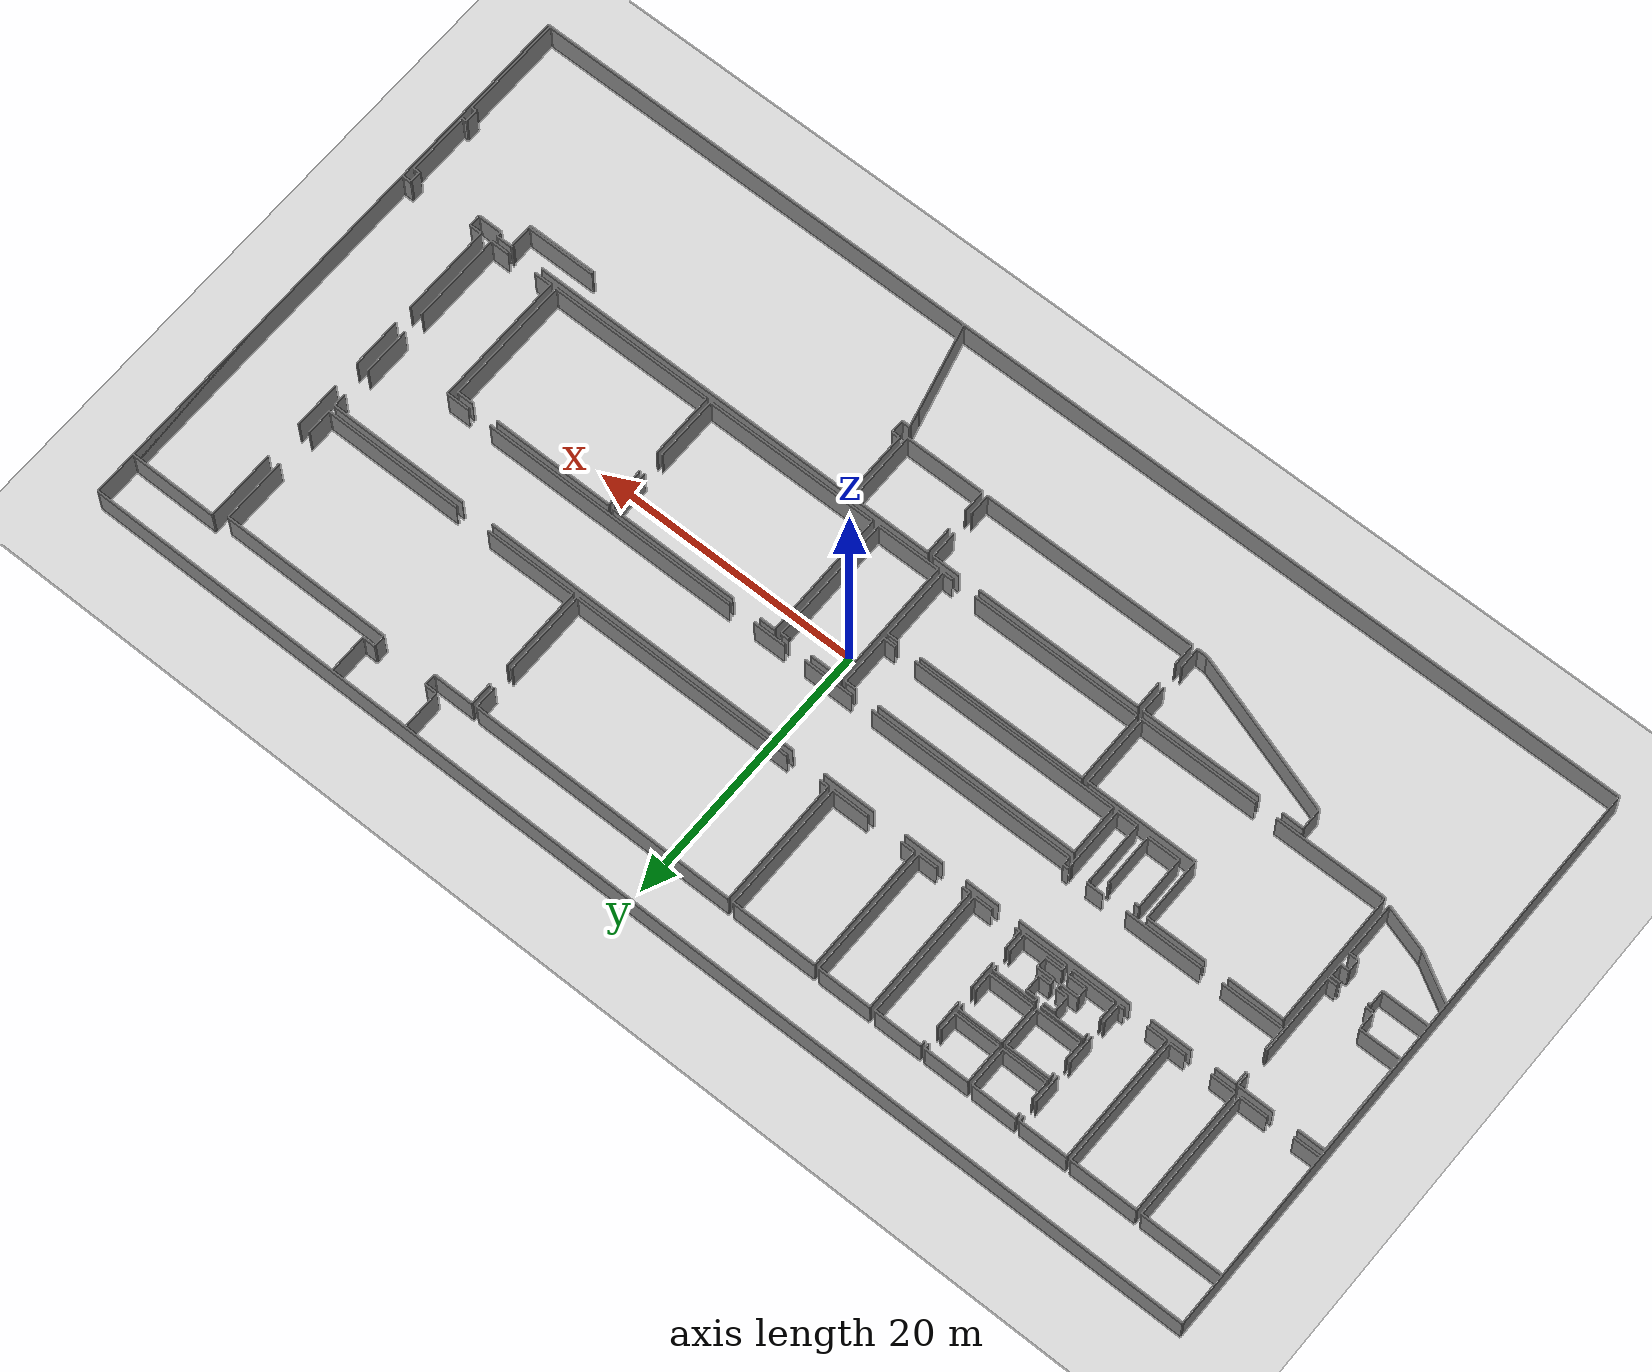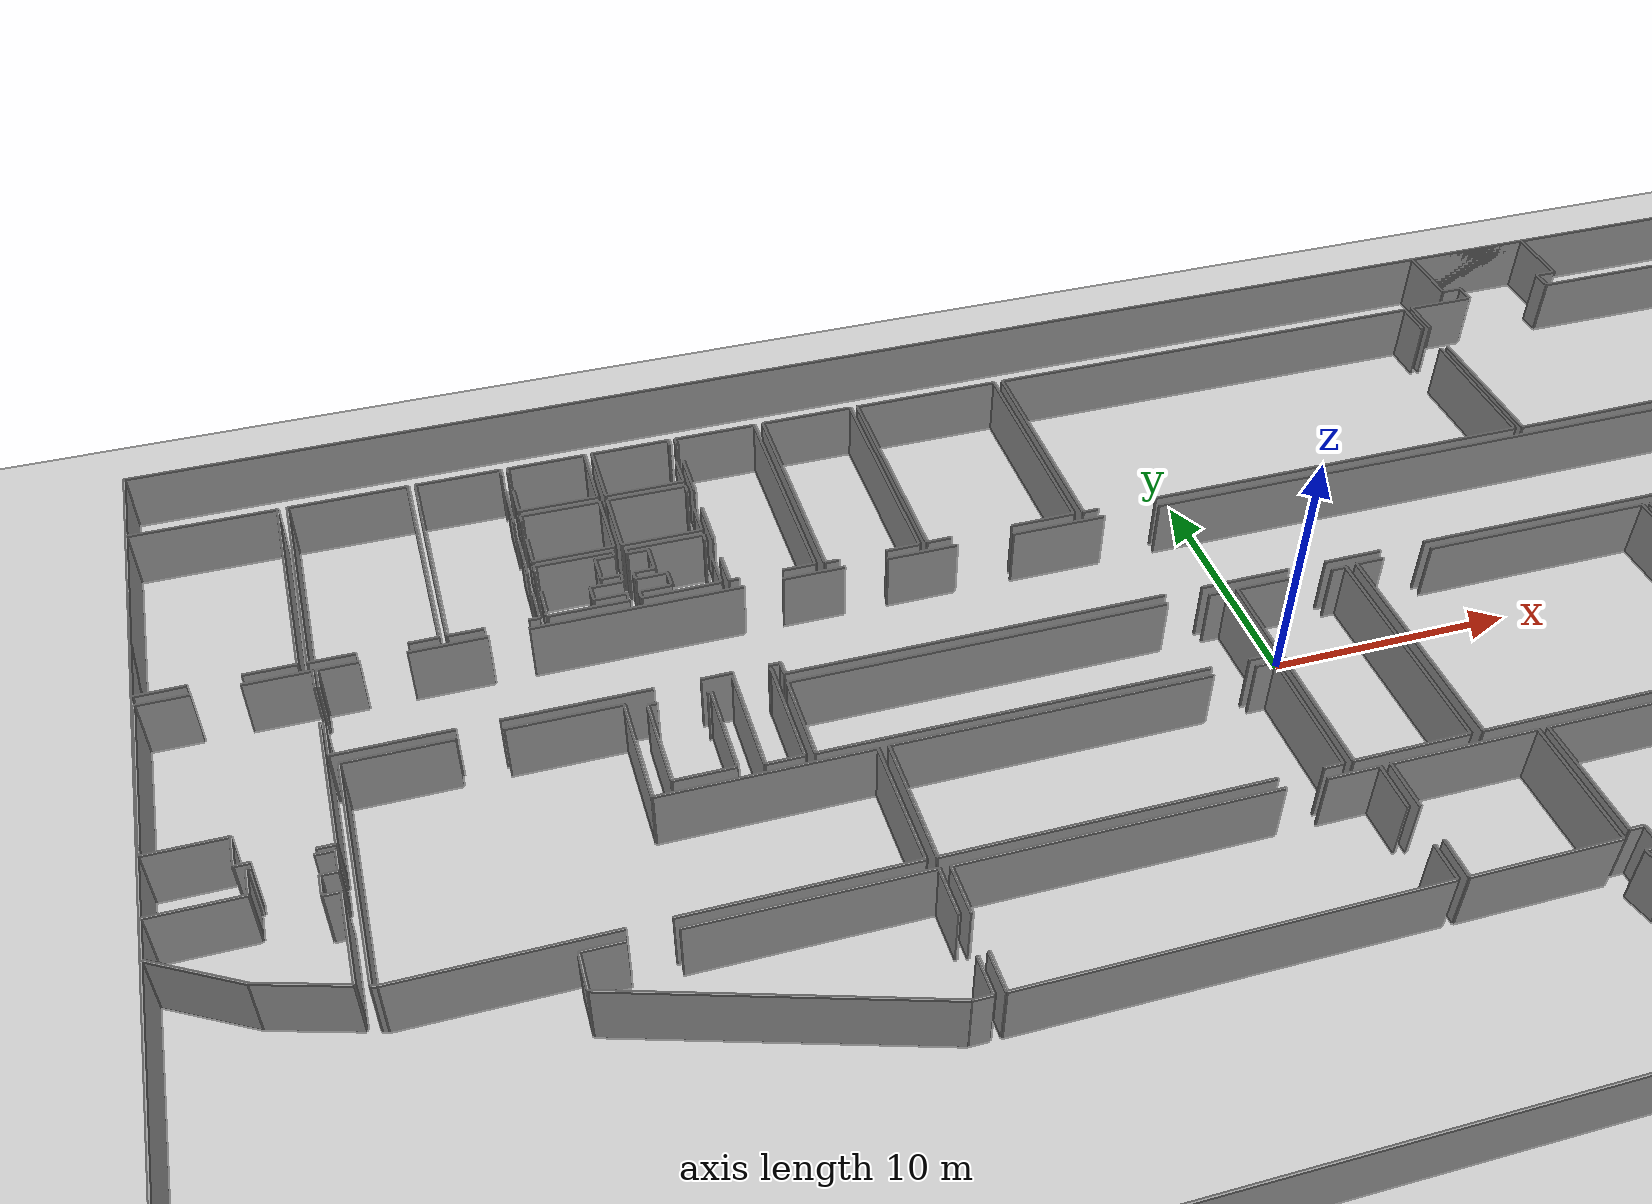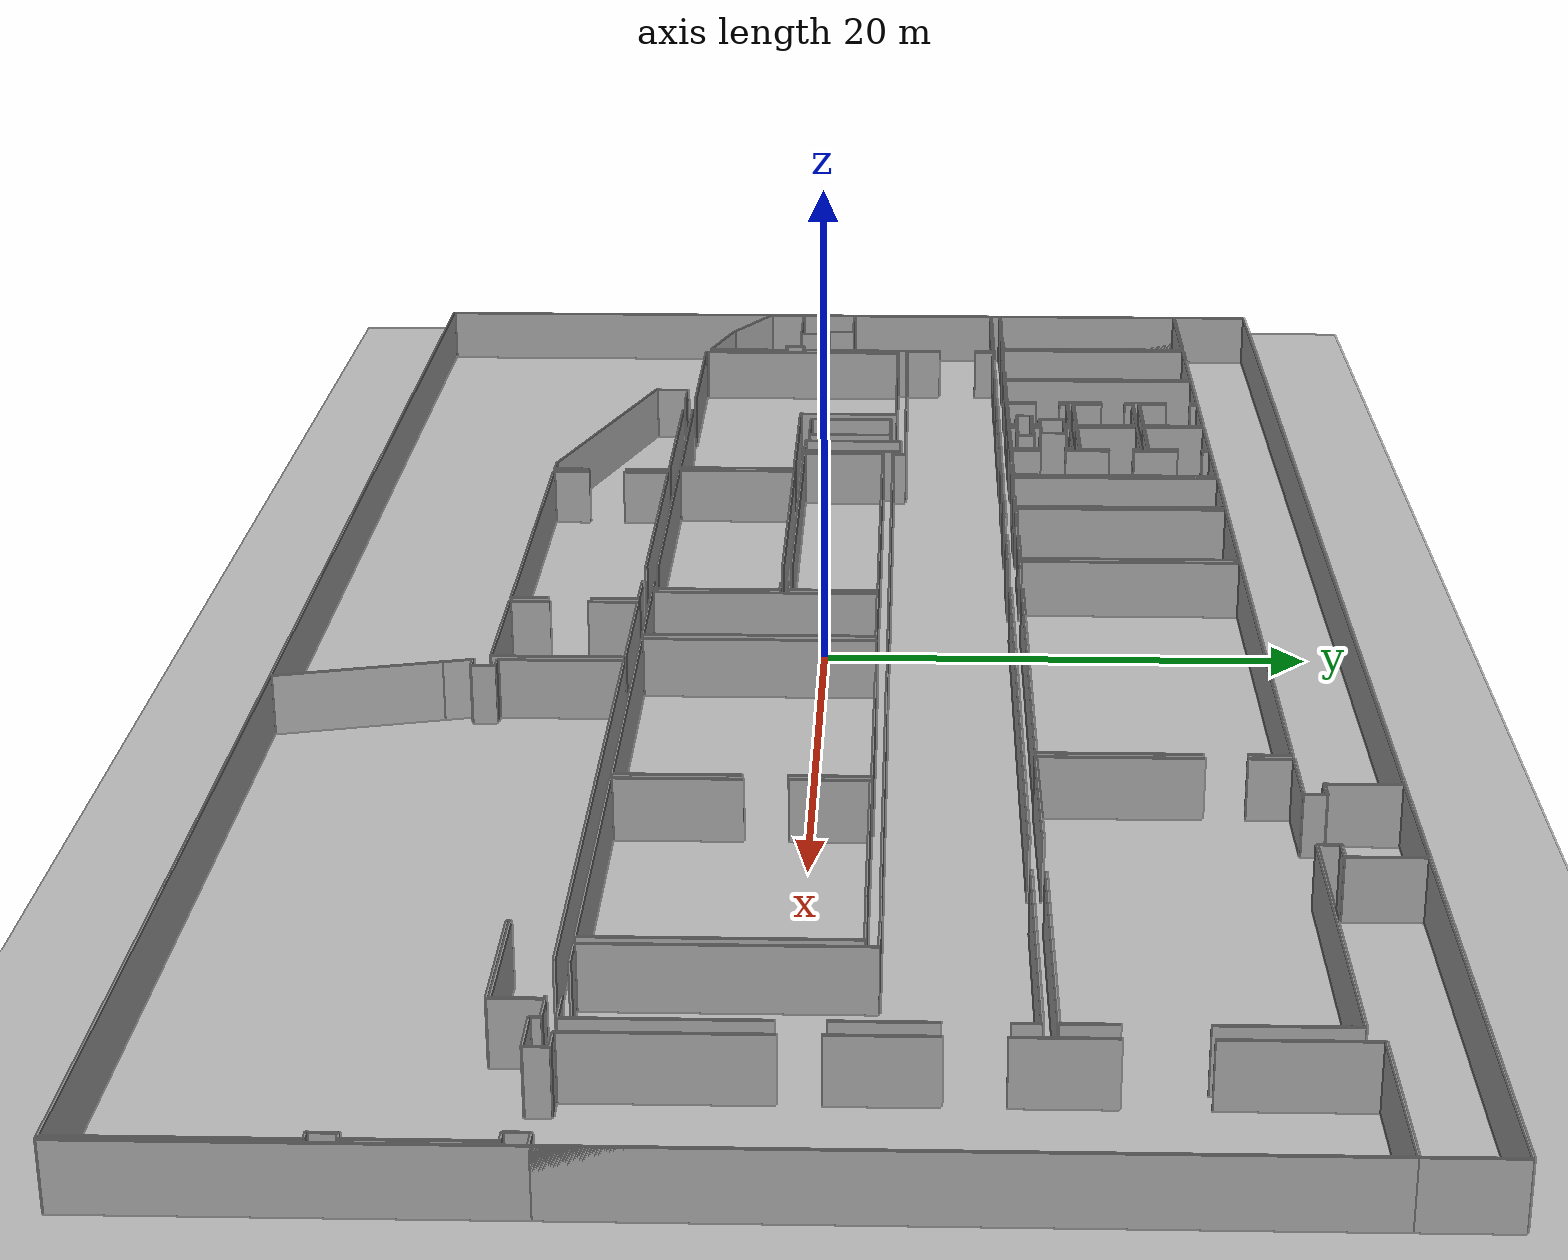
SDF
<sdf version="1.6">
  <world name="default">
    <light name="sun" type="directional">
      <cast_shadows>1</cast_shadows>
      <pose frame="">0 0 10 0 -0 0</pose>
      <diffuse>0.8 0.8 0.8 1</diffuse>
      <specular>0.1 0.1 0.1 1</specular>
      <attenuation>
        <range>1000</range>
        <constant>0.9</constant>
        <linear>0.01</linear>
        <quadratic>0.001</quadratic>
      </attenuation>
      <direction>-0.5 0.5 -1</direction>
    </light>
    <model name="ground_plane">
      <static>1</static>
      <link name="link">
        <collision name="collision">
          <geometry>
            <plane>
              <normal>0 0 1</normal>
              <size>100 100</size>
            </plane>
          </geometry>
          <surface>
            <friction>
              <ode>
                <mu>100</mu>
                <mu2>50</mu2>
              </ode>
              <torsional>
                <ode />
              </torsional>
            </friction>
            <contact>
              <ode />
            </contact>
            <bounce />
          </surface>
          <max_contacts>10</max_contacts>
        </collision>
        <visual name="visual">
          <cast_shadows>0</cast_shadows>
          <geometry>
            <plane>
              <normal>0 0 1</normal>
              <size>100 100</size>
            </plane>
          </geometry>
          <material>
            <script>
              <uri>file://media/materials/scripts/gazebo.material</uri>
              <name>Gazebo/Grey</name>
            </script>
          </material>
        </visual>
        <self_collide>0</self_collide>
        <kinematic>0</kinematic>
        <gravity>1</gravity>
      </link>
    </model>
    <gravity>0 0 -9.8</gravity>
    <magnetic_field>6e-06 2.3e-05 -4.2e-05</magnetic_field>
    <atmosphere type="adiabatic" />
    <physics default="0" name="default_physics" type="ode">
      <max_step_size>0.001</max_step_size>
      <real_time_factor>1</real_time_factor>
      <real_time_update_rate>1000</real_time_update_rate>
    </physics>
    <scene>
      <ambient>0.4 0.4 0.4 1</ambient>
      <background>0.7 0.7 0.7 1</background>
      <shadows>1</shadows>
    </scene>
    <spherical_coordinates>
      <surface_model>EARTH_WGS84</surface_model>
      <latitude_deg>0</latitude_deg>
      <longitude_deg>0</longitude_deg>
      <elevation>0</elevation>
      <heading_deg>0</heading_deg>
    </spherical_coordinates>
  <model name="50052748">
		<static>1</static>
		<link name="Wall_0">
			<collision name="Wall_0_Collision">
				<geometry>
					<box>
						<size>0.575394132933 0.1 2.5</size>
					</box>
				</geometry>
				<pose frame="">0.287697066466 0 1.25 0 0 0</pose>
			</collision>
			<visual name="Wall_0_Visual">
				<pose frame="">0.287697066466 0 1.25 0 0 0</pose>
				<geometry>
					<box>
						<size>0.575394132933 0.1 2.5</size>
					</box>
				</geometry>
				<material>
					<script>
						<uri>file://media/materials/scripts/gazebo.material</uri>
						<name>Gazebo/Grey</name>
					</script>
					<ambient>1 1 1 1</ambient>
				</material>
			</visual>
			<pose frame="">3.08483290488 -22.4780374964 0 0 0 0.0</pose>
		</link>
		<link name="Wall_1">
			<collision name="Wall_1_Collision">
				<geometry>
					<box>
						<size>0.697524296039 0.1 2.5</size>
					</box>
				</geometry>
				<pose frame="">0.34876214802 0 1.25 0 0 0</pose>
			</collision>
			<visual name="Wall_1_Visual">
				<pose frame="">0.34876214802 0 1.25 0 0 0</pose>
				<geometry>
					<box>
						<size>0.697524296039 0.1 2.5</size>
					</box>
				</geometry>
				<material>
					<script>
						<uri>file://media/materials/scripts/gazebo.material</uri>
						<name>Gazebo/Grey</name>
					</script>
					<ambient>1 1 1 1</ambient>
				</material>
			</visual>
			<pose frame="">5.80872869222 -22.4780374964 0 0 0 0.0</pose>
		</link>
		<link name="Wall_2">
			<collision name="Wall_2_Collision">
				<geometry>
					<box>
						<size>5.95381374579 0.1 2.5</size>
					</box>
				</geometry>
				<pose frame="">2.9769068729 0 1.25 0 0 0</pose>
			</collision>
			<visual name="Wall_2_Visual">
				<pose frame="">2.9769068729 0 1.25 0 0 0</pose>
				<geometry>
					<box>
						<size>5.95381374579 0.1 2.5</size>
					</box>
				</geometry>
				<material>
					<script>
						<uri>file://media/materials/scripts/gazebo.material</uri>
						<name>Gazebo/Grey</name>
					</script>
					<ambient>1 1 1 1</ambient>
				</material>
			</visual>
			<pose frame="">6.50625298826 -22.4780374964 0 0 0 1.57079632679</pose>
		</link>
		<link name="Wall_3">
			<collision name="Wall_3_Collision">
				<geometry>
					<box>
						<size>0.959032495755 0.1 2.5</size>
					</box>
				</geometry>
				<pose frame="">0.479516247877 0 1.25 0 0 0</pose>
			</collision>
			<visual name="Wall_3_Visual">
				<pose frame="">0.479516247877 0 1.25 0 0 0</pose>
				<geometry>
					<box>
						<size>0.959032495755 0.1 2.5</size>
					</box>
				</geometry>
				<material>
					<script>
						<uri>file://media/materials/scripts/gazebo.material</uri>
						<name>Gazebo/Grey</name>
					</script>
					<ambient>1 1 1 1</ambient>
				</material>
			</visual>
			<pose frame="">6.50625298826 -14.6813645604 0 0 0 1.57079632679</pose>
		</link>
		<link name="Wall_4">
			<collision name="Wall_4_Collision">
				<geometry>
					<box>
						<size>2.63385174184 0.1 2.5</size>
					</box>
				</geometry>
				<pose frame="">1.31692587092 0 1.25 0 0 0</pose>
			</collision>
			<visual name="Wall_4_Visual">
				<pose frame="">1.31692587092 0 1.25 0 0 0</pose>
				<geometry>
					<box>
						<size>2.63385174184 0.1 2.5</size>
					</box>
				</geometry>
				<material>
					<script>
						<uri>file://media/materials/scripts/gazebo.material</uri>
						<name>Gazebo/Grey</name>
					</script>
					<ambient>1 1 1 1</ambient>
				</material>
			</visual>
			<pose frame="">6.50625298826 -13.7223320647 0 0 0 3.14159265359</pose>
		</link>
		<link name="Wall_5">
			<collision name="Wall_5_Collision">
				<geometry>
					<box>
						<size>2.01800119974 0.1 2.5</size>
					</box>
				</geometry>
				<pose frame="">1.00900059987 0 1.25 0 0 0</pose>
			</collision>
			<visual name="Wall_5_Visual">
				<pose frame="">1.00900059987 0 1.25 0 0 0</pose>
				<geometry>
					<box>
						<size>2.01800119974 0.1 2.5</size>
					</box>
				</geometry>
				<material>
					<script>
						<uri>file://media/materials/scripts/gazebo.material</uri>
						<name>Gazebo/Grey</name>
					</script>
					<ambient>1 1 1 1</ambient>
				</material>
			</visual>
			<pose frame="">2.07418361122 -13.7223320647 0 0 0 3.14159265359</pose>
		</link>
		<link name="Wall_6">
			<collision name="Wall_6_Collision">
				<geometry>
					<box>
						<size>7.40364970076 0.1 2.5</size>
					</box>
				</geometry>
				<pose frame="">3.70182485038 0 1.25 0 0 0</pose>
			</collision>
			<visual name="Wall_6_Visual">
				<pose frame="">3.70182485038 0 1.25 0 0 0</pose>
				<geometry>
					<box>
						<size>7.40364970076 0.1 2.5</size>
					</box>
				</geometry>
				<material>
					<script>
						<uri>file://media/materials/scripts/gazebo.material</uri>
						<name>Gazebo/Grey</name>
					</script>
					<ambient>1 1 1 1</ambient>
				</material>
			</visual>
			<pose frame="">0.056182411481 -13.7223320647 0 0 0 -1.57079632679</pose>
		</link>
		<link name="Wall_7">
			<collision name="Wall_7_Collision">
				<geometry>
					<box>
						<size>3.0286504934 0.1 2.5</size>
					</box>
				</geometry>
				<pose frame="">1.5143252467 0 1.25 0 0 0</pose>
			</collision>
			<visual name="Wall_7_Visual">
				<pose frame="">1.5143252467 0 1.25 0 0 0</pose>
				<geometry>
					<box>
						<size>3.0286504934 0.1 2.5</size>
					</box>
				</geometry>
				<material>
					<script>
						<uri>file://media/materials/scripts/gazebo.material</uri>
						<name>Gazebo/Grey</name>
					</script>
					<ambient>1 1 1 1</ambient>
				</material>
			</visual>
			<pose frame="">0.056182411481 -21.1259817654 0 0 0 0.0</pose>
		</link>
		<link name="Wall_8">
			<collision name="Wall_8_Collision">
				<geometry>
					<box>
						<size>1.35205573092 0.1 2.5</size>
					</box>
				</geometry>
				<pose frame="">0.676027865462 0 1.25 0 0 0</pose>
			</collision>
			<visual name="Wall_8_Visual">
				<pose frame="">0.676027865462 0 1.25 0 0 0</pose>
				<geometry>
					<box>
						<size>1.35205573092 0.1 2.5</size>
					</box>
				</geometry>
				<material>
					<script>
						<uri>file://media/materials/scripts/gazebo.material</uri>
						<name>Gazebo/Grey</name>
					</script>
					<ambient>1 1 1 1</ambient>
				</material>
			</visual>
			<pose frame="">3.08483290488 -21.1259817654 0 0 0 -1.57079632679</pose>
		</link>
		<link name="Wall_9">
			<collision name="Wall_9_Collision">
				<geometry>
					<box>
						<size>1.70221292753 0.1 2.5</size>
					</box>
				</geometry>
				<pose frame="">0.851106463767 0 1.25 0 0 0</pose>
			</collision>
			<visual name="Wall_9_Visual">
				<pose frame="">0.851106463767 0 1.25 0 0 0</pose>
				<geometry>
					<box>
						<size>1.70221292753 0.1 2.5</size>
					</box>
				</geometry>
				<material>
					<script>
						<uri>file://media/materials/scripts/gazebo.material</uri>
						<name>Gazebo/Grey</name>
					</script>
					<ambient>1 1 1 1</ambient>
				</material>
			</visual>
			<pose frame="">6.65463542941 -18.2443186646 0 0 0 1.57079632679</pose>
		</link>
		<link name="Wall_10">
			<collision name="Wall_10_Collision">
				<geometry>
					<box>
						<size>0.964359044924 0.1 2.5</size>
					</box>
				</geometry>
				<pose frame="">0.482179522462 0 1.25 0 0 0</pose>
			</collision>
			<visual name="Wall_10_Visual">
				<pose frame="">0.482179522462 0 1.25 0 0 0</pose>
				<geometry>
					<box>
						<size>0.964359044924 0.1 2.5</size>
					</box>
				</geometry>
				<material>
					<script>
						<uri>file://media/materials/scripts/gazebo.material</uri>
						<name>Gazebo/Grey</name>
					</script>
					<ambient>1 1 1 1</ambient>
				</material>
			</visual>
			<pose frame="">6.65463542941 -14.692905417 0 0 0 1.57079632679</pose>
		</link>
		<link name="Wall_11">
			<collision name="Wall_11_Collision">
				<geometry>
					<box>
						<size>1.5681614401 0.1 2.5</size>
					</box>
				</geometry>
				<pose frame="">0.784080720048 0 1.25 0 0 0</pose>
			</collision>
			<visual name="Wall_11_Visual">
				<pose frame="">0.784080720048 0 1.25 0 0 0</pose>
				<geometry>
					<box>
						<size>1.5681614401 0.1 2.5</size>
					</box>
				</geometry>
				<material>
					<script>
						<uri>file://media/materials/scripts/gazebo.material</uri>
						<name>Gazebo/Grey</name>
					</script>
					<ambient>1 1 1 1</ambient>
				</material>
			</visual>
			<pose frame="">6.65463542941 -13.728546372 0 0 0 0.0</pose>
		</link>
		<link name="Wall_12">
			<collision name="Wall_12_Collision">
				<geometry>
					<box>
						<size>3.06872643478 0.1 2.5</size>
					</box>
				</geometry>
				<pose frame="">1.53436321739 0 1.25 0 0 0</pose>
			</collision>
			<visual name="Wall_12_Visual">
				<pose frame="">1.53436321739 0 1.25 0 0 0</pose>
				<geometry>
					<box>
						<size>3.06872643478 0.1 2.5</size>
					</box>
				</geometry>
				<material>
					<script>
						<uri>file://media/materials/scripts/gazebo.material</uri>
						<name>Gazebo/Grey</name>
					</script>
					<ambient>1 1 1 1</ambient>
				</material>
			</visual>
			<pose frame="">9.99894737243 -13.728546372 0 0 0 0.0</pose>
		</link>
		<link name="Wall_13">
			<collision name="Wall_13_Collision">
				<geometry>
					<box>
						<size>8.453994468 0.1 2.5</size>
					</box>
				</geometry>
				<pose frame="">4.226997234 0 1.25 0 0 0</pose>
			</collision>
			<visual name="Wall_13_Visual">
				<pose frame="">4.226997234 0 1.25 0 0 0</pose>
				<geometry>
					<box>
						<size>8.453994468 0.1 2.5</size>
					</box>
				</geometry>
				<material>
					<script>
						<uri>file://media/materials/scripts/gazebo.material</uri>
						<name>Gazebo/Grey</name>
					</script>
					<ambient>1 1 1 1</ambient>
				</material>
			</visual>
			<pose frame="">14.6307623433 -13.728546372 0 0 0 0.0</pose>
		</link>
		<link name="Wall_14">
			<collision name="Wall_14_Collision">
				<geometry>
					<box>
						<size>2.53797385679 0.1 2.5</size>
					</box>
				</geometry>
				<pose frame="">1.26898692839 0 1.25 0 0 0</pose>
			</collision>
			<visual name="Wall_14_Visual">
				<pose frame="">1.26898692839 0 1.25 0 0 0</pose>
				<geometry>
					<box>
						<size>2.53797385679 0.1 2.5</size>
					</box>
				</geometry>
				<material>
					<script>
						<uri>file://media/materials/scripts/gazebo.material</uri>
						<name>Gazebo/Grey</name>
					</script>
					<ambient>1 1 1 1</ambient>
				</material>
			</visual>
			<pose frame="">24.6610348978 -13.728546372 0 0 0 0.0</pose>
		</link>
		<link name="Wall_15">
			<collision name="Wall_15_Collision">
				<geometry>
					<box>
						<size>2.93442130214 0.1 2.5</size>
					</box>
				</geometry>
				<pose frame="">1.46721065107 0 1.25 0 0 0</pose>
			</collision>
			<visual name="Wall_15_Visual">
				<pose frame="">1.46721065107 0 1.25 0 0 0</pose>
				<geometry>
					<box>
						<size>2.93442130214 0.1 2.5</size>
					</box>
				</geometry>
				<material>
					<script>
						<uri>file://media/materials/scripts/gazebo.material</uri>
						<name>Gazebo/Grey</name>
					</script>
					<ambient>1 1 1 1</ambient>
				</material>
			</visual>
			<pose frame="">28.9768079513 -13.728546372 0 0 0 0.0</pose>
		</link>
		<link name="Wall_16">
			<collision name="Wall_16_Collision">
				<geometry>
					<box>
						<size>3.93695394945 0.1 2.5</size>
					</box>
				</geometry>
				<pose frame="">1.96847697472 0 1.25 0 0 0</pose>
			</collision>
			<visual name="Wall_16_Visual">
				<pose frame="">1.96847697472 0 1.25 0 0 0</pose>
				<geometry>
					<box>
						<size>3.93695394945 0.1 2.5</size>
					</box>
				</geometry>
				<material>
					<script>
						<uri>file://media/materials/scripts/gazebo.material</uri>
						<name>Gazebo/Grey</name>
					</script>
					<ambient>1 1 1 1</ambient>
				</material>
			</visual>
			<pose frame="">34.3019620724 -13.728546372 0 0 0 0.0</pose>
		</link>
		<link name="Wall_17">
			<collision name="Wall_17_Collision">
				<geometry>
					<box>
						<size>24.0978157344 0.1 2.5</size>
					</box>
				</geometry>
				<pose frame="">12.0489078672 0 1.25 0 0 0</pose>
			</collision>
			<visual name="Wall_17_Visual">
				<pose frame="">12.0489078672 0 1.25 0 0 0</pose>
				<geometry>
					<box>
						<size>24.0978157344 0.1 2.5</size>
					</box>
				</geometry>
				<material>
					<script>
						<uri>file://media/materials/scripts/gazebo.material</uri>
						<name>Gazebo/Grey</name>
					</script>
					<ambient>1 1 1 1</ambient>
				</material>
			</visual>
			<pose frame="">40.6578034579 -13.728546372 0 0 0 0.0</pose>
		</link>
		<link name="Wall_18">
			<collision name="Wall_18_Collision">
				<geometry>
					<box>
						<size>10.5498647437 0.1 2.5</size>
					</box>
				</geometry>
				<pose frame="">5.27493237185 0 1.25 0 0 0</pose>
			</collision>
			<visual name="Wall_18_Visual">
				<pose frame="">5.27493237185 0 1.25 0 0 0</pose>
				<geometry>
					<box>
						<size>10.5498647437 0.1 2.5</size>
					</box>
				</geometry>
				<material>
					<script>
						<uri>file://media/materials/scripts/gazebo.material</uri>
						<name>Gazebo/Grey</name>
					</script>
					<ambient>1 1 1 1</ambient>
				</material>
			</visual>
			<pose frame="">67.1843987911 -13.728546372 0 0 0 0.0</pose>
		</link>
		<link name="Wall_19">
			<collision name="Wall_19_Collision">
				<geometry>
					<box>
						<size>0.96689549691 0.1 2.5</size>
					</box>
				</geometry>
				<pose frame="">0.483447748455 0 1.25 0 0 0</pose>
			</collision>
			<visual name="Wall_19_Visual">
				<pose frame="">0.483447748455 0 1.25 0 0 0</pose>
				<geometry>
					<box>
						<size>0.96689549691 0.1 2.5</size>
					</box>
				</geometry>
				<material>
					<script>
						<uri>file://media/materials/scripts/gazebo.material</uri>
						<name>Gazebo/Grey</name>
					</script>
					<ambient>1 1 1 1</ambient>
				</material>
			</visual>
			<pose frame="">77.7342635348 -13.728546372 0 0 0 -1.57079632679</pose>
		</link>
		<link name="Wall_20">
			<collision name="Wall_20_Collision">
				<geometry>
					<box>
						<size>3.53581406792 0.1 2.5</size>
					</box>
				</geometry>
				<pose frame="">1.76790703396 0 1.25 0 0 0</pose>
			</collision>
			<visual name="Wall_20_Visual">
				<pose frame="">1.76790703396 0 1.25 0 0 0</pose>
				<geometry>
					<box>
						<size>3.53581406792 0.1 2.5</size>
					</box>
				</geometry>
				<material>
					<script>
						<uri>file://media/materials/scripts/gazebo.material</uri>
						<name>Gazebo/Grey</name>
					</script>
					<ambient>1 1 1 1</ambient>
				</material>
			</visual>
			<pose frame="">77.7342635348 -16.8539625087 0 0 0 -1.57079632679</pose>
		</link>
		<link name="Wall_21">
			<collision name="Wall_21_Collision">
				<geometry>
					<box>
						<size>6.75850313823 0.1 2.5</size>
					</box>
				</geometry>
				<pose frame="">3.37925156911 0 1.25 0 0 0</pose>
			</collision>
			<visual name="Wall_21_Visual">
				<pose frame="">3.37925156911 0 1.25 0 0 0</pose>
				<geometry>
					<box>
						<size>6.75850313823 0.1 2.5</size>
					</box>
				</geometry>
				<material>
					<script>
						<uri>file://media/materials/scripts/gazebo.material</uri>
						<name>Gazebo/Grey</name>
					</script>
					<ambient>1 1 1 1</ambient>
				</material>
			</visual>
			<pose frame="">77.7342635348 -22.0008040553 0 0 0 -1.57079632679</pose>
		</link>
		<link name="Wall_22">
			<collision name="Wall_22_Collision">
				<geometry>
					<box>
						<size>1.40392617403 0.1 2.5</size>
					</box>
				</geometry>
				<pose frame="">0.701963087014 0 1.25 0 0 0</pose>
			</collision>
			<visual name="Wall_22_Visual">
				<pose frame="">0.701963087014 0 1.25 0 0 0</pose>
				<geometry>
					<box>
						<size>1.40392617403 0.1 2.5</size>
					</box>
				</geometry>
				<material>
					<script>
						<uri>file://media/materials/scripts/gazebo.material</uri>
						<name>Gazebo/Grey</name>
					</script>
					<ambient>1 1 1 1</ambient>
				</material>
			</visual>
			<pose frame="">77.7342635348 -28.7593071935 0 0 0 3.14159265359</pose>
		</link>
		<link name="Wall_23">
			<collision name="Wall_23_Collision">
				<geometry>
					<box>
						<size>1.29460509345 0.1 2.5</size>
					</box>
				</geometry>
				<pose frame="">0.647302546725 0 1.25 0 0 0</pose>
			</collision>
			<visual name="Wall_23_Visual">
				<pose frame="">0.647302546725 0 1.25 0 0 0</pose>
				<geometry>
					<box>
						<size>1.29460509345 0.1 2.5</size>
					</box>
				</geometry>
				<material>
					<script>
						<uri>file://media/materials/scripts/gazebo.material</uri>
						<name>Gazebo/Grey</name>
					</script>
					<ambient>1 1 1 1</ambient>
				</material>
			</visual>
			<pose frame="">74.1246387141 -28.7593071935 0 0 0 3.14159265359</pose>
		</link>
		<link name="Wall_24">
			<collision name="Wall_24_Collision">
				<geometry>
					<box>
						<size>9.9336337338 0.1 2.5</size>
					</box>
				</geometry>
				<pose frame="">4.9668168669 0 1.25 0 0 0</pose>
			</collision>
			<visual name="Wall_24_Visual">
				<pose frame="">4.9668168669 0 1.25 0 0 0</pose>
				<geometry>
					<box>
						<size>9.9336337338 0.1 2.5</size>
					</box>
				</geometry>
				<material>
					<script>
						<uri>file://media/materials/scripts/gazebo.material</uri>
						<name>Gazebo/Grey</name>
					</script>
					<ambient>1 1 1 1</ambient>
				</material>
			</visual>
			<pose frame="">72.8300336207 -28.7593071935 0 0 0 1.57079632679</pose>
		</link>
		<link name="Wall_25">
			<collision name="Wall_25_Collision">
				<geometry>
					<box>
						<size>1.73569409374 0.1 2.5</size>
					</box>
				</geometry>
				<pose frame="">0.867847046872 0 1.25 0 0 0</pose>
			</collision>
			<visual name="Wall_25_Visual">
				<pose frame="">0.867847046872 0 1.25 0 0 0</pose>
				<geometry>
					<box>
						<size>1.73569409374 0.1 2.5</size>
					</box>
				</geometry>
				<material>
					<script>
						<uri>file://media/materials/scripts/gazebo.material</uri>
						<name>Gazebo/Grey</name>
					</script>
					<ambient>1 1 1 1</ambient>
				</material>
			</visual>
			<pose frame="">72.8300336207 -18.8256734597 0 0 0 3.14159265359</pose>
		</link>
		<link name="Wall_26">
			<collision name="Wall_26_Collision">
				<geometry>
					<box>
						<size>19.3869902841 0.1 2.5</size>
					</box>
				</geometry>
				<pose frame="">9.69349514206 0 1.25 0 0 0</pose>
			</collision>
			<visual name="Wall_26_Visual">
				<pose frame="">9.69349514206 0 1.25 0 0 0</pose>
				<geometry>
					<box>
						<size>19.3869902841 0.1 2.5</size>
					</box>
				</geometry>
				<material>
					<script>
						<uri>file://media/materials/scripts/gazebo.material</uri>
						<name>Gazebo/Grey</name>
					</script>
					<ambient>1 1 1 1</ambient>
				</material>
			</visual>
			<pose frame="">69.3134965878 -18.8256734597 0 0 0 3.14159265359</pose>
		</link>
		<link name="Wall_27">
			<collision name="Wall_27_Collision">
				<geometry>
					<box>
						<size>2.42193117845 0.1 2.5</size>
					</box>
				</geometry>
				<pose frame="">1.21096558922 0 1.25 0 0 0</pose>
			</collision>
			<visual name="Wall_27_Visual">
				<pose frame="">1.21096558922 0 1.25 0 0 0</pose>
				<geometry>
					<box>
						<size>2.42193117845 0.1 2.5</size>
					</box>
				</geometry>
				<material>
					<script>
						<uri>file://media/materials/scripts/gazebo.material</uri>
						<name>Gazebo/Grey</name>
					</script>
					<ambient>1 1 1 1</ambient>
				</material>
			</visual>
			<pose frame="">47.9662093866 -18.8256734597 0 0 0 3.14159265359</pose>
		</link>
		<link name="Wall_28">
			<collision name="Wall_28_Collision">
				<geometry>
					<box>
						<size>3.72313104706 0.1 2.5</size>
					</box>
				</geometry>
				<pose frame="">1.86156552353 0 1.25 0 0 0</pose>
			</collision>
			<visual name="Wall_28_Visual">
				<pose frame="">1.86156552353 0 1.25 0 0 0</pose>
				<geometry>
					<box>
						<size>3.72313104706 0.1 2.5</size>
					</box>
				</geometry>
				<material>
					<script>
						<uri>file://media/materials/scripts/gazebo.material</uri>
						<name>Gazebo/Grey</name>
					</script>
					<ambient>1 1 1 1</ambient>
				</material>
			</visual>
			<pose frame="">43.9417478437 -18.8256734597 0 0 0 3.14159265359</pose>
		</link>
		<link name="Wall_29">
			<collision name="Wall_29_Collision">
				<geometry>
					<box>
						<size>15.3426175931 0.1 2.5</size>
					</box>
				</geometry>
				<pose frame="">7.67130879654 0 1.25 0 0 0</pose>
			</collision>
			<visual name="Wall_29_Visual">
				<pose frame="">7.67130879654 0 1.25 0 0 0</pose>
				<geometry>
					<box>
						<size>15.3426175931 0.1 2.5</size>
					</box>
				</geometry>
				<material>
					<script>
						<uri>file://media/materials/scripts/gazebo.material</uri>
						<name>Gazebo/Grey</name>
					</script>
					<ambient>1 1 1 1</ambient>
				</material>
			</visual>
			<pose frame="">38.6622498583 -18.8256734597 0 0 0 3.14159265359</pose>
		</link>
		<link name="Wall_30">
			<collision name="Wall_30_Collision">
				<geometry>
					<box>
						<size>0.586934989467 0.1 2.5</size>
					</box>
				</geometry>
				<pose frame="">0.293467494734 0 1.25 0 0 0</pose>
			</collision>
			<visual name="Wall_30_Visual">
				<pose frame="">0.293467494734 0 1.25 0 0 0</pose>
				<geometry>
					<box>
						<size>0.586934989467 0.1 2.5</size>
					</box>
				</geometry>
				<material>
					<script>
						<uri>file://media/materials/scripts/gazebo.material</uri>
						<name>Gazebo/Grey</name>
					</script>
					<ambient>1 1 1 1</ambient>
				</material>
			</visual>
			<pose frame="">23.3196322652 -18.8256734597 0 0 0 1.57079632679</pose>
		</link>
		<link name="Wall_31">
			<collision name="Wall_31_Collision">
				<geometry>
					<box>
						<size>0.456815002606 0.1 2.5</size>
					</box>
				</geometry>
				<pose frame="">0.228407501303 0 1.25 0 0 0</pose>
			</collision>
			<visual name="Wall_31_Visual">
				<pose frame="">0.228407501303 0 1.25 0 0 0</pose>
				<geometry>
					<box>
						<size>0.456815002606 0.1 2.5</size>
					</box>
				</geometry>
				<material>
					<script>
						<uri>file://media/materials/scripts/gazebo.material</uri>
						<name>Gazebo/Grey</name>
					</script>
					<ambient>1 1 1 1</ambient>
				</material>
			</visual>
			<pose frame="">23.3196322652 -18.2387384702 0 0 0 3.14159265359</pose>
		</link>
		<link name="Wall_32">
			<collision name="Wall_32_Collision">
				<geometry>
					<box>
						<size>1.24666615092 0.1 2.5</size>
					</box>
				</geometry>
				<pose frame="">0.623333075461 0 1.25 0 0 0</pose>
			</collision>
			<visual name="Wall_32_Visual">
				<pose frame="">0.623333075461 0 1.25 0 0 0</pose>
				<geometry>
					<box>
						<size>1.24666615092 0.1 2.5</size>
					</box>
				</geometry>
				<material>
					<script>
						<uri>file://media/materials/scripts/gazebo.material</uri>
						<name>Gazebo/Grey</name>
					</script>
					<ambient>1 1 1 1</ambient>
				</material>
			</visual>
			<pose frame="">21.4969378683 -18.2387384702 0 0 0 3.14159265359</pose>
		</link>
		<link name="Wall_33">
			<collision name="Wall_33_Collision">
				<geometry>
					<box>
						<size>5.7065096772 0.1 2.5</size>
					</box>
				</geometry>
				<pose frame="">2.8532548386 0 1.25 0 0 0</pose>
			</collision>
			<visual name="Wall_33_Visual">
				<pose frame="">2.8532548386 0 1.25 0 0 0</pose>
				<geometry>
					<box>
						<size>5.7065096772 0.1 2.5</size>
					</box>
				</geometry>
				<material>
					<script>
						<uri>file://media/materials/scripts/gazebo.material</uri>
						<name>Gazebo/Grey</name>
					</script>
					<ambient>1 1 1 1</ambient>
				</material>
			</visual>
			<pose frame="">18.4755162631 -18.2387384702 0 0 0 3.14159265359</pose>
		</link>
		<link name="Wall_34">
			<collision name="Wall_34_Collision">
				<geometry>
					<box>
						<size>4.52972621562 0.1 2.5</size>
					</box>
				</geometry>
				<pose frame="">2.26486310781 0 1.25 0 0 0</pose>
			</collision>
			<visual name="Wall_34_Visual">
				<pose frame="">2.26486310781 0 1.25 0 0 0</pose>
				<geometry>
					<box>
						<size>4.52972621562 0.1 2.5</size>
					</box>
				</geometry>
				<material>
					<script>
						<uri>file://media/materials/scripts/gazebo.material</uri>
						<name>Gazebo/Grey</name>
					</script>
					<ambient>1 1 1 1</ambient>
				</material>
			</visual>
			<pose frame="">11.1843582079 -18.2387384702 0 0 0 -3.14036074784</pose>
		</link>
		<link name="Wall_35">
			<collision name="Wall_35_Collision">
				<geometry>
					<box>
						<size>9.44384485538 0.1 2.5</size>
					</box>
				</geometry>
				<pose frame="">4.72192242769 0 1.25 0 0 0</pose>
			</collision>
			<visual name="Wall_35_Visual">
				<pose frame="">4.72192242769 0 1.25 0 0 0</pose>
				<geometry>
					<box>
						<size>9.44384485538 0.1 2.5</size>
					</box>
				</geometry>
				<material>
					<script>
						<uri>file://media/materials/scripts/gazebo.material</uri>
						<name>Gazebo/Grey</name>
					</script>
					<ambient>1 1 1 1</ambient>
				</material>
			</visual>
			<pose frame="">0.0 -13.235460106 0 0 0 1.57079632679</pose>
		</link>
		<link name="Wall_36">
			<collision name="Wall_36_Collision">
				<geometry>
					<box>
						<size>5.98133424984 0.1 2.5</size>
					</box>
				</geometry>
				<pose frame="">2.99066712492 0 1.25 0 0 0</pose>
			</collision>
			<visual name="Wall_36_Visual">
				<pose frame="">2.99066712492 0 1.25 0 0 0</pose>
				<geometry>
					<box>
						<size>5.98133424984 0.1 2.5</size>
					</box>
				</geometry>
				<material>
					<script>
						<uri>file://media/materials/scripts/gazebo.material</uri>
						<name>Gazebo/Grey</name>
					</script>
					<ambient>1 1 1 1</ambient>
				</material>
			</visual>
			<pose frame="">0.0 -3.79161525067 0 0 0 0.0</pose>
		</link>
		<link name="Wall_37">
			<collision name="Wall_37_Collision">
				<geometry>
					<box>
						<size>9.42139725531 0.1 2.5</size>
					</box>
				</geometry>
				<pose frame="">4.71069862765 0 1.25 0 0 0</pose>
			</collision>
			<visual name="Wall_37_Visual">
				<pose frame="">4.71069862765 0 1.25 0 0 0</pose>
				<geometry>
					<box>
						<size>9.42139725531 0.1 2.5</size>
					</box>
				</geometry>
				<material>
					<script>
						<uri>file://media/materials/scripts/gazebo.material</uri>
						<name>Gazebo/Grey</name>
					</script>
					<ambient>1 1 1 1</ambient>
				</material>
			</visual>
			<pose frame="">5.98133424984 -3.79161525067 0 0 0 -1.57079632679</pose>
		</link>
		<link name="Wall_38">
			<collision name="Wall_38_Collision">
				<geometry>
					<box>
						<size>2.04057562241 0.1 2.5</size>
					</box>
				</geometry>
				<pose frame="">1.02028781121 0 1.25 0 0 0</pose>
			</collision>
			<visual name="Wall_38_Visual">
				<pose frame="">1.02028781121 0 1.25 0 0 0</pose>
				<geometry>
					<box>
						<size>2.04057562241 0.1 2.5</size>
					</box>
				</geometry>
				<material>
					<script>
						<uri>file://media/materials/scripts/gazebo.material</uri>
						<name>Gazebo/Grey</name>
					</script>
					<ambient>1 1 1 1</ambient>
				</material>
			</visual>
			<pose frame="">5.98133424984 -13.213012506 0 0 0 3.14159265359</pose>
		</link>
		<link name="Wall_39">
			<collision name="Wall_39_Collision">
				<geometry>
					<box>
						<size>1.97247279987 0.1 2.5</size>
					</box>
				</geometry>
				<pose frame="">0.986236399936 0 1.25 0 0 0</pose>
			</collision>
			<visual name="Wall_39_Visual">
				<pose frame="">0.986236399936 0 1.25 0 0 0</pose>
				<geometry>
					<box>
						<size>1.97247279987 0.1 2.5</size>
					</box>
				</geometry>
				<material>
					<script>
						<uri>file://media/materials/scripts/gazebo.material</uri>
						<name>Gazebo/Grey</name>
					</script>
					<ambient>1 1 1 1</ambient>
				</material>
			</visual>
			<pose frame="">1.972345064 -13.213012506 0 0 0 -3.13021197212</pose>
		</link>
		<link name="Wall_40">
			<collision name="Wall_40_Collision">
				<geometry>
					<box>
						<size>1.74254251411 0.1 2.5</size>
					</box>
				</geometry>
				<pose frame="">0.871271257053 0 1.25 0 0 0</pose>
			</collision>
			<visual name="Wall_40_Visual">
				<pose frame="">0.871271257053 0 1.25 0 0 0</pose>
				<geometry>
					<box>
						<size>1.74254251411 0.1 2.5</size>
					</box>
				</geometry>
				<material>
					<script>
						<uri>file://media/materials/scripts/gazebo.material</uri>
						<name>Gazebo/Grey</name>
					</script>
					<ambient>1 1 1 1</ambient>
				</material>
			</visual>
			<pose frame="">0.0157260023107 -25.6220965551 0 0 0 1.57079632679</pose>
		</link>
		<link name="Wall_41">
			<collision name="Wall_41_Collision">
				<geometry>
					<box>
						<size>3.47379781688 0.1 2.5</size>
					</box>
				</geometry>
				<pose frame="">1.73689890844 0 1.25 0 0 0</pose>
			</collision>
			<visual name="Wall_41_Visual">
				<pose frame="">1.73689890844 0 1.25 0 0 0</pose>
				<geometry>
					<box>
						<size>3.47379781688 0.1 2.5</size>
					</box>
				</geometry>
				<material>
					<script>
						<uri>file://media/materials/scripts/gazebo.material</uri>
						<name>Gazebo/Grey</name>
					</script>
					<ambient>1 1 1 1</ambient>
				</material>
			</visual>
			<pose frame="">0.0157260023107 -23.879554041 0 0 0 0.0</pose>
		</link>
		<link name="Wall_42">
			<collision name="Wall_42_Collision">
				<geometry>
					<box>
						<size>1.1452080715 0.1 2.5</size>
					</box>
				</geometry>
				<pose frame="">0.572604035749 0 1.25 0 0 0</pose>
			</collision>
			<visual name="Wall_42_Visual">
				<pose frame="">0.572604035749 0 1.25 0 0 0</pose>
				<geometry>
					<box>
						<size>1.1452080715 0.1 2.5</size>
					</box>
				</geometry>
				<material>
					<script>
						<uri>file://media/materials/scripts/gazebo.material</uri>
						<name>Gazebo/Grey</name>
					</script>
					<ambient>1 1 1 1</ambient>
				</material>
			</visual>
			<pose frame="">3.48952381919 -23.879554041 0 0 0 1.57079632679</pose>
		</link>
		<link name="Wall_43">
			<collision name="Wall_43_Collision">
				<geometry>
					<box>
						<size>0.17958080058 0.1 2.5</size>
					</box>
				</geometry>
				<pose frame="">0.0897904002902 0 1.25 0 0 0</pose>
			</collision>
			<visual name="Wall_43_Visual">
				<pose frame="">0.0897904002902 0 1.25 0 0 0</pose>
				<geometry>
					<box>
						<size>0.17958080058 0.1 2.5</size>
					</box>
				</geometry>
				<material>
					<script>
						<uri>file://media/materials/scripts/gazebo.material</uri>
						<name>Gazebo/Grey</name>
					</script>
					<ambient>1 1 1 1</ambient>
				</material>
			</visual>
			<pose frame="">3.48952381919 -22.7343459695 0 0 0 0.0</pose>
		</link>
		<link name="Wall_44">
			<collision name="Wall_44_Collision">
				<geometry>
					<box>
						<size>0.732273688242 0.1 2.5</size>
					</box>
				</geometry>
				<pose frame="">0.366136844121 0 1.25 0 0 0</pose>
			</collision>
			<visual name="Wall_44_Visual">
				<pose frame="">0.366136844121 0 1.25 0 0 0</pose>
				<geometry>
					<box>
						<size>0.732273688242 0.1 2.5</size>
					</box>
				</geometry>
				<material>
					<script>
						<uri>file://media/materials/scripts/gazebo.material</uri>
						<name>Gazebo/Grey</name>
					</script>
					<ambient>1 1 1 1</ambient>
				</material>
			</visual>
			<pose frame="">5.72844998687 -22.7343459695 0 0 0 0.0</pose>
		</link>
		<link name="Wall_45">
			<collision name="Wall_45_Collision">
				<geometry>
					<box>
						<size>0.951676784996 0.1 2.5</size>
					</box>
				</geometry>
				<pose frame="">0.475838392498 0 1.25 0 0 0</pose>
			</collision>
			<visual name="Wall_45_Visual">
				<pose frame="">0.475838392498 0 1.25 0 0 0</pose>
				<geometry>
					<box>
						<size>0.951676784996 0.1 2.5</size>
					</box>
				</geometry>
				<material>
					<script>
						<uri>file://media/materials/scripts/gazebo.material</uri>
						<name>Gazebo/Grey</name>
					</script>
					<ambient>1 1 1 1</ambient>
				</material>
			</visual>
			<pose frame="">6.46072367512 -22.7343459695 0 0 0 -1.57079632679</pose>
		</link>
		<link name="Wall_46">
			<collision name="Wall_46_Collision">
				<geometry>
					<box>
						<size>0.627645043836 0.1 2.5</size>
					</box>
				</geometry>
				<pose frame="">0.313822521918 0 1.25 0 0 0</pose>
			</collision>
			<visual name="Wall_46_Visual">
				<pose frame="">0.313822521918 0 1.25 0 0 0</pose>
				<geometry>
					<box>
						<size>0.627645043836 0.1 2.5</size>
					</box>
				</geometry>
				<material>
					<script>
						<uri>file://media/materials/scripts/gazebo.material</uri>
						<name>Gazebo/Grey</name>
					</script>
					<ambient>1 1 1 1</ambient>
				</material>
			</visual>
			<pose frame="">6.46072367512 -23.6860227545 0 0 0 3.14159265359</pose>
		</link>
		<link name="Wall_47">
			<collision name="Wall_47_Collision">
				<geometry>
					<box>
						<size>0.899172228894 0.1 2.5</size>
					</box>
				</geometry>
				<pose frame="">0.449586114447 0 1.25 0 0 0</pose>
			</collision>
			<visual name="Wall_47_Visual">
				<pose frame="">0.449586114447 0 1.25 0 0 0</pose>
				<geometry>
					<box>
						<size>0.899172228894 0.1 2.5</size>
					</box>
				</geometry>
				<material>
					<script>
						<uri>file://media/materials/scripts/gazebo.material</uri>
						<name>Gazebo/Grey</name>
					</script>
					<ambient>1 1 1 1</ambient>
				</material>
			</visual>
			<pose frame="">5.83307863128 -23.6860227545 0 0 0 -1.57079632679</pose>
		</link>
		<link name="Wall_48">
			<collision name="Wall_48_Collision">
				<geometry>
					<box>
						<size>0.636015335389 0.1 2.5</size>
					</box>
				</geometry>
				<pose frame="">0.318007667694 0 1.25 0 0 0</pose>
			</collision>
			<visual name="Wall_48_Visual">
				<pose frame="">0.318007667694 0 1.25 0 0 0</pose>
				<geometry>
					<box>
						<size>0.636015335389 0.1 2.5</size>
					</box>
				</geometry>
				<material>
					<script>
						<uri>file://media/materials/scripts/gazebo.material</uri>
						<name>Gazebo/Grey</name>
					</script>
					<ambient>1 1 1 1</ambient>
				</material>
			</visual>
			<pose frame="">5.83307863128 -24.5851949834 0 0 0 0.0</pose>
		</link>
		<link name="Wall_49">
			<collision name="Wall_49_Collision">
				<geometry>
					<box>
						<size>3.94228049862 0.1 2.5</size>
					</box>
				</geometry>
				<pose frame="">1.97114024931 0 1.25 0 0 0</pose>
			</collision>
			<visual name="Wall_49_Visual">
				<pose frame="">1.97114024931 0 1.25 0 0 0</pose>
				<geometry>
					<box>
						<size>3.94228049862 0.1 2.5</size>
					</box>
				</geometry>
				<material>
					<script>
						<uri>file://media/materials/scripts/gazebo.material</uri>
						<name>Gazebo/Grey</name>
					</script>
					<ambient>1 1 1 1</ambient>
				</material>
			</visual>
			<pose frame="">6.46909396667 -24.5851949834 0 0 0 -1.57079632679</pose>
		</link>
		<link name="Wall_50">
			<collision name="Wall_50_Collision">
				<geometry>
					<box>
						<size>3.38507747795 0.1 2.5</size>
					</box>
				</geometry>
				<pose frame="">1.69253873898 0 1.25 0 0 0</pose>
			</collision>
			<visual name="Wall_50_Visual">
				<pose frame="">1.69253873898 0 1.25 0 0 0</pose>
				<geometry>
					<box>
						<size>3.38507747795 0.1 2.5</size>
					</box>
				</geometry>
				<material>
					<script>
						<uri>file://media/materials/scripts/gazebo.material</uri>
						<name>Gazebo/Grey</name>
					</script>
					<ambient>1 1 1 1</ambient>
				</material>
			</visual>
			<pose frame="">6.46909396667 -28.527475482 0 0 0 2.83503122437</pose>
		</link>
		<link name="Wall_51">
			<collision name="Wall_51_Collision">
				<geometry>
					<box>
						<size>3.73585272438 0.1 2.5</size>
					</box>
				</geometry>
				<pose frame="">1.86792636219 0 1.25 0 0 0</pose>
			</collision>
			<visual name="Wall_51_Visual">
				<pose frame="">1.86792636219 0 1.25 0 0 0</pose>
				<geometry>
					<box>
						<size>3.73585272438 0.1 2.5</size>
					</box>
				</geometry>
				<material>
					<script>
						<uri>file://media/materials/scripts/gazebo.material</uri>
						<name>Gazebo/Grey</name>
					</script>
					<ambient>1 1 1 1</ambient>
				</material>
			</visual>
			<pose frame="">3.24183928279 -27.5059194448 0 0 0 2.61307347186</pose>
		</link>
		<link name="Wall_52">
			<collision name="Wall_52_Collision">
				<geometry>
					<box>
						<size>1.79530071541 0.1 2.5</size>
					</box>
				</geometry>
				<pose frame="">0.897650357703 0 1.25 0 0 0</pose>
			</collision>
			<visual name="Wall_52_Visual">
				<pose frame="">0.897650357703 0 1.25 0 0 0</pose>
				<geometry>
					<box>
						<size>1.79530071541 0.1 2.5</size>
					</box>
				</geometry>
				<material>
					<script>
						<uri>file://media/materials/scripts/gazebo.material</uri>
						<name>Gazebo/Grey</name>
					</script>
					<ambient>1 1 1 1</ambient>
				</material>
			</visual>
			<pose frame="">6.35495362732 -13.2433231072 0 0 0 0.0</pose>
		</link>
		<link name="Wall_53">
			<collision name="Wall_53_Collision">
				<geometry>
					<box>
						<size>1.19251290103 0.1 2.5</size>
					</box>
				</geometry>
				<pose frame="">0.596256450514 0 1.25 0 0 0</pose>
			</collision>
			<visual name="Wall_53_Visual">
				<pose frame="">0.596256450514 0 1.25 0 0 0</pose>
				<geometry>
					<box>
						<size>1.19251290103 0.1 2.5</size>
					</box>
				</geometry>
				<material>
					<script>
						<uri>file://media/materials/scripts/gazebo.material</uri>
						<name>Gazebo/Grey</name>
					</script>
					<ambient>1 1 1 1</ambient>
				</material>
			</visual>
			<pose frame="">10.0877231919 -13.2433231072 0 0 0 0.0</pose>
		</link>
		<link name="Wall_54">
			<collision name="Wall_54_Collision">
				<geometry>
					<box>
						<size>9.46083908368 0.1 2.5</size>
					</box>
				</geometry>
				<pose frame="">4.73041954184 0 1.25 0 0 0</pose>
			</collision>
			<visual name="Wall_54_Visual">
				<pose frame="">4.73041954184 0 1.25 0 0 0</pose>
				<geometry>
					<box>
						<size>9.46083908368 0.1 2.5</size>
					</box>
				</geometry>
				<material>
					<script>
						<uri>file://media/materials/scripts/gazebo.material</uri>
						<name>Gazebo/Grey</name>
					</script>
					<ambient>1 1 1 1</ambient>
				</material>
			</visual>
			<pose frame="">11.280236093 -13.2433231072 0 0 0 1.57079632679</pose>
		</link>
		<link name="Wall_55">
			<collision name="Wall_55_Collision">
				<geometry>
					<box>
						<size>4.90790776953 0.1 2.5</size>
					</box>
				</geometry>
				<pose frame="">2.45395388477 0 1.25 0 0 0</pose>
			</collision>
			<visual name="Wall_55_Visual">
				<pose frame="">2.45395388477 0 1.25 0 0 0</pose>
				<geometry>
					<box>
						<size>4.90790776953 0.1 2.5</size>
					</box>
				</geometry>
				<material>
					<script>
						<uri>file://media/materials/scripts/gazebo.material</uri>
						<name>Gazebo/Grey</name>
					</script>
					<ambient>1 1 1 1</ambient>
				</material>
			</visual>
			<pose frame="">11.280236093 -3.78248402352 0 0 0 3.14159265359</pose>
		</link>
		<link name="Wall_56">
			<collision name="Wall_56_Collision">
				<geometry>
					<box>
						<size>9.46085503786 0.1 2.5</size>
					</box>
				</geometry>
				<pose frame="">4.73042751893 0 1.25 0 0 0</pose>
			</collision>
			<visual name="Wall_56_Visual">
				<pose frame="">4.73042751893 0 1.25 0 0 0</pose>
				<geometry>
					<box>
						<size>9.46085503786 0.1 2.5</size>
					</box>
				</geometry>
				<material>
					<script>
						<uri>file://media/materials/scripts/gazebo.material</uri>
						<name>Gazebo/Grey</name>
					</script>
					<ambient>1 1 1 1</ambient>
				</material>
			</visual>
			<pose frame="">6.37232832342 -3.78248402352 0 0 0 -1.57263281047</pose>
		</link>
		<link name="Wall_57">
			<collision name="Wall_57_Collision">
				<geometry>
					<box>
						<size>9.97206098138 0.1 2.5</size>
					</box>
				</geometry>
				<pose frame="">4.98603049069 0 1.25 0 0 0</pose>
			</collision>
			<visual name="Wall_57_Visual">
				<pose frame="">4.98603049069 0 1.25 0 0 0</pose>
				<geometry>
					<box>
						<size>9.97206098138 0.1 2.5</size>
					</box>
				</geometry>
				<material>
					<script>
						<uri>file://media/materials/scripts/gazebo.material</uri>
						<name>Gazebo/Grey</name>
					</script>
					<ambient>1 1 1 1</ambient>
				</material>
			</visual>
			<pose frame="">6.96027789368 -28.6966568295 0 0 0 1.57079632679</pose>
		</link>
		<link name="Wall_58">
			<collision name="Wall_58_Collision">
				<geometry>
					<box>
						<size>4.1380945919 0.1 2.5</size>
					</box>
				</geometry>
				<pose frame="">2.06904729595 0 1.25 0 0 0</pose>
			</collision>
			<visual name="Wall_58_Visual">
				<pose frame="">2.06904729595 0 1.25 0 0 0</pose>
				<geometry>
					<box>
						<size>4.1380945919 0.1 2.5</size>
					</box>
				</geometry>
				<material>
					<script>
						<uri>file://media/materials/scripts/gazebo.material</uri>
						<name>Gazebo/Grey</name>
					</script>
					<ambient>1 1 1 1</ambient>
				</material>
			</visual>
			<pose frame="">6.96027789368 -18.7245958481 0 0 0 0.0</pose>
		</link>
		<link name="Wall_59">
			<collision name="Wall_59_Collision">
				<geometry>
					<box>
						<size>4.4200212301 0.1 2.5</size>
					</box>
				</geometry>
				<pose frame="">2.21001061505 0 1.25 0 0 0</pose>
			</collision>
			<visual name="Wall_59_Visual">
				<pose frame="">2.21001061505 0 1.25 0 0 0</pose>
				<geometry>
					<box>
						<size>4.4200212301 0.1 2.5</size>
					</box>
				</geometry>
				<material>
					<script>
						<uri>file://media/materials/scripts/gazebo.material</uri>
						<name>Gazebo/Grey</name>
					</script>
					<ambient>1 1 1 1</ambient>
				</material>
			</visual>
			<pose frame="">12.8448465003 -18.7245958481 0 0 0 0.0</pose>
		</link>
		<link name="Wall_60">
			<collision name="Wall_60_Collision">
				<geometry>
					<box>
						<size>4.70702077227 0.1 2.5</size>
					</box>
				</geometry>
				<pose frame="">2.35351038614 0 1.25 0 0 0</pose>
			</collision>
			<visual name="Wall_60_Visual">
				<pose frame="">2.35351038614 0 1.25 0 0 0</pose>
				<geometry>
					<box>
						<size>4.70702077227 0.1 2.5</size>
					</box>
				</geometry>
				<material>
					<script>
						<uri>file://media/materials/scripts/gazebo.material</uri>
						<name>Gazebo/Grey</name>
					</script>
					<ambient>1 1 1 1</ambient>
				</material>
			</visual>
			<pose frame="">17.2648677304 -18.7245958481 0 0 0 -1.57079632679</pose>
		</link>
		<link name="Wall_61">
			<collision name="Wall_61_Collision">
				<geometry>
					<box>
						<size>8.24055203341 0.1 2.5</size>
					</box>
				</geometry>
				<pose frame="">4.12027601671 0 1.25 0 0 0</pose>
			</collision>
			<visual name="Wall_61_Visual">
				<pose frame="">4.12027601671 0 1.25 0 0 0</pose>
				<geometry>
					<box>
						<size>8.24055203341 0.1 2.5</size>
					</box>
				</geometry>
				<material>
					<script>
						<uri>file://media/materials/scripts/gazebo.material</uri>
						<name>Gazebo/Grey</name>
					</script>
					<ambient>1 1 1 1</ambient>
				</material>
			</visual>
			<pose frame="">17.2648677304 -23.4316166204 0 0 0 0.0</pose>
		</link>
		<link name="Wall_62">
			<collision name="Wall_62_Collision">
				<geometry>
					<box>
						<size>5.33390488051 0.1 2.5</size>
					</box>
				</geometry>
				<pose frame="">2.66695244026 0 1.25 0 0 0</pose>
			</collision>
			<visual name="Wall_62_Visual">
				<pose frame="">2.66695244026 0 1.25 0 0 0</pose>
				<geometry>
					<box>
						<size>5.33390488051 0.1 2.5</size>
					</box>
				</geometry>
				<material>
					<script>
						<uri>file://media/materials/scripts/gazebo.material</uri>
						<name>Gazebo/Grey</name>
					</script>
					<ambient>1 1 1 1</ambient>
				</material>
			</visual>
			<pose frame="">25.5054197638 -23.4316166204 0 0 0 -1.57079632679</pose>
		</link>
		<link name="Wall_63">
			<collision name="Wall_63_Collision">
				<geometry>
					<box>
						<size>8.73947213898 0.1 2.5</size>
					</box>
				</geometry>
				<pose frame="">4.36973606949 0 1.25 0 0 0</pose>
			</collision>
			<visual name="Wall_63_Visual">
				<pose frame="">4.36973606949 0 1.25 0 0 0</pose>
				<geometry>
					<box>
						<size>8.73947213898 0.1 2.5</size>
					</box>
				</geometry>
				<material>
					<script>
						<uri>file://media/materials/scripts/gazebo.material</uri>
						<name>Gazebo/Grey</name>
					</script>
					<ambient>1 1 1 1</ambient>
				</material>
			</visual>
			<pose frame="">25.5054197638 -28.7655215009 0 0 0 3.14159265359</pose>
		</link>
		<link name="Wall_64">
			<collision name="Wall_64_Collision">
				<geometry>
					<box>
						<size>8.03218250279 0.1 2.5</size>
					</box>
				</geometry>
				<pose frame="">4.0160912514 0 1.25 0 0 0</pose>
			</collision>
			<visual name="Wall_64_Visual">
				<pose frame="">4.0160912514 0 1.25 0 0 0</pose>
				<geometry>
					<box>
						<size>8.03218250279 0.1 2.5</size>
					</box>
				</geometry>
				<material>
					<script>
						<uri>file://media/materials/scripts/gazebo.material</uri>
						<name>Gazebo/Grey</name>
					</script>
					<ambient>1 1 1 1</ambient>
				</material>
			</visual>
			<pose frame="">15.1979130073 -28.7655215009 0 0 0 3.14159265359</pose>
		</link>
		<link name="Wall_65">
			<collision name="Wall_65_Collision">
				<geometry>
					<box>
						<size>0.216686682255 0.1 2.5</size>
					</box>
				</geometry>
				<pose frame="">0.108343341127 0 1.25 0 0 0</pose>
			</collision>
			<visual name="Wall_65_Visual">
				<pose frame="">0.108343341127 0 1.25 0 0 0</pose>
				<geometry>
					<box>
						<size>0.216686682255 0.1 2.5</size>
					</box>
				</geometry>
				<material>
					<script>
						<uri>file://media/materials/scripts/gazebo.material</uri>
						<name>Gazebo/Grey</name>
					</script>
					<ambient>1 1 1 1</ambient>
				</material>
			</visual>
			<pose frame="">7.16573050451 -28.7655215009 0 0 0 2.81817635948</pose>
		</link>
		<link name="Wall_66">
			<collision name="Wall_66_Collision">
				<geometry>
					<box>
						<size>1.42269591872 0.1 2.5</size>
					</box>
				</geometry>
				<pose frame="">0.711347959361 0 1.25 0 0 0</pose>
			</collision>
			<visual name="Wall_66_Visual">
				<pose frame="">0.711347959361 0 1.25 0 0 0</pose>
				<geometry>
					<box>
						<size>1.42269591872 0.1 2.5</size>
					</box>
				</geometry>
				<material>
					<script>
						<uri>file://media/materials/scripts/gazebo.material</uri>
						<name>Gazebo/Grey</name>
					</script>
					<ambient>1 1 1 1</ambient>
				</material>
			</visual>
			<pose frame="">11.5730694747 -13.2485228338 0 0 0 0.0</pose>
		</link>
		<link name="Wall_67">
			<collision name="Wall_67_Collision">
				<geometry>
					<box>
						<size>0.433606466938 0.1 2.5</size>
					</box>
				</geometry>
				<pose frame="">0.216803233469 0 1.25 0 0 0</pose>
			</collision>
			<visual name="Wall_67_Visual">
				<pose frame="">0.216803233469 0 1.25 0 0 0</pose>
				<geometry>
					<box>
						<size>0.433606466938 0.1 2.5</size>
					</box>
				</geometry>
				<material>
					<script>
						<uri>file://media/materials/scripts/gazebo.material</uri>
						<name>Gazebo/Grey</name>
					</script>
					<ambient>1 1 1 1</ambient>
				</material>
			</visual>
			<pose frame="">14.6991197243 -13.2485228338 0 0 0 0.0</pose>
		</link>
		<link name="Wall_68">
			<collision name="Wall_68_Collision">
				<geometry>
					<box>
						<size>1.444128938 0.1 2.5</size>
					</box>
				</geometry>
				<pose frame="">0.722064469 0 1.25 0 0 0</pose>
			</collision>
			<visual name="Wall_68_Visual">
				<pose frame="">0.722064469 0 1.25 0 0 0</pose>
				<geometry>
					<box>
						<size>1.444128938 0.1 2.5</size>
					</box>
				</geometry>
				<material>
					<script>
						<uri>file://media/materials/scripts/gazebo.material</uri>
						<name>Gazebo/Grey</name>
					</script>
					<ambient>1 1 1 1</ambient>
				</material>
			</visual>
			<pose frame="">15.1327261913 -13.2485228338 0 0 0 1.57079632679</pose>
		</link>
		<link name="Wall_69">
			<collision name="Wall_69_Collision">
				<geometry>
					<box>
						<size>2.08077838639 0.1 2.5</size>
					</box>
				</geometry>
				<pose frame="">1.04038919319 0 1.25 0 0 0</pose>
			</collision>
			<visual name="Wall_69_Visual">
				<pose frame="">1.04038919319 0 1.25 0 0 0</pose>
				<geometry>
					<box>
						<size>2.08077838639 0.1 2.5</size>
					</box>
				</geometry>
				<material>
					<script>
						<uri>file://media/materials/scripts/gazebo.material</uri>
						<name>Gazebo/Grey</name>
					</script>
					<ambient>1 1 1 1</ambient>
				</material>
			</visual>
			<pose frame="">15.1327261913 -10.6329335462 0 0 0 1.57079632679</pose>
		</link>
		<link name="Wall_70">
			<collision name="Wall_70_Collision">
				<geometry>
					<box>
						<size>2.06796930386 0.1 2.5</size>
					</box>
				</geometry>
				<pose frame="">1.03398465193 0 1.25 0 0 0</pose>
			</collision>
			<visual name="Wall_70_Visual">
				<pose frame="">1.03398465193 0 1.25 0 0 0</pose>
				<geometry>
					<box>
						<size>2.06796930386 0.1 2.5</size>
					</box>
				</geometry>
				<material>
					<script>
						<uri>file://media/materials/scripts/gazebo.material</uri>
						<name>Gazebo/Grey</name>
					</script>
					<ambient>1 1 1 1</ambient>
				</material>
			</visual>
			<pose frame="">15.1327261913 -7.38487995607 0 0 0 1.57079632679</pose>
		</link>
		<link name="Wall_71">
			<collision name="Wall_71_Collision">
				<geometry>
					<box>
						<size>0.367405070114 0.1 2.5</size>
					</box>
				</geometry>
				<pose frame="">0.183702535057 0 1.25 0 0 0</pose>
			</collision>
			<visual name="Wall_71_Visual">
				<pose frame="">0.183702535057 0 1.25 0 0 0</pose>
				<geometry>
					<box>
						<size>0.367405070114 0.1 2.5</size>
					</box>
				</geometry>
				<material>
					<script>
						<uri>file://media/materials/scripts/gazebo.material</uri>
						<name>Gazebo/Grey</name>
					</script>
					<ambient>1 1 1 1</ambient>
				</material>
			</visual>
			<pose frame="">15.1327261913 -4.14506983486 0 0 0 1.57079632679</pose>
		</link>
		<link name="Wall_72">
			<collision name="Wall_72_Collision">
				<geometry>
					<box>
						<size>3.54253566569 0.1 2.5</size>
					</box>
				</geometry>
				<pose frame="">1.77126783284 0 1.25 0 0 0</pose>
			</collision>
			<visual name="Wall_72_Visual">
				<pose frame="">1.77126783284 0 1.25 0 0 0</pose>
				<geometry>
					<box>
						<size>3.54253566569 0.1 2.5</size>
					</box>
				</geometry>
				<material>
					<script>
						<uri>file://media/materials/scripts/gazebo.material</uri>
						<name>Gazebo/Grey</name>
					</script>
					<ambient>1 1 1 1</ambient>
				</material>
			</visual>
			<pose frame="">15.1327261913 -3.77766476475 0 0 0 3.14159265359</pose>
		</link>
		<link name="Wall_73">
			<collision name="Wall_73_Collision">
				<geometry>
					<box>
						<size>9.4708735444 0.1 2.5</size>
					</box>
				</geometry>
				<pose frame="">4.7354367722 0 1.25 0 0 0</pose>
			</collision>
			<visual name="Wall_73_Visual">
				<pose frame="">4.7354367722 0 1.25 0 0 0</pose>
				<geometry>
					<box>
						<size>9.4708735444 0.1 2.5</size>
					</box>
				</geometry>
				<material>
					<script>
						<uri>file://media/materials/scripts/gazebo.material</uri>
						<name>Gazebo/Grey</name>
					</script>
					<ambient>1 1 1 1</ambient>
				</material>
			</visual>
			<pose frame="">11.5901905256 -3.77766476475 0 0 0 -1.57260408615</pose>
		</link>
		<link name="Wall_74">
			<collision name="Wall_74_Collision">
				<geometry>
					<box>
						<size>1.40050196385 0.1 2.5</size>
					</box>
				</geometry>
				<pose frame="">0.700250981924 0 1.25 0 0 0</pose>
			</collision>
			<visual name="Wall_74_Visual">
				<pose frame="">0.700250981924 0 1.25 0 0 0</pose>
				<geometry>
					<box>
						<size>1.40050196385 0.1 2.5</size>
					</box>
				</geometry>
				<material>
					<script>
						<uri>file://media/materials/scripts/gazebo.material</uri>
						<name>Gazebo/Grey</name>
					</script>
					<ambient>1 1 1 1</ambient>
				</material>
			</visual>
			<pose frame="">22.6342829387 -13.2154221354 0 0 0 1.57079632679</pose>
		</link>
		<link name="Wall_75">
			<collision name="Wall_75_Collision">
				<geometry>
					<box>
						<size>2.07139351404 0.1 2.5</size>
					</box>
				</geometry>
				<pose frame="">1.03569675702 0 1.25 0 0 0</pose>
			</collision>
			<visual name="Wall_75_Visual">
				<pose frame="">1.03569675702 0 1.25 0 0 0</pose>
				<geometry>
					<box>
						<size>2.07139351404 0.1 2.5</size>
					</box>
				</geometry>
				<material>
					<script>
						<uri>file://media/materials/scripts/gazebo.material</uri>
						<name>Gazebo/Grey</name>
					</script>
					<ambient>1 1 1 1</ambient>
				</material>
			</visual>
			<pose frame="">22.6342829387 -10.6349627078 0 0 0 1.57079632679</pose>
		</link>
		<link name="Wall_76">
			<collision name="Wall_76_Collision">
				<geometry>
					<box>
						<size>2.06695472306 0.1 2.5</size>
					</box>
				</geometry>
				<pose frame="">1.03347736153 0 1.25 0 0 0</pose>
			</collision>
			<visual name="Wall_76_Visual">
				<pose frame="">1.03347736153 0 1.25 0 0 0</pose>
				<geometry>
					<box>
						<size>2.06695472306 0.1 2.5</size>
					</box>
				</geometry>
				<material>
					<script>
						<uri>file://media/materials/scripts/gazebo.material</uri>
						<name>Gazebo/Grey</name>
					</script>
					<ambient>1 1 1 1</ambient>
				</material>
			</visual>
			<pose frame="">22.6342829387 -7.39084061823 0 0 0 1.57079632679</pose>
		</link>
		<link name="Wall_77">
			<collision name="Wall_77_Collision">
				<geometry>
					<box>
						<size>0.367405070114 0.1 2.5</size>
					</box>
				</geometry>
				<pose frame="">0.183702535057 0 1.25 0 0 0</pose>
			</collision>
			<visual name="Wall_77_Visual">
				<pose frame="">0.183702535057 0 1.25 0 0 0</pose>
				<geometry>
					<box>
						<size>0.367405070114 0.1 2.5</size>
					</box>
				</geometry>
				<material>
					<script>
						<uri>file://media/materials/scripts/gazebo.material</uri>
						<name>Gazebo/Grey</name>
					</script>
					<ambient>1 1 1 1</ambient>
				</material>
			</visual>
			<pose frame="">22.6342829387 -4.14506983486 0 0 0 1.57079632679</pose>
		</link>
		<link name="Wall_78">
			<collision name="Wall_78_Collision">
				<geometry>
					<box>
						<size>3.5047425311 0.1 2.5</size>
					</box>
				</geometry>
				<pose frame="">1.75237126555 0 1.25 0 0 0</pose>
			</collision>
			<visual name="Wall_78_Visual">
				<pose frame="">1.75237126555 0 1.25 0 0 0</pose>
				<geometry>
					<box>
						<size>3.5047425311 0.1 2.5</size>
					</box>
				</geometry>
				<material>
					<script>
						<uri>file://media/materials/scripts/gazebo.material</uri>
						<name>Gazebo/Grey</name>
					</script>
					<ambient>1 1 1 1</ambient>
				</material>
			</visual>
			<pose frame="">22.6342829387 -3.77766476475 0 0 0 0.0</pose>
		</link>
		<link name="Wall_79">
			<collision name="Wall_79_Collision">
				<geometry>
					<box>
						<size>9.43598185422 0.1 2.5</size>
					</box>
				</geometry>
				<pose frame="">4.71799092711 0 1.25 0 0 0</pose>
			</collision>
			<visual name="Wall_79_Visual">
				<pose frame="">4.71799092711 0 1.25 0 0 0</pose>
				<geometry>
					<box>
						<size>9.43598185422 0.1 2.5</size>
					</box>
				</geometry>
				<material>
					<script>
						<uri>file://media/materials/scripts/gazebo.material</uri>
						<name>Gazebo/Grey</name>
					</script>
					<ambient>1 1 1 1</ambient>
				</material>
			</visual>
			<pose frame="">26.1390254698 -3.77766476475 0 0 0 -1.57079632679</pose>
		</link>
		<link name="Wall_80">
			<collision name="Wall_80_Collision">
				<geometry>
					<box>
						<size>1.34749011735 0.1 2.5</size>
					</box>
				</geometry>
				<pose frame="">0.673745058674 0 1.25 0 0 0</pose>
			</collision>
			<visual name="Wall_80_Visual">
				<pose frame="">0.673745058674 0 1.25 0 0 0</pose>
				<geometry>
					<box>
						<size>1.34749011735 0.1 2.5</size>
					</box>
				</geometry>
				<material>
					<script>
						<uri>file://media/materials/scripts/gazebo.material</uri>
						<name>Gazebo/Grey</name>
					</script>
					<ambient>1 1 1 1</ambient>
				</material>
			</visual>
			<pose frame="">26.1390254698 -13.213646619 0 0 0 3.14159265359</pose>
		</link>
		<link name="Wall_81">
			<collision name="Wall_81_Collision">
				<geometry>
					<box>
						<size>0.385925253917 0.1 2.5</size>
					</box>
				</geometry>
				<pose frame="">0.192962626958 0 1.25 0 0 0</pose>
			</collision>
			<visual name="Wall_81_Visual">
				<pose frame="">0.192962626958 0 1.25 0 0 0</pose>
				<geometry>
					<box>
						<size>0.385925253917 0.1 2.5</size>
					</box>
				</geometry>
				<material>
					<script>
						<uri>file://media/materials/scripts/gazebo.material</uri>
						<name>Gazebo/Grey</name>
					</script>
					<ambient>1 1 1 1</ambient>
				</material>
			</visual>
			<pose frame="">23.0202041083 -13.213646619 0 0 0 -3.13699196308</pose>
		</link>
		<link name="Wall_82">
			<collision name="Wall_82_Collision">
				<geometry>
					<box>
						<size>2.37652868791 0.1 2.5</size>
					</box>
				</geometry>
				<pose frame="">1.18826434395 0 1.25 0 0 0</pose>
			</collision>
			<visual name="Wall_82_Visual">
				<pose frame="">1.18826434395 0 1.25 0 0 0</pose>
				<geometry>
					<box>
						<size>2.37652868791 0.1 2.5</size>
					</box>
				</geometry>
				<material>
					<script>
						<uri>file://media/materials/scripts/gazebo.material</uri>
						<name>Gazebo/Grey</name>
					</script>
					<ambient>1 1 1 1</ambient>
				</material>
			</visual>
			<pose frame="">18.0930193037 -22.8782896197 0 0 0 0.0</pose>
		</link>
		<link name="Wall_83">
			<collision name="Wall_83_Collision">
				<geometry>
					<box>
						<size>3.87722050519 0.1 2.5</size>
					</box>
				</geometry>
				<pose frame="">1.93861025259 0 1.25 0 0 0</pose>
			</collision>
			<visual name="Wall_83_Visual">
				<pose frame="">1.93861025259 0 1.25 0 0 0</pose>
				<geometry>
					<box>
						<size>3.87722050519 0.1 2.5</size>
					</box>
				</geometry>
				<material>
					<script>
						<uri>file://media/materials/scripts/gazebo.material</uri>
						<name>Gazebo/Grey</name>
					</script>
					<ambient>1 1 1 1</ambient>
				</material>
			</visual>
			<pose frame="">20.4695479916 -22.8782896197 0 0 0 1.57079632679</pose>
		</link>
		<link name="Wall_84">
			<collision name="Wall_84_Collision">
				<geometry>
					<box>
						<size>0.151553006139 0.1 2.5</size>
					</box>
				</geometry>
				<pose frame="">0.0757765030697 0 1.25 0 0 0</pose>
			</collision>
			<visual name="Wall_84_Visual">
				<pose frame="">0.0757765030697 0 1.25 0 0 0</pose>
				<geometry>
					<box>
						<size>0.151553006139 0.1 2.5</size>
					</box>
				</geometry>
				<material>
					<script>
						<uri>file://media/materials/scripts/gazebo.material</uri>
						<name>Gazebo/Grey</name>
					</script>
					<ambient>1 1 1 1</ambient>
				</material>
			</visual>
			<pose frame="">20.4695479916 -19.0010691145 0 0 0 3.14159265359</pose>
		</link>
		<link name="Wall_85">
			<collision name="Wall_85_Collision">
				<geometry>
					<box>
						<size>0.350284019211 0.1 2.5</size>
					</box>
				</geometry>
				<pose frame="">0.175142009606 0 1.25 0 0 0</pose>
			</collision>
			<visual name="Wall_85_Visual">
				<pose frame="">0.175142009606 0 1.25 0 0 0</pose>
				<geometry>
					<box>
						<size>0.350284019211 0.1 2.5</size>
					</box>
				</geometry>
				<material>
					<script>
						<uri>file://media/materials/scripts/gazebo.material</uri>
						<name>Gazebo/Grey</name>
					</script>
					<ambient>1 1 1 1</ambient>
				</material>
			</visual>
			<pose frame="">18.4349330313 -19.0010691145 0 0 0 3.14159265359</pose>
		</link>
		<link name="Wall_86">
			<collision name="Wall_86_Collision">
				<geometry>
					<box>
						<size>3.87722954023 0.1 2.5</size>
					</box>
				</geometry>
				<pose frame="">1.93861477011 0 1.25 0 0 0</pose>
			</collision>
			<visual name="Wall_86_Visual">
				<pose frame="">1.93861477011 0 1.25 0 0 0</pose>
				<geometry>
					<box>
						<size>3.87722954023 0.1 2.5</size>
					</box>
				</geometry>
				<material>
					<script>
						<uri>file://media/materials/scripts/gazebo.material</uri>
						<name>Gazebo/Grey</name>
					</script>
					<ambient>1 1 1 1</ambient>
				</material>
			</visual>
			<pose frame="">18.0846490121 -19.0010691145 0 0 0 -1.568637492</pose>
		</link>
		<link name="Wall_87">
			<collision name="Wall_87_Collision">
				<geometry>
					<box>
						<size>4.56726226787 0.1 2.5</size>
					</box>
				</geometry>
				<pose frame="">2.28363113393 0 1.25 0 0 0</pose>
			</collision>
			<visual name="Wall_87_Visual">
				<pose frame="">2.28363113393 0 1.25 0 0 0</pose>
				<geometry>
					<box>
						<size>4.56726226787 0.1 2.5</size>
					</box>
				</geometry>
				<material>
					<script>
						<uri>file://media/materials/scripts/gazebo.material</uri>
						<name>Gazebo/Grey</name>
					</script>
					<ambient>1 1 1 1</ambient>
				</material>
			</visual>
			<pose frame="">21.4318778749 -23.0335204812 0 0 0 1.57079632679</pose>
		</link>
		<link name="Wall_88">
			<collision name="Wall_88_Collision">
				<geometry>
					<box>
						<size>0.0603675572572 0.1 2.5</size>
					</box>
				</geometry>
				<pose frame="">0.0301837786286 0 1.25 0 0 0</pose>
			</collision>
			<visual name="Wall_88_Visual">
				<pose frame="">0.0301837786286 0 1.25 0 0 0</pose>
				<geometry>
					<box>
						<size>0.0603675572572 0.1 2.5</size>
					</box>
				</geometry>
				<material>
					<script>
						<uri>file://media/materials/scripts/gazebo.material</uri>
						<name>Gazebo/Grey</name>
					</script>
					<ambient>1 1 1 1</ambient>
				</material>
			</visual>
			<pose frame="">21.4318778749 -18.4662582133 0 0 0 0.0</pose>
		</link>
		<link name="Wall_89">
			<collision name="Wall_89_Collision">
				<geometry>
					<box>
						<size>0.0715279459939 0.1 2.5</size>
					</box>
				</geometry>
				<pose frame="">0.0357639729969 0 1.25 0 0 0</pose>
			</collision>
			<visual name="Wall_89_Visual">
				<pose frame="">0.0357639729969 0 1.25 0 0 0</pose>
				<geometry>
					<box>
						<size>0.0715279459939 0.1 2.5</size>
					</box>
				</geometry>
				<material>
					<script>
						<uri>file://media/materials/scripts/gazebo.material</uri>
						<name>Gazebo/Grey</name>
					</script>
					<ambient>1 1 1 1</ambient>
				</material>
			</visual>
			<pose frame="">22.8448084535 -18.4662582133 0 0 0 0.0</pose>
		</link>
		<link name="Wall_90">
			<collision name="Wall_90_Collision">
				<geometry>
					<box>
						<size>4.55876515372 0.1 2.5</size>
					</box>
				</geometry>
				<pose frame="">2.27938257686 0 1.25 0 0 0</pose>
			</collision>
			<visual name="Wall_90_Visual">
				<pose frame="">2.27938257686 0 1.25 0 0 0</pose>
				<geometry>
					<box>
						<size>4.55876515372 0.1 2.5</size>
					</box>
				</geometry>
				<material>
					<script>
						<uri>file://media/materials/scripts/gazebo.material</uri>
						<name>Gazebo/Grey</name>
					</script>
					<ambient>1 1 1 1</ambient>
				</material>
			</visual>
			<pose frame="">22.9163363995 -18.4662582133 0 0 0 -1.57079632679</pose>
		</link>
		<link name="Wall_91">
			<collision name="Wall_91_Collision">
				<geometry>
					<box>
						<size>1.48448284332 0.1 2.5</size>
					</box>
				</geometry>
				<pose frame="">0.742241421662 0 1.25 0 0 0</pose>
			</collision>
			<visual name="Wall_91_Visual">
				<pose frame="">0.742241421662 0 1.25 0 0 0</pose>
				<geometry>
					<box>
						<size>1.48448284332 0.1 2.5</size>
					</box>
				</geometry>
				<material>
					<script>
						<uri>file://media/materials/scripts/gazebo.material</uri>
						<name>Gazebo/Grey</name>
					</script>
					<ambient>1 1 1 1</ambient>
				</material>
			</visual>
			<pose frame="">22.9163363995 -23.0250233671 0 0 0 -3.13586866655</pose>
		</link>
		<link name="Wall_92">
			<collision name="Wall_92_Collision">
				<geometry>
					<box>
						<size>0.588330038059 0.1 2.5</size>
					</box>
				</geometry>
				<pose frame="">0.29416501903 0 1.25 0 0 0</pose>
			</collision>
			<visual name="Wall_92_Visual">
				<pose frame="">0.29416501903 0 1.25 0 0 0</pose>
				<geometry>
					<box>
						<size>0.588330038059 0.1 2.5</size>
					</box>
				</geometry>
				<material>
					<script>
						<uri>file://media/materials/scripts/gazebo.material</uri>
						<name>Gazebo/Grey</name>
					</script>
					<ambient>1 1 1 1</ambient>
				</material>
			</visual>
			<pose frame="">26.5188591546 -13.2623464971 0 0 0 0.0</pose>
		</link>
		<link name="Wall_93">
			<collision name="Wall_93_Collision">
				<geometry>
					<box>
						<size>1.40012149605 0.1 2.5</size>
					</box>
				</geometry>
				<pose frame="">0.700060748025 0 1.25 0 0 0</pose>
			</collision>
			<visual name="Wall_93_Visual">
				<pose frame="">0.700060748025 0 1.25 0 0 0</pose>
				<geometry>
					<box>
						<size>1.40012149605 0.1 2.5</size>
					</box>
				</geometry>
				<material>
					<script>
						<uri>file://media/materials/scripts/gazebo.material</uri>
						<name>Gazebo/Grey</name>
					</script>
					<ambient>1 1 1 1</ambient>
				</material>
			</visual>
			<pose frame="">29.0705298521 -13.2623464971 0 0 0 0.0</pose>
		</link>
		<link name="Wall_94">
			<collision name="Wall_94_Collision">
				<geometry>
					<box>
						<size>9.50484652563 0.1 2.5</size>
					</box>
				</geometry>
				<pose frame="">4.75242326282 0 1.25 0 0 0</pose>
			</collision>
			<visual name="Wall_94_Visual">
				<pose frame="">4.75242326282 0 1.25 0 0 0</pose>
				<geometry>
					<box>
						<size>9.50484652563 0.1 2.5</size>
					</box>
				</geometry>
				<material>
					<script>
						<uri>file://media/materials/scripts/gazebo.material</uri>
						<name>Gazebo/Grey</name>
					</script>
					<ambient>1 1 1 1</ambient>
				</material>
			</visual>
			<pose frame="">30.4706513482 -13.2623464971 0 0 0 1.57079632679</pose>
		</link>
		<link name="Wall_95">
			<collision name="Wall_95_Collision">
				<geometry>
					<box>
						<size>3.94608517659 0.1 2.5</size>
					</box>
				</geometry>
				<pose frame="">1.9730425883 0 1.25 0 0 0</pose>
			</collision>
			<visual name="Wall_95_Visual">
				<pose frame="">1.9730425883 0 1.25 0 0 0</pose>
				<geometry>
					<box>
						<size>3.94608517659 0.1 2.5</size>
					</box>
				</geometry>
				<material>
					<script>
						<uri>file://media/materials/scripts/gazebo.material</uri>
						<name>Gazebo/Grey</name>
					</script>
					<ambient>1 1 1 1</ambient>
				</material>
			</visual>
			<pose frame="">30.4706513482 -3.75749997146 0 0 0 3.14159265359</pose>
		</link>
		<link name="Wall_96">
			<collision name="Wall_96_Collision">
				<geometry>
					<box>
						<size>9.50484823897 0.1 2.5</size>
					</box>
				</geometry>
				<pose frame="">4.75242411949 0 1.25 0 0 0</pose>
			</collision>
			<visual name="Wall_96_Visual">
				<pose frame="">4.75242411949 0 1.25 0 0 0</pose>
				<geometry>
					<box>
						<size>9.50484823897 0.1 2.5</size>
					</box>
				</geometry>
				<material>
					<script>
						<uri>file://media/materials/scripts/gazebo.material</uri>
						<name>Gazebo/Grey</name>
					</script>
					<ambient>1 1 1 1</ambient>
				</material>
			</visual>
			<pose frame="">26.5245661716 -3.75749997146 0 0 0 -1.57139675903</pose>
		</link>
		<link name="Wall_97">
			<collision name="Wall_97_Collision">
				<geometry>
					<box>
						<size>3.72642843464 0.1 2.5</size>
					</box>
				</geometry>
				<pose frame="">1.86321421732 0 1.25 0 0 0</pose>
			</collision>
			<visual name="Wall_97_Visual">
				<pose frame="">1.86321421732 0 1.25 0 0 0</pose>
				<geometry>
					<box>
						<size>3.72642843464 0.1 2.5</size>
					</box>
				</geometry>
				<material>
					<script>
						<uri>file://media/materials/scripts/gazebo.material</uri>
						<name>Gazebo/Grey</name>
					</script>
					<ambient>1 1 1 1</ambient>
				</material>
			</visual>
			<pose frame="">23.2990870041 -23.0292085128 0 0 0 1.57079632679</pose>
		</link>
		<link name="Wall_98">
			<collision name="Wall_98_Collision">
				<geometry>
					<box>
						<size>15.2572659838 0.1 2.5</size>
					</box>
				</geometry>
				<pose frame="">7.62863299188 0 1.25 0 0 0</pose>
			</collision>
			<visual name="Wall_98_Visual">
				<pose frame="">7.62863299188 0 1.25 0 0 0</pose>
				<geometry>
					<box>
						<size>15.2572659838 0.1 2.5</size>
					</box>
				</geometry>
				<material>
					<script>
						<uri>file://media/materials/scripts/gazebo.material</uri>
						<name>Gazebo/Grey</name>
					</script>
					<ambient>1 1 1 1</ambient>
				</material>
			</visual>
			<pose frame="">23.2990870041 -19.3027800782 0 0 0 0.0</pose>
		</link>
		<link name="Wall_99">
			<collision name="Wall_99_Collision">
				<geometry>
					<box>
						<size>0.786300115535 0.1 2.5</size>
					</box>
				</geometry>
				<pose frame="">0.393150057768 0 1.25 0 0 0</pose>
			</collision>
			<visual name="Wall_99_Visual">
				<pose frame="">0.393150057768 0 1.25 0 0 0</pose>
				<geometry>
					<box>
						<size>0.786300115535 0.1 2.5</size>
					</box>
				</geometry>
				<material>
					<script>
						<uri>file://media/materials/scripts/gazebo.material</uri>
						<name>Gazebo/Grey</name>
					</script>
					<ambient>1 1 1 1</ambient>
				</material>
			</visual>
			<pose frame="">40.3171579563 -19.3027800782 0 0 0 0.0</pose>
		</link>
		<link name="Wall_100">
			<collision name="Wall_100_Collision">
				<geometry>
					<box>
						<size>3.73873022677 0.1 2.5</size>
					</box>
				</geometry>
				<pose frame="">1.86936511339 0 1.25 0 0 0</pose>
			</collision>
			<visual name="Wall_100_Visual">
				<pose frame="">1.86936511339 0 1.25 0 0 0</pose>
				<geometry>
					<box>
						<size>3.73873022677 0.1 2.5</size>
					</box>
				</geometry>
				<material>
					<script>
						<uri>file://media/materials/scripts/gazebo.material</uri>
						<name>Gazebo/Grey</name>
					</script>
					<ambient>1 1 1 1</ambient>
				</material>
			</visual>
			<pose frame="">41.1034580718 -19.3027800782 0 0 0 -1.57079632679</pose>
		</link>
		<link name="Wall_101">
			<collision name="Wall_101_Collision">
				<geometry>
					<box>
						<size>0.890548292143 0.1 2.5</size>
					</box>
				</geometry>
				<pose frame="">0.445274146072 0 1.25 0 0 0</pose>
			</collision>
			<visual name="Wall_101_Visual">
				<pose frame="">0.445274146072 0 1.25 0 0 0</pose>
				<geometry>
					<box>
						<size>0.890548292143 0.1 2.5</size>
					</box>
				</geometry>
				<material>
					<script>
						<uri>file://media/materials/scripts/gazebo.material</uri>
						<name>Gazebo/Grey</name>
					</script>
					<ambient>1 1 1 1</ambient>
				</material>
			</visual>
			<pose frame="">41.1034580718 -23.041510305 0 0 0 3.14159265359</pose>
		</link>
		<link name="Wall_102">
			<collision name="Wall_102_Collision">
				<geometry>
					<box>
						<size>15.3639287147 0.1 2.5</size>
					</box>
				</geometry>
				<pose frame="">7.68196435737 0 1.25 0 0 0</pose>
			</collision>
			<visual name="Wall_102_Visual">
				<pose frame="">7.68196435737 0 1.25 0 0 0</pose>
				<geometry>
					<box>
						<size>15.3639287147 0.1 2.5</size>
					</box>
				</geometry>
				<material>
					<script>
						<uri>file://media/materials/scripts/gazebo.material</uri>
						<name>Gazebo/Grey</name>
					</script>
					<ambient>1 1 1 1</ambient>
				</material>
			</visual>
			<pose frame="">38.6630107939 -23.041510305 0 0 0 3.14079196038</pose>
		</link>
		<link name="Wall_103">
			<collision name="Wall_103_Collision">
				<geometry>
					<box>
						<size>9.45551253451 0.1 2.5</size>
					</box>
				</geometry>
				<pose frame="">4.72775626726 0 1.25 0 0 0</pose>
			</collision>
			<visual name="Wall_103_Visual">
				<pose frame="">4.72775626726 0 1.25 0 0 0</pose>
				<geometry>
					<box>
						<size>9.45551253451 0.1 2.5</size>
					</box>
				</geometry>
				<material>
					<script>
						<uri>file://media/materials/scripts/gazebo.material</uri>
						<name>Gazebo/Grey</name>
					</script>
					<ambient>1 1 1 1</ambient>
				</material>
			</visual>
			<pose frame="">30.7927807504 -13.2242997173 0 0 0 1.57079632679</pose>
		</link>
		<link name="Wall_104">
			<collision name="Wall_104_Collision">
				<geometry>
					<box>
						<size>6.32565760688 0.1 2.5</size>
					</box>
				</geometry>
				<pose frame="">3.16282880344 0 1.25 0 0 0</pose>
			</collision>
			<visual name="Wall_104_Visual">
				<pose frame="">3.16282880344 0 1.25 0 0 0</pose>
				<geometry>
					<box>
						<size>6.32565760688 0.1 2.5</size>
					</box>
				</geometry>
				<material>
					<script>
						<uri>file://media/materials/scripts/gazebo.material</uri>
						<name>Gazebo/Grey</name>
					</script>
					<ambient>1 1 1 1</ambient>
				</material>
			</visual>
			<pose frame="">30.7927807504 -3.7687871828 0 0 0 0.0</pose>
		</link>
		<link name="Wall_105">
			<collision name="Wall_105_Collision">
				<geometry>
					<box>
						<size>9.45322972772 0.1 2.5</size>
					</box>
				</geometry>
				<pose frame="">4.72661486386 0 1.25 0 0 0</pose>
			</collision>
			<visual name="Wall_105_Visual">
				<pose frame="">4.72661486386 0 1.25 0 0 0</pose>
				<geometry>
					<box>
						<size>9.45322972772 0.1 2.5</size>
					</box>
				</geometry>
				<material>
					<script>
						<uri>file://media/materials/scripts/gazebo.material</uri>
						<name>Gazebo/Grey</name>
					</script>
					<ambient>1 1 1 1</ambient>
				</material>
			</visual>
			<pose frame="">37.1184383572 -3.7687871828 0 0 0 -1.57079632679</pose>
		</link>
		<link name="Wall_106">
			<collision name="Wall_106_Collision">
				<geometry>
					<box>
						<size>2.70297005845 0.1 2.5</size>
					</box>
				</geometry>
				<pose frame="">1.35148502923 0 1.25 0 0 0</pose>
			</collision>
			<visual name="Wall_106_Visual">
				<pose frame="">1.35148502923 0 1.25 0 0 0</pose>
				<geometry>
					<box>
						<size>2.70297005845 0.1 2.5</size>
					</box>
				</geometry>
				<material>
					<script>
						<uri>file://media/materials/scripts/gazebo.material</uri>
						<name>Gazebo/Grey</name>
					</script>
					<ambient>1 1 1 1</ambient>
				</material>
			</visual>
			<pose frame="">37.1184383572 -13.2220169105 0 0 0 3.14159265359</pose>
		</link>
		<link name="Wall_107">
			<collision name="Wall_107_Collision">
				<geometry>
					<box>
						<size>1.03994781961 0.1 2.5</size>
					</box>
				</geometry>
				<pose frame="">0.519973909806 0 1.25 0 0 0</pose>
			</collision>
			<visual name="Wall_107_Visual">
				<pose frame="">0.519973909806 0 1.25 0 0 0</pose>
				<geometry>
					<box>
						<size>1.03994781961 0.1 2.5</size>
					</box>
				</geometry>
				<material>
					<script>
						<uri>file://media/materials/scripts/gazebo.material</uri>
						<name>Gazebo/Grey</name>
					</script>
					<ambient>1 1 1 1</ambient>
				</material>
			</visual>
			<pose frame="">31.8327260645 -13.2220169105 0 0 0 -3.13939753516</pose>
		</link>
		<link name="Wall_108">
			<collision name="Wall_108_Collision">
				<geometry>
					<box>
						<size>0.657701999866 0.1 2.5</size>
					</box>
				</geometry>
				<pose frame="">0.328850999933 0 1.25 0 0 0</pose>
			</collision>
			<visual name="Wall_108_Visual">
				<pose frame="">0.328850999933 0 1.25 0 0 0</pose>
				<geometry>
					<box>
						<size>0.657701999866 0.1 2.5</size>
					</box>
				</geometry>
				<material>
					<script>
						<uri>file://media/materials/scripts/gazebo.material</uri>
						<name>Gazebo/Grey</name>
					</script>
					<ambient>1 1 1 1</ambient>
				</material>
			</visual>
			<pose frame="">37.5150126252 -13.2369819772 0 0 0 0.0</pose>
		</link>
		<link name="Wall_109">
			<collision name="Wall_109_Collision">
				<geometry>
					<box>
						<size>16.7405831049 0.1 2.5</size>
					</box>
				</geometry>
				<pose frame="">8.37029155247 0 1.25 0 0 0</pose>
			</collision>
			<visual name="Wall_109_Visual">
				<pose frame="">8.37029155247 0 1.25 0 0 0</pose>
				<geometry>
					<box>
						<size>16.7405831049 0.1 2.5</size>
					</box>
				</geometry>
				<material>
					<script>
						<uri>file://media/materials/scripts/gazebo.material</uri>
						<name>Gazebo/Grey</name>
					</script>
					<ambient>1 1 1 1</ambient>
				</material>
			</visual>
			<pose frame="">40.7202001768 -13.2369819772 0 0 0 0.0</pose>
		</link>
		<link name="Wall_110">
			<collision name="Wall_110_Collision">
				<geometry>
					<box>
						<size>6.21062950934 0.1 2.5</size>
					</box>
				</geometry>
				<pose frame="">3.10531475467 0 1.25 0 0 0</pose>
			</collision>
			<visual name="Wall_110_Visual">
				<pose frame="">3.10531475467 0 1.25 0 0 0</pose>
				<geometry>
					<box>
						<size>6.21062950934 0.1 2.5</size>
					</box>
				</geometry>
				<material>
					<script>
						<uri>file://media/materials/scripts/gazebo.material</uri>
						<name>Gazebo/Grey</name>
					</script>
					<ambient>1 1 1 1</ambient>
				</material>
			</visual>
			<pose frame="">57.4607832817 -13.2369819772 0 0 0 1.57079632679</pose>
		</link>
		<link name="Wall_111">
			<collision name="Wall_111_Collision">
				<geometry>
					<box>
						<size>1.64285995107 0.1 2.5</size>
					</box>
				</geometry>
				<pose frame="">0.821429975536 0 1.25 0 0 0</pose>
			</collision>
			<visual name="Wall_111_Visual">
				<pose frame="">0.821429975536 0 1.25 0 0 0</pose>
				<geometry>
					<box>
						<size>1.64285995107 0.1 2.5</size>
					</box>
				</geometry>
				<material>
					<script>
						<uri>file://media/materials/scripts/gazebo.material</uri>
						<name>Gazebo/Grey</name>
					</script>
					<ambient>1 1 1 1</ambient>
				</material>
			</visual>
			<pose frame="">57.4607832817 -5.41697368304 0 0 0 1.57079632679</pose>
		</link>
		<link name="Wall_112">
			<collision name="Wall_112_Collision">
				<geometry>
					<box>
						<size>19.9464047695 0.1 2.5</size>
					</box>
				</geometry>
				<pose frame="">9.97320238477 0 1.25 0 0 0</pose>
			</collision>
			<visual name="Wall_112_Visual">
				<pose frame="">9.97320238477 0 1.25 0 0 0</pose>
				<geometry>
					<box>
						<size>19.9464047695 0.1 2.5</size>
					</box>
				</geometry>
				<material>
					<script>
						<uri>file://media/materials/scripts/gazebo.material</uri>
						<name>Gazebo/Grey</name>
					</script>
					<ambient>1 1 1 1</ambient>
				</material>
			</visual>
			<pose frame="">57.4607832817 -3.77411373197 0 0 0 3.14159265359</pose>
		</link>
		<link name="Wall_113">
			<collision name="Wall_113_Collision">
				<geometry>
					<box>
						<size>9.46286826652 0.1 2.5</size>
					</box>
				</geometry>
				<pose frame="">4.73143413326 0 1.25 0 0 0</pose>
			</collision>
			<visual name="Wall_113_Visual">
				<pose frame="">4.73143413326 0 1.25 0 0 0</pose>
				<geometry>
					<box>
						<size>9.46286826652 0.1 2.5</size>
					</box>
				</geometry>
				<material>
					<script>
						<uri>file://media/materials/scripts/gazebo.material</uri>
						<name>Gazebo/Grey</name>
					</script>
					<ambient>1 1 1 1</ambient>
				</material>
			</visual>
			<pose frame="">37.5143785122 -3.77411373197 0 0 0 -1.57072931614</pose>
		</link>
		<link name="Wall_114">
			<collision name="Wall_114_Collision">
				<geometry>
					<box>
						<size>6.26186583945 0.1 2.5</size>
					</box>
				</geometry>
				<pose frame="">3.13093291972 0 1.25 0 0 0</pose>
			</collision>
			<visual name="Wall_114_Visual">
				<pose frame="">3.13093291972 0 1.25 0 0 0</pose>
				<geometry>
					<box>
						<size>6.26186583945 0.1 2.5</size>
					</box>
				</geometry>
				<material>
					<script>
						<uri>file://media/materials/scripts/gazebo.material</uri>
						<name>Gazebo/Grey</name>
					</script>
					<ambient>1 1 1 1</ambient>
				</material>
			</visual>
			<pose frame="">57.8186766569 -13.2623464971 0 0 0 1.57079632679</pose>
		</link>
		<link name="Wall_115">
			<collision name="Wall_115_Collision">
				<geometry>
					<box>
						<size>1.68674057042 0.1 2.5</size>
					</box>
				</geometry>
				<pose frame="">0.843370285211 0 1.25 0 0 0</pose>
			</collision>
			<visual name="Wall_115_Visual">
				<pose frame="">0.843370285211 0 1.25 0 0 0</pose>
				<geometry>
					<box>
						<size>1.68674057042 0.1 2.5</size>
					</box>
				</geometry>
				<material>
					<script>
						<uri>file://media/materials/scripts/gazebo.material</uri>
						<name>Gazebo/Grey</name>
					</script>
					<ambient>1 1 1 1</ambient>
				</material>
			</visual>
			<pose frame="">57.8186766569 -5.43739212153 0 0 0 1.57079632679</pose>
		</link>
		<link name="Wall_116">
			<collision name="Wall_116_Collision">
				<geometry>
					<box>
						<size>3.03106012279 0.1 2.5</size>
					</box>
				</geometry>
				<pose frame="">1.51553006139 0 1.25 0 0 0</pose>
			</collision>
			<visual name="Wall_116_Visual">
				<pose frame="">1.51553006139 0 1.25 0 0 0</pose>
				<geometry>
					<box>
						<size>3.03106012279 0.1 2.5</size>
					</box>
				</geometry>
				<material>
					<script>
						<uri>file://media/materials/scripts/gazebo.material</uri>
						<name>Gazebo/Grey</name>
					</script>
					<ambient>1 1 1 1</ambient>
				</material>
			</visual>
			<pose frame="">57.8186766569 -3.7506515511 0 0 0 0.0</pose>
		</link>
		<link name="Wall_117">
			<collision name="Wall_117_Collision">
				<geometry>
					<box>
						<size>0.837029155247 0.1 2.5</size>
					</box>
				</geometry>
				<pose frame="">0.418514577624 0 1.25 0 0 0</pose>
			</collision>
			<visual name="Wall_117_Visual">
				<pose frame="">0.418514577624 0 1.25 0 0 0</pose>
				<geometry>
					<box>
						<size>0.837029155247 0.1 2.5</size>
					</box>
				</geometry>
				<material>
					<script>
						<uri>file://media/materials/scripts/gazebo.material</uri>
						<name>Gazebo/Grey</name>
					</script>
					<ambient>1 1 1 1</ambient>
				</material>
			</visual>
			<pose frame="">60.8497367797 -3.7506515511 0 0 0 1.57079632679</pose>
		</link>
		<link name="Wall_118">
			<collision name="Wall_118_Collision">
				<geometry>
					<box>
						<size>0.900440454887 0.1 2.5</size>
					</box>
				</geometry>
				<pose frame="">0.450220227444 0 1.25 0 0 0</pose>
			</collision>
			<visual name="Wall_118_Visual">
				<pose frame="">0.450220227444 0 1.25 0 0 0</pose>
				<geometry>
					<box>
						<size>0.900440454887 0.1 2.5</size>
					</box>
				</geometry>
				<material>
					<script>
						<uri>file://media/materials/scripts/gazebo.material</uri>
						<name>Gazebo/Grey</name>
					</script>
					<ambient>1 1 1 1</ambient>
				</material>
			</visual>
			<pose frame="">60.8497367797 -2.91362239586 0 0 0 3.14159265359</pose>
		</link>
		<link name="Wall_119">
			<collision name="Wall_119_Collision">
				<geometry>
					<box>
						<size>2.91362239586 0.1 2.5</size>
					</box>
				</geometry>
				<pose frame="">1.45681119793 0 1.25 0 0 0</pose>
			</collision>
			<visual name="Wall_119_Visual">
				<pose frame="">1.45681119793 0 1.25 0 0 0</pose>
				<geometry>
					<box>
						<size>2.91362239586 0.1 2.5</size>
					</box>
				</geometry>
				<material>
					<script>
						<uri>file://media/materials/scripts/gazebo.material</uri>
						<name>Gazebo/Grey</name>
					</script>
					<ambient>1 1 1 1</ambient>
				</material>
			</visual>
			<pose frame="">59.9492963248 -2.91362239586 0 0 0 1.57079632679</pose>
		</link>
		<link name="Wall_120">
			<collision name="Wall_120_Collision">
				<geometry>
					<box>
						<size>5.93796092088 0.1 2.5</size>
					</box>
				</geometry>
				<pose frame="">2.96898046044 0 1.25 0 0 0</pose>
			</collision>
			<visual name="Wall_120_Visual">
				<pose frame="">2.96898046044 0 1.25 0 0 0</pose>
				<geometry>
					<box>
						<size>5.93796092088 0.1 2.5</size>
					</box>
				</geometry>
				<material>
					<script>
						<uri>file://media/materials/scripts/gazebo.material</uri>
						<name>Gazebo/Grey</name>
					</script>
					<ambient>1 1 1 1</ambient>
				</material>
			</visual>
			<pose frame="">59.9492963248 -0.0 0 0 0 0.0</pose>
		</link>
		<link name="Wall_121">
			<collision name="Wall_121_Collision">
				<geometry>
					<box>
						<size>2.91527108965 0.1 2.5</size>
					</box>
				</geometry>
				<pose frame="">1.45763554482 0 1.25 0 0 0</pose>
			</collision>
			<visual name="Wall_121_Visual">
				<pose frame="">1.45763554482 0 1.25 0 0 0</pose>
				<geometry>
					<box>
						<size>2.91527108965 0.1 2.5</size>
					</box>
				</geometry>
				<material>
					<script>
						<uri>file://media/materials/scripts/gazebo.material</uri>
						<name>Gazebo/Grey</name>
					</script>
					<ambient>1 1 1 1</ambient>
				</material>
			</visual>
			<pose frame="">65.8872572457 -0.0 0 0 0 -1.57079632679</pose>
		</link>
		<link name="Wall_122">
			<collision name="Wall_122_Collision">
				<geometry>
					<box>
						<size>0.930243765718 0.1 2.5</size>
					</box>
				</geometry>
				<pose frame="">0.465121882859 0 1.25 0 0 0</pose>
			</collision>
			<visual name="Wall_122_Visual">
				<pose frame="">0.465121882859 0 1.25 0 0 0</pose>
				<geometry>
					<box>
						<size>0.930243765718 0.1 2.5</size>
					</box>
				</geometry>
				<material>
					<script>
						<uri>file://media/materials/scripts/gazebo.material</uri>
						<name>Gazebo/Grey</name>
					</script>
					<ambient>1 1 1 1</ambient>
				</material>
			</visual>
			<pose frame="">65.8872572457 -2.91527108965 0 0 0 3.14159265359</pose>
		</link>
		<link name="Wall_123">
			<collision name="Wall_123_Collision">
				<geometry>
					<box>
						<size>0.853516093154 0.1 2.5</size>
					</box>
				</geometry>
				<pose frame="">0.426758046577 0 1.25 0 0 0</pose>
			</collision>
			<visual name="Wall_123_Visual">
				<pose frame="">0.426758046577 0 1.25 0 0 0</pose>
				<geometry>
					<box>
						<size>0.853516093154 0.1 2.5</size>
					</box>
				</geometry>
				<material>
					<script>
						<uri>file://media/materials/scripts/gazebo.material</uri>
						<name>Gazebo/Grey</name>
					</script>
					<ambient>1 1 1 1</ambient>
				</material>
			</visual>
			<pose frame="">64.95701348 -2.91527108965 0 0 0 -1.57079632679</pose>
		</link>
		<link name="Wall_124">
			<collision name="Wall_124_Collision">
				<geometry>
					<box>
						<size>12.7667237791 0.1 2.5</size>
					</box>
				</geometry>
				<pose frame="">6.38336188956 0 1.25 0 0 0</pose>
			</collision>
			<visual name="Wall_124_Visual">
				<pose frame="">6.38336188956 0 1.25 0 0 0</pose>
				<geometry>
					<box>
						<size>12.7667237791 0.1 2.5</size>
					</box>
				</geometry>
				<material>
					<script>
						<uri>file://media/materials/scripts/gazebo.material</uri>
						<name>Gazebo/Grey</name>
					</script>
					<ambient>1 1 1 1</ambient>
				</material>
			</visual>
			<pose frame="">64.95701348 -3.7687871828 0 0 0 0.0</pose>
		</link>
		<link name="Wall_125">
			<collision name="Wall_125_Collision">
				<geometry>
					<box>
						<size>4.75014045603 0.1 2.5</size>
					</box>
				</geometry>
				<pose frame="">2.37507022801 0 1.25 0 0 0</pose>
			</collision>
			<visual name="Wall_125_Visual">
				<pose frame="">2.37507022801 0 1.25 0 0 0</pose>
				<geometry>
					<box>
						<size>4.75014045603 0.1 2.5</size>
					</box>
				</geometry>
				<material>
					<script>
						<uri>file://media/materials/scripts/gazebo.material</uri>
						<name>Gazebo/Grey</name>
					</script>
					<ambient>1 1 1 1</ambient>
				</material>
			</visual>
			<pose frame="">77.7237372591 -3.7687871828 0 0 0 -1.57079632679</pose>
		</link>
		<link name="Wall_126">
			<collision name="Wall_126_Collision">
				<geometry>
					<box>
						<size>1.93074725144 0.1 2.5</size>
					</box>
				</geometry>
				<pose frame="">0.965373625719 0 1.25 0 0 0</pose>
			</collision>
			<visual name="Wall_126_Visual">
				<pose frame="">0.965373625719 0 1.25 0 0 0</pose>
				<geometry>
					<box>
						<size>1.93074725144 0.1 2.5</size>
					</box>
				</geometry>
				<material>
					<script>
						<uri>file://media/materials/scripts/gazebo.material</uri>
						<name>Gazebo/Grey</name>
					</script>
					<ambient>1 1 1 1</ambient>
				</material>
			</visual>
			<pose frame="">77.7237372591 -11.2957084501 0 0 0 -1.57079632679</pose>
		</link>
		<link name="Wall_127">
			<collision name="Wall_127_Collision">
				<geometry>
					<box>
						<size>10.4699665062 0.1 2.5</size>
					</box>
				</geometry>
				<pose frame="">5.23498325308 0 1.25 0 0 0</pose>
			</collision>
			<visual name="Wall_127_Visual">
				<pose frame="">5.23498325308 0 1.25 0 0 0</pose>
				<geometry>
					<box>
						<size>10.4699665062 0.1 2.5</size>
					</box>
				</geometry>
				<material>
					<script>
						<uri>file://media/materials/scripts/gazebo.material</uri>
						<name>Gazebo/Grey</name>
					</script>
					<ambient>1 1 1 1</ambient>
				</material>
			</visual>
			<pose frame="">77.7237372591 -13.2264557015 0 0 0 3.14159265359</pose>
		</link>
		<link name="Wall_128">
			<collision name="Wall_128_Collision">
				<geometry>
					<box>
						<size>6.86563522402 0.1 2.5</size>
					</box>
				</geometry>
				<pose frame="">3.43281761201 0 1.25 0 0 0</pose>
			</collision>
			<visual name="Wall_128_Visual">
				<pose frame="">3.43281761201 0 1.25 0 0 0</pose>
				<geometry>
					<box>
						<size>6.86563522402 0.1 2.5</size>
					</box>
				</geometry>
				<material>
					<script>
						<uri>file://media/materials/scripts/gazebo.material</uri>
						<name>Gazebo/Grey</name>
					</script>
					<ambient>1 1 1 1</ambient>
				</material>
			</visual>
			<pose frame="">64.6842180689 -13.2264557015 0 0 0 -3.13636502965</pose>
		</link>
		<link name="Wall_129">
			<collision name="Wall_129_Collision">
				<geometry>
					<box>
						<size>9.46248777747 0.1 2.5</size>
					</box>
				</geometry>
				<pose frame="">4.73124388874 0 1.25 0 0 0</pose>
			</collision>
			<visual name="Wall_129_Visual">
				<pose frame="">4.73124388874 0 1.25 0 0 0</pose>
				<geometry>
					<box>
						<size>9.46248777747 0.1 2.5</size>
					</box>
				</geometry>
				<material>
					<script>
						<uri>file://media/materials/scripts/gazebo.material</uri>
						<name>Gazebo/Grey</name>
					</script>
					<ambient>1 1 1 1</ambient>
				</material>
			</visual>
			<pose frame="">41.4921693386 -28.7760477766 0 0 0 1.57079632679</pose>
		</link>
		<link name="Wall_130">
			<collision name="Wall_130_Collision">
				<geometry>
					<box>
						<size>2.359407637 0.1 2.5</size>
					</box>
				</geometry>
				<pose frame="">1.1797038185 0 1.25 0 0 0</pose>
			</collision>
			<visual name="Wall_130_Visual">
				<pose frame="">1.1797038185 0 1.25 0 0 0</pose>
				<geometry>
					<box>
						<size>2.359407637 0.1 2.5</size>
					</box>
				</geometry>
				<material>
					<script>
						<uri>file://media/materials/scripts/gazebo.material</uri>
						<name>Gazebo/Grey</name>
					</script>
					<ambient>1 1 1 1</ambient>
				</material>
			</visual>
			<pose frame="">41.4921693386 -19.3135599991 0 0 0 0.0</pose>
		</link>
		<link name="Wall_131">
			<collision name="Wall_131_Collision">
				<geometry>
					<box>
						<size>0.592642006435 0.1 2.5</size>
					</box>
				</geometry>
				<pose frame="">0.296321003217 0 1.25 0 0 0</pose>
			</collision>
			<visual name="Wall_131_Visual">
				<pose frame="">0.296321003217 0 1.25 0 0 0</pose>
				<geometry>
					<box>
						<size>0.592642006435 0.1 2.5</size>
					</box>
				</geometry>
				<material>
					<script>
						<uri>file://media/materials/scripts/gazebo.material</uri>
						<name>Gazebo/Grey</name>
					</script>
					<ambient>1 1 1 1</ambient>
				</material>
			</visual>
			<pose frame="">45.5947536027 -19.3135599991 0 0 0 0.0</pose>
		</link>
		<link name="Wall_132">
			<collision name="Wall_132_Collision">
				<geometry>
					<box>
						<size>9.44714224296 0.1 2.5</size>
					</box>
				</geometry>
				<pose frame="">4.72357112148 0 1.25 0 0 0</pose>
			</collision>
			<visual name="Wall_132_Visual">
				<pose frame="">4.72357112148 0 1.25 0 0 0</pose>
				<geometry>
					<box>
						<size>9.44714224296 0.1 2.5</size>
					</box>
				</geometry>
				<material>
					<script>
						<uri>file://media/materials/scripts/gazebo.material</uri>
						<name>Gazebo/Grey</name>
					</script>
					<ambient>1 1 1 1</ambient>
				</material>
			</visual>
			<pose frame="">46.1873956091 -19.3135599991 0 0 0 -1.57079632679</pose>
		</link>
		<link name="Wall_133">
			<collision name="Wall_133_Collision">
				<geometry>
					<box>
						<size>4.69525134759 0.1 2.5</size>
					</box>
				</geometry>
				<pose frame="">2.34762567379 0 1.25 0 0 0</pose>
			</collision>
			<visual name="Wall_133_Visual">
				<pose frame="">2.34762567379 0 1.25 0 0 0</pose>
				<geometry>
					<box>
						<size>4.69525134759 0.1 2.5</size>
					</box>
				</geometry>
				<material>
					<script>
						<uri>file://media/materials/scripts/gazebo.material</uri>
						<name>Gazebo/Grey</name>
					</script>
					<ambient>1 1 1 1</ambient>
				</material>
			</visual>
			<pose frame="">46.1873956091 -28.7607022421 0 0 0 -3.13832433829</pose>
		</link>
		<link name="Wall_134">
			<collision name="Wall_134_Collision">
				<geometry>
					<box>
						<size>9.50395876744 0.1 2.5</size>
					</box>
				</geometry>
				<pose frame="">4.75197938372 0 1.25 0 0 0</pose>
			</collision>
			<visual name="Wall_134_Visual">
				<pose frame="">4.75197938372 0 1.25 0 0 0</pose>
				<geometry>
					<box>
						<size>9.50395876744 0.1 2.5</size>
					</box>
				</geometry>
				<material>
					<script>
						<uri>file://media/materials/scripts/gazebo.material</uri>
						<name>Gazebo/Grey</name>
					</script>
					<ambient>1 1 1 1</ambient>
				</material>
			</visual>
			<pose frame="">46.6887253441 -28.769579824 0 0 0 1.57079632679</pose>
		</link>
		<link name="Wall_135">
			<collision name="Wall_135_Collision">
				<geometry>
					<box>
						<size>1.1795769959 0.1 2.5</size>
					</box>
				</geometry>
				<pose frame="">0.589788497951 0 1.25 0 0 0</pose>
			</collision>
			<visual name="Wall_135_Visual">
				<pose frame="">0.589788497951 0 1.25 0 0 0</pose>
				<geometry>
					<box>
						<size>1.1795769959 0.1 2.5</size>
					</box>
				</geometry>
				<material>
					<script>
						<uri>file://media/materials/scripts/gazebo.material</uri>
						<name>Gazebo/Grey</name>
					</script>
					<ambient>1 1 1 1</ambient>
				</material>
			</visual>
			<pose frame="">46.6887253441 -19.2656210566 0 0 0 0.0</pose>
		</link>
		<link name="Wall_136">
			<collision name="Wall_136_Collision">
				<geometry>
					<box>
						<size>9.70078744152 0.1 2.5</size>
					</box>
				</geometry>
				<pose frame="">4.85039372076 0 1.25 0 0 0</pose>
			</collision>
			<visual name="Wall_136_Visual">
				<pose frame="">4.85039372076 0 1.25 0 0 0</pose>
				<geometry>
					<box>
						<size>9.70078744152 0.1 2.5</size>
					</box>
				</geometry>
				<material>
					<script>
						<uri>file://media/materials/scripts/gazebo.material</uri>
						<name>Gazebo/Grey</name>
					</script>
					<ambient>1 1 1 1</ambient>
				</material>
			</visual>
			<pose frame="">49.9948636847 -19.2656210566 0 0 0 0.0</pose>
		</link>
		<link name="Wall_137">
			<collision name="Wall_137_Collision">
				<geometry>
					<box>
						<size>3.05553688445 0.1 2.5</size>
					</box>
				</geometry>
				<pose frame="">1.52776844223 0 1.25 0 0 0</pose>
			</collision>
			<visual name="Wall_137_Visual">
				<pose frame="">1.52776844223 0 1.25 0 0 0</pose>
				<geometry>
					<box>
						<size>3.05553688445 0.1 2.5</size>
					</box>
				</geometry>
				<material>
					<script>
						<uri>file://media/materials/scripts/gazebo.material</uri>
						<name>Gazebo/Grey</name>
					</script>
					<ambient>1 1 1 1</ambient>
				</material>
			</visual>
			<pose frame="">59.6956511262 -19.2656210566 0 0 0 -1.57079632679</pose>
		</link>
		<link name="Wall_138">
			<collision name="Wall_138_Collision">
				<geometry>
					<box>
						<size>4.75977897357 0.1 2.5</size>
					</box>
				</geometry>
				<pose frame="">2.37988948679 0 1.25 0 0 0</pose>
			</collision>
			<visual name="Wall_138_Visual">
				<pose frame="">2.37988948679 0 1.25 0 0 0</pose>
				<geometry>
					<box>
						<size>4.75977897357 0.1 2.5</size>
					</box>
				</geometry>
				<material>
					<script>
						<uri>file://media/materials/scripts/gazebo.material</uri>
						<name>Gazebo/Grey</name>
					</script>
					<ambient>1 1 1 1</ambient>
				</material>
			</visual>
			<pose frame="">59.6956511262 -23.9930602674 0 0 0 -1.57079632679</pose>
		</link>
		<link name="Wall_139">
			<collision name="Wall_139_Collision">
				<geometry>
					<box>
						<size>13.0069365551 0.1 2.5</size>
					</box>
				</geometry>
				<pose frame="">6.50346827757 0 1.25 0 0 0</pose>
			</collision>
			<visual name="Wall_139_Visual">
				<pose frame="">6.50346827757 0 1.25 0 0 0</pose>
				<geometry>
					<box>
						<size>13.0069365551 0.1 2.5</size>
					</box>
				</geometry>
				<material>
					<script>
						<uri>file://media/materials/scripts/gazebo.material</uri>
						<name>Gazebo/Grey</name>
					</script>
					<ambient>1 1 1 1</ambient>
				</material>
			</visual>
			<pose frame="">59.6956511262 -28.7528392409 0 0 0 -3.14030560282</pose>
		</link>
		<link name="Wall_140">
			<collision name="Wall_140_Collision">
				<geometry>
					<box>
						<size>12.3069918567 0.1 2.5</size>
					</box>
				</geometry>
				<pose frame="">6.15349592836 0 1.25 0 0 0</pose>
			</collision>
			<visual name="Wall_140_Visual">
				<pose frame="">6.15349592836 0 1.25 0 0 0</pose>
				<geometry>
					<box>
						<size>12.3069918567 0.1 2.5</size>
					</box>
				</geometry>
				<material>
					<script>
						<uri>file://media/materials/scripts/gazebo.material</uri>
						<name>Gazebo/Grey</name>
					</script>
					<ambient>1 1 1 1</ambient>
				</material>
			</visual>
			<pose frame="">60.0537981466 -28.7672970173 0 0 0 0.0</pose>
		</link>
		<link name="Wall_141">
			<collision name="Wall_141_Collision">
				<geometry>
					<box>
						<size>9.45665393791 0.1 2.5</size>
					</box>
				</geometry>
				<pose frame="">4.72832696895 0 1.25 0 0 0</pose>
			</collision>
			<visual name="Wall_141_Visual">
				<pose frame="">4.72832696895 0 1.25 0 0 0</pose>
				<geometry>
					<box>
						<size>9.45665393791 0.1 2.5</size>
					</box>
				</geometry>
				<material>
					<script>
						<uri>file://media/materials/scripts/gazebo.material</uri>
						<name>Gazebo/Grey</name>
					</script>
					<ambient>1 1 1 1</ambient>
				</material>
			</visual>
			<pose frame="">72.3607900033 -28.7672970173 0 0 0 1.57079632679</pose>
		</link>
		<link name="Wall_142">
			<collision name="Wall_142_Collision">
				<geometry>
					<box>
						<size>1.20456104796 0.1 2.5</size>
					</box>
				</geometry>
				<pose frame="">0.60228052398 0 1.25 0 0 0</pose>
			</collision>
			<visual name="Wall_142_Visual">
				<pose frame="">0.60228052398 0 1.25 0 0 0</pose>
				<geometry>
					<box>
						<size>1.20456104796 0.1 2.5</size>
					</box>
				</geometry>
				<material>
					<script>
						<uri>file://media/materials/scripts/gazebo.material</uri>
						<name>Gazebo/Grey</name>
					</script>
					<ambient>1 1 1 1</ambient>
				</material>
			</visual>
			<pose frame="">72.3607900033 -19.3106430794 0 0 0 3.14159265359</pose>
		</link>
		<link name="Wall_143">
			<collision name="Wall_143_Collision">
				<geometry>
					<box>
						<size>9.15189923184 0.1 2.5</size>
					</box>
				</geometry>
				<pose frame="">4.57594961592 0 1.25 0 0 0</pose>
			</collision>
			<visual name="Wall_143_Visual">
				<pose frame="">4.57594961592 0 1.25 0 0 0</pose>
				<geometry>
					<box>
						<size>9.15189923184 0.1 2.5</size>
					</box>
				</geometry>
				<material>
					<script>
						<uri>file://media/materials/scripts/gazebo.material</uri>
						<name>Gazebo/Grey</name>
					</script>
					<ambient>1 1 1 1</ambient>
				</material>
			</visual>
			<pose frame="">69.2056973785 -19.3106430794 0 0 0 3.14159265359</pose>
		</link>
		<link name="Wall_144">
			<collision name="Wall_144_Collision">
				<geometry>
					<box>
						<size>2.98717950344 0.1 2.5</size>
					</box>
				</geometry>
				<pose frame="">1.49358975172 0 1.25 0 0 0</pose>
			</collision>
			<visual name="Wall_144_Visual">
				<pose frame="">1.49358975172 0 1.25 0 0 0</pose>
				<geometry>
					<box>
						<size>2.98717950344 0.1 2.5</size>
					</box>
				</geometry>
				<material>
					<script>
						<uri>file://media/materials/scripts/gazebo.material</uri>
						<name>Gazebo/Grey</name>
					</script>
					<ambient>1 1 1 1</ambient>
				</material>
			</visual>
			<pose frame="">60.0537981466 -19.3106430794 0 0 0 -1.57079632679</pose>
		</link>
		<link name="Wall_145">
			<collision name="Wall_145_Collision">
				<geometry>
					<box>
						<size>4.84665245408 0.1 2.5</size>
					</box>
				</geometry>
				<pose frame="">2.42332622704 0 1.25 0 0 0</pose>
			</collision>
			<visual name="Wall_145_Visual">
				<pose frame="">2.42332622704 0 1.25 0 0 0</pose>
				<geometry>
					<box>
						<size>4.84665245408 0.1 2.5</size>
					</box>
				</geometry>
				<material>
					<script>
						<uri>file://media/materials/scripts/gazebo.material</uri>
						<name>Gazebo/Grey</name>
					</script>
					<ambient>1 1 1 1</ambient>
				</material>
			</visual>
			<pose frame="">60.0537981466 -23.9206445632 0 0 0 -1.57079632679</pose>
		</link>
		<link name="Wall_146">
			<collision name="Wall_146_Collision">
				<geometry>
					<box>
						<size>12.6371110826 0.1 2.5</size>
					</box>
				</geometry>
				<pose frame="">6.31855554132 0 1.25 0 0 0</pose>
			</collision>
			<visual name="Wall_146_Visual">
				<pose frame="">6.31855554132 0 1.25 0 0 0</pose>
				<geometry>
					<box>
						<size>12.6371110826 0.1 2.5</size>
					</box>
				</geometry>
				<material>
					<script>
						<uri>file://media/materials/scripts/gazebo.material</uri>
						<name>Gazebo/Grey</name>
					</script>
					<ambient>1 1 1 1</ambient>
				</material>
			</visual>
			<pose frame="">25.9101106781 -28.785432649 0 0 0 0.0</pose>
		</link>
		<link name="Wall_147">
			<collision name="Wall_147_Collision">
				<geometry>
					<box>
						<size>0.776788420589 0.1 2.5</size>
					</box>
				</geometry>
				<pose frame="">0.388394210295 0 1.25 0 0 0</pose>
			</collision>
			<visual name="Wall_147_Visual">
				<pose frame="">0.388394210295 0 1.25 0 0 0</pose>
				<geometry>
					<box>
						<size>0.776788420589 0.1 2.5</size>
					</box>
				</geometry>
				<material>
					<script>
						<uri>file://media/materials/scripts/gazebo.material</uri>
						<name>Gazebo/Grey</name>
					</script>
					<ambient>1 1 1 1</ambient>
				</material>
			</visual>
			<pose frame="">40.330854797 -28.785432649 0 0 0 0.0</pose>
		</link>
		<link name="Wall_148">
			<collision name="Wall_148_Collision">
				<geometry>
					<box>
						<size>5.36941520831 0.1 2.5</size>
					</box>
				</geometry>
				<pose frame="">2.68470760416 0 1.25 0 0 0</pose>
			</collision>
			<visual name="Wall_148_Visual">
				<pose frame="">2.68470760416 0 1.25 0 0 0</pose>
				<geometry>
					<box>
						<size>5.36941520831 0.1 2.5</size>
					</box>
				</geometry>
				<material>
					<script>
						<uri>file://media/materials/scripts/gazebo.material</uri>
						<name>Gazebo/Grey</name>
					</script>
					<ambient>1 1 1 1</ambient>
				</material>
			</visual>
			<pose frame="">41.1076432176 -28.785432649 0 0 0 1.57079632679</pose>
		</link>
		<link name="Wall_149">
			<collision name="Wall_149_Collision">
				<geometry>
					<box>
						<size>0.798601907666 0.1 2.5</size>
					</box>
				</geometry>
				<pose frame="">0.399300953833 0 1.25 0 0 0</pose>
			</collision>
			<visual name="Wall_149_Visual">
				<pose frame="">0.399300953833 0 1.25 0 0 0</pose>
				<geometry>
					<box>
						<size>0.798601907666 0.1 2.5</size>
					</box>
				</geometry>
				<material>
					<script>
						<uri>file://media/materials/scripts/gazebo.material</uri>
						<name>Gazebo/Grey</name>
					</script>
					<ambient>1 1 1 1</ambient>
				</material>
			</visual>
			<pose frame="">41.1076432176 -23.4160174406 0 0 0 3.14159265359</pose>
		</link>
		<link name="Wall_150">
			<collision name="Wall_150_Collision">
				<geometry>
					<box>
						<size>12.6547394239 0.1 2.5</size>
					</box>
				</geometry>
				<pose frame="">6.32736971197 0 1.25 0 0 0</pose>
			</collision>
			<visual name="Wall_150_Visual">
				<pose frame="">6.32736971197 0 1.25 0 0 0</pose>
				<geometry>
					<box>
						<size>12.6547394239 0.1 2.5</size>
					</box>
				</geometry>
				<material>
					<script>
						<uri>file://media/materials/scripts/gazebo.material</uri>
						<name>Gazebo/Grey</name>
					</script>
					<ambient>1 1 1 1</ambient>
				</material>
			</visual>
			<pose frame="">38.576898249 -23.4160174406 0 0 0 3.14159265359</pose>
		</link>
		<link name="Wall_151">
			<collision name="Wall_151_Collision">
				<geometry>
					<box>
						<size>5.3694287254 0.1 2.5</size>
					</box>
				</geometry>
				<pose frame="">2.6847143627 0 1.25 0 0 0</pose>
			</collision>
			<visual name="Wall_151_Visual">
				<pose frame="">2.6847143627 0 1.25 0 0 0</pose>
				<geometry>
					<box>
						<size>5.3694287254 0.1 2.5</size>
					</box>
				</geometry>
				<material>
					<script>
						<uri>file://media/materials/scripts/gazebo.material</uri>
						<name>Gazebo/Grey</name>
					</script>
					<ambient>1 1 1 1</ambient>
				</material>
			</visual>
			<pose frame="">25.922158825 -23.4160174406 0 0 0 -1.57304017016</pose>
		</link>
		<link name="Wall_152">
			<collision name="Wall_152_Collision">
				<geometry>
					<box>
						<size>1.66720989013 0.1 2.5</size>
					</box>
				</geometry>
				<pose frame="">0.833604945067 0 1.25 0 0 0</pose>
			</collision>
			<visual name="Wall_152_Visual">
				<pose frame="">0.833604945067 0 1.25 0 0 0</pose>
				<geometry>
					<box>
						<size>1.66720989013 0.1 2.5</size>
					</box>
				</geometry>
				<material>
					<script>
						<uri>file://media/materials/scripts/gazebo.material</uri>
						<name>Gazebo/Grey</name>
					</script>
					<ambient>1 1 1 1</ambient>
				</material>
			</visual>
			<pose frame="">26.2246307243 -34.6185112802 0 0 0 1.57079632679</pose>
		</link>
		<link name="Wall_153">
			<collision name="Wall_153_Collision">
				<geometry>
					<box>
						<size>2.09308017852 0.1 2.5</size>
					</box>
				</geometry>
				<pose frame="">1.04654008926 0 1.25 0 0 0</pose>
			</collision>
			<visual name="Wall_153_Visual">
				<pose frame="">1.04654008926 0 1.25 0 0 0</pose>
				<geometry>
					<box>
						<size>2.09308017852 0.1 2.5</size>
					</box>
				</geometry>
				<material>
					<script>
						<uri>file://media/materials/scripts/gazebo.material</uri>
						<name>Gazebo/Grey</name>
					</script>
					<ambient>1 1 1 1</ambient>
				</material>
			</visual>
			<pose frame="">26.2246307243 -31.3685553511 0 0 0 1.57079632679</pose>
		</link>
		<link name="Wall_154">
			<collision name="Wall_154_Collision">
				<geometry>
					<box>
						<size>12.3979236604 0.1 2.5</size>
					</box>
				</geometry>
				<pose frame="">6.1989618302 0 1.25 0 0 0</pose>
			</collision>
			<visual name="Wall_154_Visual">
				<pose frame="">6.1989618302 0 1.25 0 0 0</pose>
				<geometry>
					<box>
						<size>12.3979236604 0.1 2.5</size>
					</box>
				</geometry>
				<material>
					<script>
						<uri>file://media/materials/scripts/gazebo.material</uri>
						<name>Gazebo/Grey</name>
					</script>
					<ambient>1 1 1 1</ambient>
				</material>
			</visual>
			<pose frame="">26.2246307243 -29.2754751726 0 0 0 0.0</pose>
		</link>
		<link name="Wall_155">
			<collision name="Wall_155_Collision">
				<geometry>
					<box>
						<size>2.05934536711 0.1 2.5</size>
					</box>
				</geometry>
				<pose frame="">1.02967268355 0 1.25 0 0 0</pose>
			</collision>
			<visual name="Wall_155_Visual">
				<pose frame="">1.02967268355 0 1.25 0 0 0</pose>
				<geometry>
					<box>
						<size>2.05934536711 0.1 2.5</size>
					</box>
				</geometry>
				<material>
					<script>
						<uri>file://media/materials/scripts/gazebo.material</uri>
						<name>Gazebo/Grey</name>
					</script>
					<ambient>1 1 1 1</ambient>
				</material>
			</visual>
			<pose frame="">40.2146852961 -29.2754751726 0 0 0 0.0</pose>
		</link>
		<link name="Wall_156">
			<collision name="Wall_156_Collision">
				<geometry>
					<box>
						<size>2.00430435902 0.1 2.5</size>
					</box>
				</geometry>
				<pose frame="">1.00215217951 0 1.25 0 0 0</pose>
			</collision>
			<visual name="Wall_156_Visual">
				<pose frame="">1.00215217951 0 1.25 0 0 0</pose>
				<geometry>
					<box>
						<size>2.00430435902 0.1 2.5</size>
					</box>
				</geometry>
				<material>
					<script>
						<uri>file://media/materials/scripts/gazebo.material</uri>
						<name>Gazebo/Grey</name>
					</script>
					<ambient>1 1 1 1</ambient>
				</material>
			</visual>
			<pose frame="">42.2740306632 -29.2754751726 0 0 0 -1.57079632679</pose>
		</link>
		<link name="Wall_157">
			<collision name="Wall_157_Collision">
				<geometry>
					<box>
						<size>1.56625910111 0.1 2.5</size>
					</box>
				</geometry>
				<pose frame="">0.783129550553 0 1.25 0 0 0</pose>
			</collision>
			<visual name="Wall_157_Visual">
				<pose frame="">0.783129550553 0 1.25 0 0 0</pose>
				<geometry>
					<box>
						<size>1.56625910111 0.1 2.5</size>
					</box>
				</geometry>
				<material>
					<script>
						<uri>file://media/materials/scripts/gazebo.material</uri>
						<name>Gazebo/Grey</name>
					</script>
					<ambient>1 1 1 1</ambient>
				</material>
			</visual>
			<pose frame="">42.2740306632 -33.0383016932 0 0 0 -1.57079632679</pose>
		</link>
		<link name="Wall_158">
			<collision name="Wall_158_Collision">
				<geometry>
					<box>
						<size>16.0494060019 0.1 2.5</size>
					</box>
				</geometry>
				<pose frame="">8.02470300095 0 1.25 0 0 0</pose>
			</collision>
			<visual name="Wall_158_Visual">
				<pose frame="">8.02470300095 0 1.25 0 0 0</pose>
				<geometry>
					<box>
						<size>16.0494060019 0.1 2.5</size>
					</box>
				</geometry>
				<material>
					<script>
						<uri>file://media/materials/scripts/gazebo.material</uri>
						<name>Gazebo/Grey</name>
					</script>
					<ambient>1 1 1 1</ambient>
				</material>
			</visual>
			<pose frame="">42.2740306632 -34.6045607943 0 0 0 -3.14072343216</pose>
		</link>
		<link name="Wall_159">
			<collision name="Wall_159_Collision">
				<geometry>
					<box>
						<size>1.57260023107 0.1 2.5</size>
					</box>
				</geometry>
				<pose frame="">0.786300115535 0 1.25 0 0 0</pose>
			</collision>
			<visual name="Wall_159_Visual">
				<pose frame="">0.786300115535 0 1.25 0 0 0</pose>
				<geometry>
					<box>
						<size>1.57260023107 0.1 2.5</size>
					</box>
				</geometry>
				<material>
					<script>
						<uri>file://media/materials/scripts/gazebo.material</uri>
						<name>Gazebo/Grey</name>
					</script>
					<ambient>1 1 1 1</ambient>
				</material>
			</visual>
			<pose frame="">13.5375515375 -30.8305738849 0 0 0 1.57079632679</pose>
		</link>
		<link name="Wall_160">
			<collision name="Wall_160_Collision">
				<geometry>
					<box>
						<size>1.58680436219 0.1 2.5</size>
					</box>
				</geometry>
				<pose frame="">0.793402181095 0 1.25 0 0 0</pose>
			</collision>
			<visual name="Wall_160_Visual">
				<pose frame="">0.793402181095 0 1.25 0 0 0</pose>
				<geometry>
					<box>
						<size>1.58680436219 0.1 2.5</size>
					</box>
				</geometry>
				<material>
					<script>
						<uri>file://media/materials/scripts/gazebo.material</uri>
						<name>Gazebo/Grey</name>
					</script>
					<ambient>1 1 1 1</ambient>
				</material>
			</visual>
			<pose frame="">13.5375515375 -29.2579736539 0 0 0 0.0</pose>
		</link>
		<link name="Wall_161">
			<collision name="Wall_161_Collision">
				<geometry>
					<box>
						<size>8.9288182797 0.1 2.5</size>
					</box>
				</geometry>
				<pose frame="">4.46440913985 0 1.25 0 0 0</pose>
			</collision>
			<visual name="Wall_161_Visual">
				<pose frame="">4.46440913985 0 1.25 0 0 0</pose>
				<geometry>
					<box>
						<size>8.9288182797 0.1 2.5</size>
					</box>
				</geometry>
				<material>
					<script>
						<uri>file://media/materials/scripts/gazebo.material</uri>
						<name>Gazebo/Grey</name>
					</script>
					<ambient>1 1 1 1</ambient>
				</material>
			</visual>
			<pose frame="">16.8775515122 -29.2579736539 0 0 0 0.0</pose>
		</link>
		<link name="Wall_162">
			<collision name="Wall_162_Collision">
				<geometry>
					<box>
						<size>2.03271262126 0.1 2.5</size>
					</box>
				</geometry>
				<pose frame="">1.01635631063 0 1.25 0 0 0</pose>
			</collision>
			<visual name="Wall_162_Visual">
				<pose frame="">1.01635631063 0 1.25 0 0 0</pose>
				<geometry>
					<box>
						<size>2.03271262126 0.1 2.5</size>
					</box>
				</geometry>
				<material>
					<script>
						<uri>file://media/materials/scripts/gazebo.material</uri>
						<name>Gazebo/Grey</name>
					</script>
					<ambient>1 1 1 1</ambient>
				</material>
			</visual>
			<pose frame="">25.8063697919 -29.2579736539 0 0 0 -1.57079632679</pose>
		</link>
		<link name="Wall_163">
			<collision name="Wall_163_Collision">
				<geometry>
					<box>
						<size>1.57361481187 0.1 2.5</size>
					</box>
				</geometry>
				<pose frame="">0.786807405933 0 1.25 0 0 0</pose>
			</collision>
			<visual name="Wall_163_Visual">
				<pose frame="">0.786807405933 0 1.25 0 0 0</pose>
				<geometry>
					<box>
						<size>1.57361481187 0.1 2.5</size>
					</box>
				</geometry>
				<material>
					<script>
						<uri>file://media/materials/scripts/gazebo.material</uri>
						<name>Gazebo/Grey</name>
					</script>
					<ambient>1 1 1 1</ambient>
				</material>
			</visual>
			<pose frame="">25.8063697919 -33.0309459825 0 0 0 -1.57079632679</pose>
		</link>
		<link name="Wall_164">
			<collision name="Wall_164_Collision">
				<geometry>
					<box>
						<size>0.75370670752 0.1 2.5</size>
					</box>
				</geometry>
				<pose frame="">0.37685335376 0 1.25 0 0 0</pose>
			</collision>
			<visual name="Wall_164_Visual">
				<pose frame="">0.37685335376 0 1.25 0 0 0</pose>
				<geometry>
					<box>
						<size>0.75370670752 0.1 2.5</size>
					</box>
				</geometry>
				<material>
					<script>
						<uri>file://media/materials/scripts/gazebo.material</uri>
						<name>Gazebo/Grey</name>
					</script>
					<ambient>1 1 1 1</ambient>
				</material>
			</visual>
			<pose frame="">25.8063697919 -34.6045607943 0 0 0 3.14159265359</pose>
		</link>
		<link name="Wall_165">
			<collision name="Wall_165_Collision">
				<geometry>
					<box>
						<size>12.1177873858 0.1 2.5</size>
					</box>
				</geometry>
				<pose frame="">6.05889369291 0 1.25 0 0 0</pose>
			</collision>
			<visual name="Wall_165_Visual">
				<pose frame="">6.05889369291 0 1.25 0 0 0</pose>
				<geometry>
					<box>
						<size>12.1177873858 0.1 2.5</size>
					</box>
				</geometry>
				<material>
					<script>
						<uri>file://media/materials/scripts/gazebo.material</uri>
						<name>Gazebo/Grey</name>
					</script>
					<ambient>1 1 1 1</ambient>
				</material>
			</visual>
			<pose frame="">25.0526630844 -34.6045607943 0 0 0 2.82488261596</pose>
		</link>
		<link name="Wall_166">
			<collision name="Wall_166_Collision">
				<geometry>
					<box>
						<size>5.93719998529 0.1 2.5</size>
					</box>
				</geometry>
				<pose frame="">2.96859999264 0 1.25 0 0 0</pose>
			</collision>
			<visual name="Wall_166_Visual">
				<pose frame="">2.96859999264 0 1.25 0 0 0</pose>
				<geometry>
					<box>
						<size>5.93719998529 0.1 2.5</size>
					</box>
				</geometry>
				<material>
					<script>
						<uri>file://media/materials/scripts/gazebo.material</uri>
						<name>Gazebo/Grey</name>
					</script>
					<ambient>1 1 1 1</ambient>
				</material>
			</visual>
			<pose frame="">42.6887405628 -34.6192722158 0 0 0 0.0</pose>
		</link>
		<link name="Wall_167">
			<collision name="Wall_167_Collision">
				<geometry>
					<box>
						<size>5.3534355608 0.1 2.5</size>
					</box>
				</geometry>
				<pose frame="">2.6767177804 0 1.25 0 0 0</pose>
			</collision>
			<visual name="Wall_167_Visual">
				<pose frame="">2.6767177804 0 1.25 0 0 0</pose>
				<geometry>
					<box>
						<size>5.3534355608 0.1 2.5</size>
					</box>
				</geometry>
				<material>
					<script>
						<uri>file://media/materials/scripts/gazebo.material</uri>
						<name>Gazebo/Grey</name>
					</script>
					<ambient>1 1 1 1</ambient>
				</material>
			</visual>
			<pose frame="">48.6259405481 -34.6192722158 0 0 0 1.57079632679</pose>
		</link>
		<link name="Wall_168">
			<collision name="Wall_168_Collision">
				<geometry>
					<box>
						<size>5.92515183836 0.1 2.5</size>
					</box>
				</geometry>
				<pose frame="">2.96257591918 0 1.25 0 0 0</pose>
			</collision>
			<visual name="Wall_168_Visual">
				<pose frame="">2.96257591918 0 1.25 0 0 0</pose>
				<geometry>
					<box>
						<size>5.92515183836 0.1 2.5</size>
					</box>
				</geometry>
				<material>
					<script>
						<uri>file://media/materials/scripts/gazebo.material</uri>
						<name>Gazebo/Grey</name>
					</script>
					<ambient>1 1 1 1</ambient>
				</material>
			</visual>
			<pose frame="">48.6259405481 -29.265836655 0 0 0 3.14159265359</pose>
		</link>
		<link name="Wall_169">
			<collision name="Wall_169_Collision">
				<geometry>
					<box>
						<size>2.10170411527 0.1 2.5</size>
					</box>
				</geometry>
				<pose frame="">1.05085205763 0 1.25 0 0 0</pose>
			</collision>
			<visual name="Wall_169_Visual">
				<pose frame="">1.05085205763 0 1.25 0 0 0</pose>
				<geometry>
					<box>
						<size>2.10170411527 0.1 2.5</size>
					</box>
				</geometry>
				<material>
					<script>
						<uri>file://media/materials/scripts/gazebo.material</uri>
						<name>Gazebo/Grey</name>
					</script>
					<ambient>1 1 1 1</ambient>
				</material>
			</visual>
			<pose frame="">42.7007887097 -29.265836655 0 0 0 -1.57079632679</pose>
		</link>
		<link name="Wall_170">
			<collision name="Wall_170_Collision">
				<geometry>
					<box>
						<size>1.68361311502 0.1 2.5</size>
					</box>
				</geometry>
				<pose frame="">0.84180655751 0 1.25 0 0 0</pose>
			</collision>
			<visual name="Wall_170_Visual">
				<pose frame="">0.84180655751 0 1.25 0 0 0</pose>
				<geometry>
					<box>
						<size>1.68361311502 0.1 2.5</size>
					</box>
				</geometry>
				<material>
					<script>
						<uri>file://media/materials/scripts/gazebo.material</uri>
						<name>Gazebo/Grey</name>
					</script>
					<ambient>1 1 1 1</ambient>
				</material>
			</visual>
			<pose frame="">42.7007887097 -32.9357022104 0 0 0 -1.57795251349</pose>
		</link>
		<link name="Wall_171">
			<collision name="Wall_171_Collision">
				<geometry>
					<box>
						<size>1.22434723887 0.1 2.5</size>
					</box>
				</geometry>
				<pose frame="">0.612173619436 0 1.25 0 0 0</pose>
			</collision>
			<visual name="Wall_171_Visual">
				<pose frame="">0.612173619436 0 1.25 0 0 0</pose>
				<geometry>
					<box>
						<size>1.22434723887 0.1 2.5</size>
					</box>
				</geometry>
				<material>
					<script>
						<uri>file://media/materials/scripts/gazebo.material</uri>
						<name>Gazebo/Grey</name>
					</script>
					<ambient>1 1 1 1</ambient>
				</material>
			</visual>
			<pose frame="">49.2961979853 -36.4708821653 0 0 0 1.80070075493</pose>
		</link>
		<link name="Wall_172">
			<collision name="Wall_172_Collision">
				<geometry>
					<box>
						<size>0.608880569086 0.1 2.5</size>
					</box>
				</geometry>
				<pose frame="">0.304440284543 0 1.25 0 0 0</pose>
			</collision>
			<visual name="Wall_172_Visual">
				<pose frame="">0.304440284543 0 1.25 0 0 0</pose>
				<geometry>
					<box>
						<size>0.608880569086 0.1 2.5</size>
					</box>
				</geometry>
				<material>
					<script>
						<uri>file://media/materials/scripts/gazebo.material</uri>
						<name>Gazebo/Grey</name>
					</script>
					<ambient>1 1 1 1</ambient>
				</material>
			</visual>
			<pose frame="">49.0171882669 -35.2787497321 0 0 0 -0.0208303200362</pose>
		</link>
		<link name="Wall_173">
			<collision name="Wall_173_Collision">
				<geometry>
					<box>
						<size>0.979831402037 0.1 2.5</size>
					</box>
				</geometry>
				<pose frame="">0.489915701018 0 1.25 0 0 0</pose>
			</collision>
			<visual name="Wall_173_Visual">
				<pose frame="">0.489915701018 0 1.25 0 0 0</pose>
				<geometry>
					<box>
						<size>0.979831402037 0.1 2.5</size>
					</box>
				</geometry>
				<material>
					<script>
						<uri>file://media/materials/scripts/gazebo.material</uri>
						<name>Gazebo/Grey</name>
					</script>
					<ambient>1 1 1 1</ambient>
				</material>
			</visual>
			<pose frame="">49.6259367434 -35.291431992 0 0 0 1.57079632679</pose>
		</link>
		<link name="Wall_174">
			<collision name="Wall_174_Collision">
				<geometry>
					<box>
						<size>0.597207620009 0.1 2.5</size>
					</box>
				</geometry>
				<pose frame="">0.298603810005 0 1.25 0 0 0</pose>
			</collision>
			<visual name="Wall_174_Visual">
				<pose frame="">0.298603810005 0 1.25 0 0 0</pose>
				<geometry>
					<box>
						<size>0.597207620009 0.1 2.5</size>
					</box>
				</geometry>
				<material>
					<script>
						<uri>file://media/materials/scripts/gazebo.material</uri>
						<name>Gazebo/Grey</name>
					</script>
					<ambient>1 1 1 1</ambient>
				</material>
			</visual>
			<pose frame="">49.6259367434 -34.31160059 0 0 0 3.14159265359</pose>
		</link>
		<link name="Wall_175">
			<collision name="Wall_175_Collision">
				<geometry>
					<box>
						<size>5.04018374058 0.1 2.5</size>
					</box>
				</geometry>
				<pose frame="">2.52009187029 0 1.25 0 0 0</pose>
			</collision>
			<visual name="Wall_175_Visual">
				<pose frame="">2.52009187029 0 1.25 0 0 0</pose>
				<geometry>
					<box>
						<size>5.04018374058 0.1 2.5</size>
					</box>
				</geometry>
				<material>
					<script>
						<uri>file://media/materials/scripts/gazebo.material</uri>
						<name>Gazebo/Grey</name>
					</script>
					<ambient>1 1 1 1</ambient>
				</material>
			</visual>
			<pose frame="">49.0287291234 -34.31160059 0 0 0 1.57079632679</pose>
		</link>
		<link name="Wall_176">
			<collision name="Wall_176_Collision">
				<geometry>
					<box>
						<size>24.9835447677 0.1 2.5</size>
					</box>
				</geometry>
				<pose frame="">12.4917723839 0 1.25 0 0 0</pose>
			</collision>
			<visual name="Wall_176_Visual">
				<pose frame="">12.4917723839 0 1.25 0 0 0</pose>
				<geometry>
					<box>
						<size>24.9835447677 0.1 2.5</size>
					</box>
				</geometry>
				<material>
					<script>
						<uri>file://media/materials/scripts/gazebo.material</uri>
						<name>Gazebo/Grey</name>
					</script>
					<ambient>1 1 1 1</ambient>
				</material>
			</visual>
			<pose frame="">49.0287291234 -29.2714168494 0 0 0 0.0</pose>
		</link>
		<link name="Wall_177">
			<collision name="Wall_177_Collision">
				<geometry>
					<box>
						<size>0.139504859208 0.1 2.5</size>
					</box>
				</geometry>
				<pose frame="">0.0697524296039 0 1.25 0 0 0</pose>
			</collision>
			<visual name="Wall_177_Visual">
				<pose frame="">0.0697524296039 0 1.25 0 0 0</pose>
				<geometry>
					<box>
						<size>0.139504859208 0.1 2.5</size>
					</box>
				</geometry>
				<material>
					<script>
						<uri>file://media/materials/scripts/gazebo.material</uri>
						<name>Gazebo/Grey</name>
					</script>
					<ambient>1 1 1 1</ambient>
				</material>
			</visual>
			<pose frame="">76.3728229316 -29.2714168494 0 0 0 0.0</pose>
		</link>
		<link name="Wall_178">
			<collision name="Wall_178_Collision">
				<geometry>
					<box>
						<size>1.73341128696 0.1 2.5</size>
					</box>
				</geometry>
				<pose frame="">0.866705643479 0 1.25 0 0 0</pose>
			</collision>
			<visual name="Wall_178_Visual">
				<pose frame="">0.866705643479 0 1.25 0 0 0</pose>
				<geometry>
					<box>
						<size>1.73341128696 0.1 2.5</size>
					</box>
				</geometry>
				<material>
					<script>
						<uri>file://media/materials/scripts/gazebo.material</uri>
						<name>Gazebo/Grey</name>
					</script>
					<ambient>1 1 1 1</ambient>
				</material>
			</visual>
			<pose frame="">76.5123277908 -29.2714168494 0 0 0 -1.57079632679</pose>
		</link>
		<link name="Wall_179">
			<collision name="Wall_179_Collision">
				<geometry>
					<box>
						<size>5.21900360557 0.1 2.5</size>
					</box>
				</geometry>
				<pose frame="">2.60950180278 0 1.25 0 0 0</pose>
			</collision>
			<visual name="Wall_179_Visual">
				<pose frame="">2.60950180278 0 1.25 0 0 0</pose>
				<geometry>
					<box>
						<size>5.21900360557 0.1 2.5</size>
					</box>
				</geometry>
				<material>
					<script>
						<uri>file://media/materials/scripts/gazebo.material</uri>
						<name>Gazebo/Grey</name>
					</script>
					<ambient>1 1 1 1</ambient>
				</material>
			</visual>
			<pose frame="">76.5123277908 -31.0048281364 0 0 0 3.14159265359</pose>
		</link>
		<link name="Wall_180">
			<collision name="Wall_180_Collision">
				<geometry>
					<box>
						<size>0.116042678341 0.1 2.5</size>
					</box>
				</geometry>
				<pose frame="">0.0580213391706 0 1.25 0 0 0</pose>
			</collision>
			<visual name="Wall_180_Visual">
				<pose frame="">0.0580213391706 0 1.25 0 0 0</pose>
				<geometry>
					<box>
						<size>0.116042678341 0.1 2.5</size>
					</box>
				</geometry>
				<material>
					<script>
						<uri>file://media/materials/scripts/gazebo.material</uri>
						<name>Gazebo/Grey</name>
					</script>
					<ambient>1 1 1 1</ambient>
				</material>
			</visual>
			<pose frame="">71.2933241852 -31.0048281364 0 0 0 -1.57079632679</pose>
		</link>
		<link name="Wall_181">
			<collision name="Wall_181_Collision">
				<geometry>
					<box>
						<size>5.24715822261 0.1 2.5</size>
					</box>
				</geometry>
				<pose frame="">2.6235791113 0 1.25 0 0 0</pose>
			</collision>
			<visual name="Wall_181_Visual">
				<pose frame="">2.6235791113 0 1.25 0 0 0</pose>
				<geometry>
					<box>
						<size>5.24715822261 0.1 2.5</size>
					</box>
				</geometry>
				<material>
					<script>
						<uri>file://media/materials/scripts/gazebo.material</uri>
						<name>Gazebo/Grey</name>
					</script>
					<ambient>1 1 1 1</ambient>
				</material>
			</visual>
			<pose frame="">71.2933241852 -31.1208708147 0 0 0 0.0</pose>
		</link>
		<link name="Wall_182">
			<collision name="Wall_182_Collision">
				<geometry>
					<box>
						<size>1.86289716082 0.1 2.5</size>
					</box>
				</geometry>
				<pose frame="">0.931448580411 0 1.25 0 0 0</pose>
			</collision>
			<visual name="Wall_182_Visual">
				<pose frame="">0.931448580411 0 1.25 0 0 0</pose>
				<geometry>
					<box>
						<size>1.86289716082 0.1 2.5</size>
					</box>
				</geometry>
				<material>
					<script>
						<uri>file://media/materials/scripts/gazebo.material</uri>
						<name>Gazebo/Grey</name>
					</script>
					<ambient>1 1 1 1</ambient>
				</material>
			</visual>
			<pose frame="">76.5404824078 -31.1208708147 0 0 0 1.57079632679</pose>
		</link>
		<link name="Wall_183">
			<collision name="Wall_183_Collision">
				<geometry>
					<box>
						<size>1.15154920146 0.1 2.5</size>
					</box>
				</geometry>
				<pose frame="">0.575774600731 0 1.25 0 0 0</pose>
			</collision>
			<visual name="Wall_183_Visual">
				<pose frame="">0.575774600731 0 1.25 0 0 0</pose>
				<geometry>
					<box>
						<size>1.15154920146 0.1 2.5</size>
					</box>
				</geometry>
				<material>
					<script>
						<uri>file://media/materials/scripts/gazebo.material</uri>
						<name>Gazebo/Grey</name>
					</script>
					<ambient>1 1 1 1</ambient>
				</material>
			</visual>
			<pose frame="">76.5404824078 -29.2579736539 0 0 0 0.0</pose>
		</link>
		<link name="Wall_184">
			<collision name="Wall_184_Collision">
				<geometry>
					<box>
						<size>0.373999845276 0.1 2.5</size>
					</box>
				</geometry>
				<pose frame="">0.186999922638 0 1.25 0 0 0</pose>
			</collision>
			<visual name="Wall_184_Visual">
				<pose frame="">0.186999922638 0 1.25 0 0 0</pose>
				<geometry>
					<box>
						<size>0.373999845276 0.1 2.5</size>
					</box>
				</geometry>
				<material>
					<script>
						<uri>file://media/materials/scripts/gazebo.material</uri>
						<name>Gazebo/Grey</name>
					</script>
					<ambient>1 1 1 1</ambient>
				</material>
			</visual>
			<pose frame="">77.6920316093 -29.2579736539 0 0 0 -1.57079632679</pose>
		</link>
		<link name="Wall_185">
			<collision name="Wall_185_Collision">
				<geometry>
					<box>
						<size>1.8315719788 0.1 2.5</size>
					</box>
				</geometry>
				<pose frame="">0.9157859894 0 1.25 0 0 0</pose>
			</collision>
			<visual name="Wall_185_Visual">
				<pose frame="">0.9157859894 0 1.25 0 0 0</pose>
				<geometry>
					<box>
						<size>1.8315719788 0.1 2.5</size>
					</box>
				</geometry>
				<material>
					<script>
						<uri>file://media/materials/scripts/gazebo.material</uri>
						<name>Gazebo/Grey</name>
					</script>
					<ambient>1 1 1 1</ambient>
				</material>
			</visual>
			<pose frame="">77.6920316093 -29.6319734991 0 0 0 0.0</pose>
		</link>
		<link name="Wall_186">
			<collision name="Wall_186_Collision">
				<geometry>
					<box>
						<size>0.853516093154 0.1 2.5</size>
					</box>
				</geometry>
				<pose frame="">0.426758046577 0 1.25 0 0 0</pose>
			</collision>
			<visual name="Wall_186_Visual">
				<pose frame="">0.426758046577 0 1.25 0 0 0</pose>
				<geometry>
					<box>
						<size>0.853516093154 0.1 2.5</size>
					</box>
				</geometry>
				<material>
					<script>
						<uri>file://media/materials/scripts/gazebo.material</uri>
						<name>Gazebo/Grey</name>
					</script>
					<ambient>1 1 1 1</ambient>
				</material>
			</visual>
			<pose frame="">79.5236035881 -29.6319734991 0 0 0 1.57079632679</pose>
		</link>
		<link name="Wall_187">
			<collision name="Wall_187_Collision">
				<geometry>
					<box>
						<size>0.920605248173 0.1 2.5</size>
					</box>
				</geometry>
				<pose frame="">0.460302624086 0 1.25 0 0 0</pose>
			</collision>
			<visual name="Wall_187_Visual">
				<pose frame="">0.460302624086 0 1.25 0 0 0</pose>
				<geometry>
					<box>
						<size>0.920605248173 0.1 2.5</size>
					</box>
				</geometry>
				<material>
					<script>
						<uri>file://media/materials/scripts/gazebo.material</uri>
						<name>Gazebo/Grey</name>
					</script>
					<ambient>1 1 1 1</ambient>
				</material>
			</visual>
			<pose frame="">79.5236035881 -28.778457406 0 0 0 3.14159265359</pose>
		</link>
		<link name="Wall_188">
			<collision name="Wall_188_Collision">
				<geometry>
					<box>
						<size>6.86617552501 0.1 2.5</size>
					</box>
				</geometry>
				<pose frame="">3.43308776251 0 1.25 0 0 0</pose>
			</collision>
			<visual name="Wall_188_Visual">
				<pose frame="">3.43308776251 0 1.25 0 0 0</pose>
				<geometry>
					<box>
						<size>6.86617552501 0.1 2.5</size>
					</box>
				</geometry>
				<material>
					<script>
						<uri>file://media/materials/scripts/gazebo.material</uri>
						<name>Gazebo/Grey</name>
					</script>
					<ambient>1 1 1 1</ambient>
				</material>
			</visual>
			<pose frame="">78.6029983399 -28.778457406 0 0 0 1.57079632679</pose>
		</link>
		<link name="Wall_189">
			<collision name="Wall_189_Collision">
				<geometry>
					<box>
						<size>3.73035993522 0.1 2.5</size>
					</box>
				</geometry>
				<pose frame="">1.86517996761 0 1.25 0 0 0</pose>
			</collision>
			<visual name="Wall_189_Visual">
				<pose frame="">1.86517996761 0 1.25 0 0 0</pose>
				<geometry>
					<box>
						<size>3.73035993522 0.1 2.5</size>
					</box>
				</geometry>
				<material>
					<script>
						<uri>file://media/materials/scripts/gazebo.material</uri>
						<name>Gazebo/Grey</name>
					</script>
					<ambient>1 1 1 1</ambient>
				</material>
			</visual>
			<pose frame="">78.6029983399 -20.53143742 0 0 0 1.57079632679</pose>
		</link>
		<link name="Wall_190">
			<collision name="Wall_190_Collision">
				<geometry>
					<box>
						<size>3.50195243392 0.1 2.5</size>
					</box>
				</geometry>
				<pose frame="">1.75097621696 0 1.25 0 0 0</pose>
			</collision>
			<visual name="Wall_190_Visual">
				<pose frame="">1.75097621696 0 1.25 0 0 0</pose>
				<geometry>
					<box>
						<size>3.50195243392 0.1 2.5</size>
					</box>
				</geometry>
				<material>
					<script>
						<uri>file://media/materials/scripts/gazebo.material</uri>
						<name>Gazebo/Grey</name>
					</script>
					<ambient>1 1 1 1</ambient>
				</material>
			</visual>
			<pose frame="">78.6029983399 -14.8095822083 0 0 0 1.57079632679</pose>
		</link>
		<link name="Wall_191">
			<collision name="Wall_191_Collision">
				<geometry>
					<box>
						<size>5.20517994224 0.1 2.5</size>
					</box>
				</geometry>
				<pose frame="">2.60258997112 0 1.25 0 0 0</pose>
			</collision>
			<visual name="Wall_191_Visual">
				<pose frame="">2.60258997112 0 1.25 0 0 0</pose>
				<geometry>
					<box>
						<size>5.20517994224 0.1 2.5</size>
					</box>
				</geometry>
				<material>
					<script>
						<uri>file://media/materials/scripts/gazebo.material</uri>
						<name>Gazebo/Grey</name>
					</script>
					<ambient>1 1 1 1</ambient>
				</material>
			</visual>
			<pose frame="">78.6029983399 -8.47339832569 0 0 0 1.57079632679</pose>
		</link>
		<link name="Wall_192">
			<collision name="Wall_192_Collision">
				<geometry>
					<box>
						<size>6.58234654783 0.1 2.5</size>
					</box>
				</geometry>
				<pose frame="">3.29117327391 0 1.25 0 0 0</pose>
			</collision>
			<visual name="Wall_192_Visual">
				<pose frame="">3.29117327391 0 1.25 0 0 0</pose>
				<geometry>
					<box>
						<size>6.58234654783 0.1 2.5</size>
					</box>
				</geometry>
				<material>
					<script>
						<uri>file://media/materials/scripts/gazebo.material</uri>
						<name>Gazebo/Grey</name>
					</script>
					<ambient>1 1 1 1</ambient>
				</material>
			</visual>
			<pose frame="">78.6029983399 -3.26821838344 0 0 0 0.0</pose>
		</link>
		<link name="Wall_193">
			<collision name="Wall_193_Collision">
				<geometry>
					<box>
						<size>25.4806893569 0.1 2.5</size>
					</box>
				</geometry>
				<pose frame="">12.7403446785 0 1.25 0 0 0</pose>
			</collision>
			<visual name="Wall_193_Visual">
				<pose frame="">12.7403446785 0 1.25 0 0 0</pose>
				<geometry>
					<box>
						<size>25.4806893569 0.1 2.5</size>
					</box>
				</geometry>
				<material>
					<script>
						<uri>file://media/materials/scripts/gazebo.material</uri>
						<name>Gazebo/Grey</name>
					</script>
					<ambient>1 1 1 1</ambient>
				</material>
			</visual>
			<pose frame="">85.1853448877 -3.26821838344 0 0 0 -1.57079632679</pose>
		</link>
		<link name="Wall_194">
			<collision name="Wall_194_Collision">
				<geometry>
					<box>
						<size>0.715533105137 0.1 2.5</size>
					</box>
				</geometry>
				<pose frame="">0.357766552569 0 1.25 0 0 0</pose>
			</collision>
			<visual name="Wall_194_Visual">
				<pose frame="">0.357766552569 0 1.25 0 0 0</pose>
				<geometry>
					<box>
						<size>0.715533105137 0.1 2.5</size>
					</box>
				</geometry>
				<material>
					<script>
						<uri>file://media/materials/scripts/gazebo.material</uri>
						<name>Gazebo/Grey</name>
					</script>
					<ambient>1 1 1 1</ambient>
				</material>
			</visual>
			<pose frame="">85.1853448877 -28.7489077404 0 0 0 3.14159265359</pose>
		</link>
		<link name="Wall_195">
			<collision name="Wall_195_Collision">
				<geometry>
					<box>
						<size>0.850472350771 0.1 2.5</size>
					</box>
				</geometry>
				<pose frame="">0.425236175386 0 1.25 0 0 0</pose>
			</collision>
			<visual name="Wall_195_Visual">
				<pose frame="">0.425236175386 0 1.25 0 0 0</pose>
				<geometry>
					<box>
						<size>0.850472350771 0.1 2.5</size>
					</box>
				</geometry>
				<material>
					<script>
						<uri>file://media/materials/scripts/gazebo.material</uri>
						<name>Gazebo/Grey</name>
					</script>
					<ambient>1 1 1 1</ambient>
				</material>
			</visual>
			<pose frame="">84.4698117826 -28.7489077404 0 0 0 -1.57079632679</pose>
		</link>
		<link name="Wall_196">
			<collision name="Wall_196_Collision">
				<geometry>
					<box>
						<size>0.483574571054 0.1 2.5</size>
					</box>
				</geometry>
				<pose frame="">0.241787285527 0 1.25 0 0 0</pose>
			</collision>
			<visual name="Wall_196_Visual">
				<pose frame="">0.241787285527 0 1.25 0 0 0</pose>
				<geometry>
					<box>
						<size>0.483574571054 0.1 2.5</size>
					</box>
				</geometry>
				<material>
					<script>
						<uri>file://media/materials/scripts/gazebo.material</uri>
						<name>Gazebo/Grey</name>
					</script>
					<ambient>1 1 1 1</ambient>
				</material>
			</visual>
			<pose frame="">84.4698117826 -29.5993800911 0 0 0 0.0</pose>
		</link>
		<link name="Wall_197">
			<collision name="Wall_197_Collision">
				<geometry>
					<box>
						<size>4.71145956325 0.1 2.5</size>
					</box>
				</geometry>
				<pose frame="">2.35572978162 0 1.25 0 0 0</pose>
			</collision>
			<visual name="Wall_197_Visual">
				<pose frame="">2.35572978162 0 1.25 0 0 0</pose>
				<geometry>
					<box>
						<size>4.71145956325 0.1 2.5</size>
					</box>
				</geometry>
				<material>
					<script>
						<uri>file://media/materials/scripts/gazebo.material</uri>
						<name>Gazebo/Grey</name>
					</script>
					<ambient>1 1 1 1</ambient>
				</material>
			</visual>
			<pose frame="">84.9533863536 -29.5993800911 0 0 0 -1.57079632679</pose>
		</link>
		<link name="Wall_198">
			<collision name="Wall_198_Collision">
				<geometry>
					<box>
						<size>0.333543436106 0.1 2.5</size>
					</box>
				</geometry>
				<pose frame="">0.166771718053 0 1.25 0 0 0</pose>
			</collision>
			<visual name="Wall_198_Visual">
				<pose frame="">0.166771718053 0 1.25 0 0 0</pose>
				<geometry>
					<box>
						<size>0.333543436106 0.1 2.5</size>
					</box>
				</geometry>
				<material>
					<script>
						<uri>file://media/materials/scripts/gazebo.material</uri>
						<name>Gazebo/Grey</name>
					</script>
					<ambient>1 1 1 1</ambient>
				</material>
			</visual>
			<pose frame="">84.9533863536 -34.3108396544 0 0 0 3.14159265359</pose>
		</link>
		<link name="Wall_199">
			<collision name="Wall_199_Collision">
				<geometry>
					<box>
						<size>0.967275964708 0.1 2.5</size>
					</box>
				</geometry>
				<pose frame="">0.483637982354 0 1.25 0 0 0</pose>
			</collision>
			<visual name="Wall_199_Visual">
				<pose frame="">0.483637982354 0 1.25 0 0 0</pose>
				<geometry>
					<box>
						<size>0.967275964708 0.1 2.5</size>
					</box>
				</geometry>
				<material>
					<script>
						<uri>file://media/materials/scripts/gazebo.material</uri>
						<name>Gazebo/Grey</name>
					</script>
					<ambient>1 1 1 1</ambient>
				</material>
			</visual>
			<pose frame="">84.6198429175 -34.3108396544 0 0 0 -1.57079632679</pose>
		</link>
		<link name="Wall_200">
			<collision name="Wall_200_Collision">
				<geometry>
					<box>
						<size>0.366897779717 0.1 2.5</size>
					</box>
				</geometry>
				<pose frame="">0.183448889858 0 1.25 0 0 0</pose>
			</collision>
			<visual name="Wall_200_Visual">
				<pose frame="">0.183448889858 0 1.25 0 0 0</pose>
				<geometry>
					<box>
						<size>0.366897779717 0.1 2.5</size>
					</box>
				</geometry>
				<material>
					<script>
						<uri>file://media/materials/scripts/gazebo.material</uri>
						<name>Gazebo/Grey</name>
					</script>
					<ambient>1 1 1 1</ambient>
				</material>
			</visual>
			<pose frame="">84.6198429175 -35.2781156191 0 0 0 0.0</pose>
		</link>
		<link name="Wall_201">
			<collision name="Wall_201_Collision">
				<geometry>
					<box>
						<size>7.72413040914 0.1 2.5</size>
					</box>
				</geometry>
				<pose frame="">3.86206520457 0 1.25 0 0 0</pose>
			</collision>
			<visual name="Wall_201_Visual">
				<pose frame="">3.86206520457 0 1.25 0 0 0</pose>
				<geometry>
					<box>
						<size>7.72413040914 0.1 2.5</size>
					</box>
				</geometry>
				<material>
					<script>
						<uri>file://media/materials/scripts/gazebo.material</uri>
						<name>Gazebo/Grey</name>
					</script>
					<ambient>1 1 1 1</ambient>
				</material>
			</visual>
			<pose frame="">84.9867406972 -35.2781156191 0 0 0 -1.57079632679</pose>
		</link>
		<link name="Wall_202">
			<collision name="Wall_202_Collision">
				<geometry>
					<box>
						<size>34.105260221 0.1 2.5</size>
					</box>
				</geometry>
				<pose frame="">17.0526301105 0 1.25 0 0 0</pose>
			</collision>
			<visual name="Wall_202_Visual">
				<pose frame="">17.0526301105 0 1.25 0 0 0</pose>
				<geometry>
					<box>
						<size>34.105260221 0.1 2.5</size>
					</box>
				</geometry>
				<material>
					<script>
						<uri>file://media/materials/scripts/gazebo.material</uri>
						<name>Gazebo/Grey</name>
					</script>
					<ambient>1 1 1 1</ambient>
				</material>
			</visual>
			<pose frame="">84.9867406972 -43.0022460282 0 0 0 3.14159265359</pose>
		</link>
		<link name="Wall_203">
			<collision name="Wall_203_Collision">
				<geometry>
					<box>
						<size>6.7209995154 0.1 2.5</size>
					</box>
				</geometry>
				<pose frame="">3.3604997577 0 1.25 0 0 0</pose>
			</collision>
			<visual name="Wall_203_Visual">
				<pose frame="">3.3604997577 0 1.25 0 0 0</pose>
				<geometry>
					<box>
						<size>6.7209995154 0.1 2.5</size>
					</box>
				</geometry>
				<material>
					<script>
						<uri>file://media/materials/scripts/gazebo.material</uri>
						<name>Gazebo/Grey</name>
					</script>
					<ambient>1 1 1 1</ambient>
				</material>
			</visual>
			<pose frame="">50.8814804763 -43.0022460282 0 0 0 1.8089101092</pose>
		</link>
		<link name="Wall_204">
			<collision name="Wall_204_Collision">
				<geometry>
					<box>
						<size>1.34254403598 0.1 2.5</size>
					</box>
				</geometry>
				<pose frame="">0.671272017989 0 1.25 0 0 0</pose>
			</collision>
			<visual name="Wall_204_Visual">
				<pose frame="">0.671272017989 0 1.25 0 0 0</pose>
				<geometry>
					<box>
						<size>1.34254403598 0.1 2.5</size>
					</box>
				</geometry>
				<material>
					<script>
						<uri>file://media/materials/scripts/gazebo.material</uri>
						<name>Gazebo/Grey</name>
					</script>
					<ambient>1 1 1 1</ambient>
				</material>
			</visual>
			<pose frame="">15.4329152838 -6.67606844869 0 0 0 1.57079632679</pose>
		</link>
		<link name="Wall_205">
			<collision name="Wall_205_Collision">
				<geometry>
					<box>
						<size>0.366897779717 0.1 2.5</size>
					</box>
				</geometry>
				<pose frame="">0.183448889858 0 1.25 0 0 0</pose>
			</collision>
			<visual name="Wall_205_Visual">
				<pose frame="">0.183448889858 0 1.25 0 0 0</pose>
				<geometry>
					<box>
						<size>0.366897779717 0.1 2.5</size>
					</box>
				</geometry>
				<material>
					<script>
						<uri>file://media/materials/scripts/gazebo.material</uri>
						<name>Gazebo/Grey</name>
					</script>
					<ambient>1 1 1 1</ambient>
				</material>
			</visual>
			<pose frame="">15.4329152838 -4.14938180324 0 0 0 1.57079632679</pose>
		</link>
		<link name="Wall_206">
			<collision name="Wall_206_Collision">
				<geometry>
					<box>
						<size>3.27722278799 0.1 2.5</size>
					</box>
				</geometry>
				<pose frame="">1.638611394 0 1.25 0 0 0</pose>
			</collision>
			<visual name="Wall_206_Visual">
				<pose frame="">1.638611394 0 1.25 0 0 0</pose>
				<geometry>
					<box>
						<size>3.27722278799 0.1 2.5</size>
					</box>
				</geometry>
				<material>
					<script>
						<uri>file://media/materials/scripts/gazebo.material</uri>
						<name>Gazebo/Grey</name>
					</script>
					<ambient>1 1 1 1</ambient>
				</material>
			</visual>
			<pose frame="">15.4329152838 -3.78248402352 0 0 0 0.0</pose>
		</link>
		<link name="Wall_207">
			<collision name="Wall_207_Collision">
				<geometry>
					<box>
						<size>2.9052521043 0.1 2.5</size>
					</box>
				</geometry>
				<pose frame="">1.45262605215 0 1.25 0 0 0</pose>
			</collision>
			<visual name="Wall_207_Visual">
				<pose frame="">1.45262605215 0 1.25 0 0 0</pose>
				<geometry>
					<box>
						<size>2.9052521043 0.1 2.5</size>
					</box>
				</geometry>
				<material>
					<script>
						<uri>file://media/materials/scripts/gazebo.material</uri>
						<name>Gazebo/Grey</name>
					</script>
					<ambient>1 1 1 1</ambient>
				</material>
			</visual>
			<pose frame="">18.7101380718 -3.78248402352 0 0 0 -1.57079632679</pose>
		</link>
		<link name="Wall_208">
			<collision name="Wall_208_Collision">
				<geometry>
					<box>
						<size>3.27724355776 0.1 2.5</size>
					</box>
				</geometry>
				<pose frame="">1.63862177888 0 1.25 0 0 0</pose>
			</collision>
			<visual name="Wall_208_Visual">
				<pose frame="">1.63862177888 0 1.25 0 0 0</pose>
				<geometry>
					<box>
						<size>3.27724355776 0.1 2.5</size>
					</box>
				</geometry>
				<material>
					<script>
						<uri>file://media/materials/scripts/gazebo.material</uri>
						<name>Gazebo/Grey</name>
					</script>
					<ambient>1 1 1 1</ambient>
				</material>
			</visual>
			<pose frame="">18.7101380718 -6.68773612783 0 0 0 3.13803243489</pose>
		</link>
		<link name="Wall_209">
			<collision name="Wall_209_Collision">
				<geometry>
					<box>
						<size>3.28483214395 0.1 2.5</size>
					</box>
				</geometry>
				<pose frame="">1.64241607197 0 1.25 0 0 0</pose>
			</collision>
			<visual name="Wall_209_Visual">
				<pose frame="">1.64241607197 0 1.25 0 0 0</pose>
				<geometry>
					<box>
						<size>3.28483214395 0.1 2.5</size>
					</box>
				</geometry>
				<material>
					<script>
						<uri>file://media/materials/scripts/gazebo.material</uri>
						<name>Gazebo/Grey</name>
					</script>
					<ambient>1 1 1 1</ambient>
				</material>
			</visual>
			<pose frame="">15.4376077199 -9.95798367286 0 0 0 0.0</pose>
		</link>
		<link name="Wall_210">
			<collision name="Wall_210_Collision">
				<geometry>
					<box>
						<size>2.95128870784 0.1 2.5</size>
					</box>
				</geometry>
				<pose frame="">1.47564435392 0 1.25 0 0 0</pose>
			</collision>
			<visual name="Wall_210_Visual">
				<pose frame="">1.47564435392 0 1.25 0 0 0</pose>
				<geometry>
					<box>
						<size>2.95128870784 0.1 2.5</size>
					</box>
				</geometry>
				<material>
					<script>
						<uri>file://media/materials/scripts/gazebo.material</uri>
						<name>Gazebo/Grey</name>
					</script>
					<ambient>1 1 1 1</ambient>
				</material>
			</visual>
			<pose frame="">18.7224398639 -9.95798367286 0 0 0 1.57079632679</pose>
		</link>
		<link name="Wall_211">
			<collision name="Wall_211_Collision">
				<geometry>
					<box>
						<size>3.28483214395 0.1 2.5</size>
					</box>
				</geometry>
				<pose frame="">1.64241607197 0 1.25 0 0 0</pose>
			</collision>
			<visual name="Wall_211_Visual">
				<pose frame="">1.64241607197 0 1.25 0 0 0</pose>
				<geometry>
					<box>
						<size>3.28483214395 0.1 2.5</size>
					</box>
				</geometry>
				<material>
					<script>
						<uri>file://media/materials/scripts/gazebo.material</uri>
						<name>Gazebo/Grey</name>
					</script>
					<ambient>1 1 1 1</ambient>
				</material>
			</visual>
			<pose frame="">18.7224398639 -7.00669496502 0 0 0 3.14159265359</pose>
		</link>
		<link name="Wall_212">
			<collision name="Wall_212_Collision">
				<geometry>
					<box>
						<size>0.391628186576 0.1 2.5</size>
					</box>
				</geometry>
				<pose frame="">0.195814093288 0 1.25 0 0 0</pose>
			</collision>
			<visual name="Wall_212_Visual">
				<pose frame="">0.195814093288 0 1.25 0 0 0</pose>
				<geometry>
					<box>
						<size>0.391628186576 0.1 2.5</size>
					</box>
				</geometry>
				<material>
					<script>
						<uri>file://media/materials/scripts/gazebo.material</uri>
						<name>Gazebo/Grey</name>
					</script>
					<ambient>1 1 1 1</ambient>
				</material>
			</visual>
			<pose frame="">15.4376077199 -7.00669496502 0 0 0 -1.57079632679</pose>
		</link>
		<link name="Wall_213">
			<collision name="Wall_213_Collision">
				<geometry>
					<box>
						<size>1.4086186102 0.1 2.5</size>
					</box>
				</geometry>
				<pose frame="">0.704309305101 0 1.25 0 0 0</pose>
			</collision>
			<visual name="Wall_213_Visual">
				<pose frame="">0.704309305101 0 1.25 0 0 0</pose>
				<geometry>
					<box>
						<size>1.4086186102 0.1 2.5</size>
					</box>
				</geometry>
				<material>
					<script>
						<uri>file://media/materials/scripts/gazebo.material</uri>
						<name>Gazebo/Grey</name>
					</script>
					<ambient>1 1 1 1</ambient>
				</material>
			</visual>
			<pose frame="">15.4376077199 -8.54936506266 0 0 0 -1.57079632679</pose>
		</link>
		<link name="Wall_214">
			<collision name="Wall_214_Collision">
				<geometry>
					<box>
						<size>1.43131985547 0.1 2.5</size>
					</box>
				</geometry>
				<pose frame="">0.715659927736 0 1.25 0 0 0</pose>
			</collision>
			<visual name="Wall_214_Visual">
				<pose frame="">0.715659927736 0 1.25 0 0 0</pose>
				<geometry>
					<box>
						<size>1.43131985547 0.1 2.5</size>
					</box>
				</geometry>
				<material>
					<script>
						<uri>file://media/materials/scripts/gazebo.material</uri>
						<name>Gazebo/Grey</name>
					</script>
					<ambient>1 1 1 1</ambient>
				</material>
			</visual>
			<pose frame="">15.4301251866 -13.2369819772 0 0 0 1.57079632679</pose>
		</link>
		<link name="Wall_215">
			<collision name="Wall_215_Collision">
				<geometry>
					<box>
						<size>0.391628186576 0.1 2.5</size>
					</box>
				</geometry>
				<pose frame="">0.195814093288 0 1.25 0 0 0</pose>
			</collision>
			<visual name="Wall_215_Visual">
				<pose frame="">0.195814093288 0 1.25 0 0 0</pose>
				<geometry>
					<box>
						<size>0.391628186576 0.1 2.5</size>
					</box>
				</geometry>
				<material>
					<script>
						<uri>file://media/materials/scripts/gazebo.material</uri>
						<name>Gazebo/Grey</name>
					</script>
					<ambient>1 1 1 1</ambient>
				</material>
			</visual>
			<pose frame="">15.4301251866 -10.6322994332 0 0 0 1.57079632679</pose>
		</link>
		<link name="Wall_216">
			<collision name="Wall_216_Collision">
				<geometry>
					<box>
						<size>3.18350088712 0.1 2.5</size>
					</box>
				</geometry>
				<pose frame="">1.59175044356 0 1.25 0 0 0</pose>
			</collision>
			<visual name="Wall_216_Visual">
				<pose frame="">1.59175044356 0 1.25 0 0 0</pose>
				<geometry>
					<box>
						<size>3.18350088712 0.1 2.5</size>
					</box>
				</geometry>
				<material>
					<script>
						<uri>file://media/materials/scripts/gazebo.material</uri>
						<name>Gazebo/Grey</name>
					</script>
					<ambient>1 1 1 1</ambient>
				</material>
			</visual>
			<pose frame="">15.4301251866 -10.2406712467 0 0 0 0.0</pose>
		</link>
		<link name="Wall_217">
			<collision name="Wall_217_Collision">
				<geometry>
					<box>
						<size>0.268356620076 0.1 2.5</size>
					</box>
				</geometry>
				<pose frame="">0.134178310038 0 1.25 0 0 0</pose>
			</collision>
			<visual name="Wall_217_Visual">
				<pose frame="">0.134178310038 0 1.25 0 0 0</pose>
				<geometry>
					<box>
						<size>0.268356620076 0.1 2.5</size>
					</box>
				</geometry>
				<material>
					<script>
						<uri>file://media/materials/scripts/gazebo.material</uri>
						<name>Gazebo/Grey</name>
					</script>
					<ambient>1 1 1 1</ambient>
				</material>
			</visual>
			<pose frame="">18.6136260737 -10.2406712467 0 0 0 -1.57079632679</pose>
		</link>
		<link name="Wall_218">
			<collision name="Wall_218_Collision">
				<geometry>
					<box>
						<size>0.783129550553 0.1 2.5</size>
					</box>
				</geometry>
				<pose frame="">0.391564775277 0 1.25 0 0 0</pose>
			</collision>
			<visual name="Wall_218_Visual">
				<pose frame="">0.391564775277 0 1.25 0 0 0</pose>
				<geometry>
					<box>
						<size>0.783129550553 0.1 2.5</size>
					</box>
				</geometry>
				<material>
					<script>
						<uri>file://media/materials/scripts/gazebo.material</uri>
						<name>Gazebo/Grey</name>
					</script>
					<ambient>1 1 1 1</ambient>
				</material>
			</visual>
			<pose frame="">18.6136260737 -10.5090278667 0 0 0 3.14159265359</pose>
		</link>
		<link name="Wall_219">
			<collision name="Wall_219_Collision">
				<geometry>
					<box>
						<size>1.20367328977 0.1 2.5</size>
					</box>
				</geometry>
				<pose frame="">0.601836644883 0 1.25 0 0 0</pose>
			</collision>
			<visual name="Wall_219_Visual">
				<pose frame="">0.601836644883 0 1.25 0 0 0</pose>
				<geometry>
					<box>
						<size>1.20367328977 0.1 2.5</size>
					</box>
				</geometry>
				<material>
					<script>
						<uri>file://media/materials/scripts/gazebo.material</uri>
						<name>Gazebo/Grey</name>
					</script>
					<ambient>1 1 1 1</ambient>
				</material>
			</visual>
			<pose frame="">17.8304965232 -10.5090278667 0 0 0 -1.57079632679</pose>
		</link>
		<link name="Wall_220">
			<collision name="Wall_220_Collision">
				<geometry>
					<box>
						<size>0.80494303763 0.1 2.5</size>
					</box>
				</geometry>
				<pose frame="">0.402471518815 0 1.25 0 0 0</pose>
			</collision>
			<visual name="Wall_220_Visual">
				<pose frame="">0.402471518815 0 1.25 0 0 0</pose>
				<geometry>
					<box>
						<size>0.80494303763 0.1 2.5</size>
					</box>
				</geometry>
				<material>
					<script>
						<uri>file://media/materials/scripts/gazebo.material</uri>
						<name>Gazebo/Grey</name>
					</script>
					<ambient>1 1 1 1</ambient>
				</material>
			</visual>
			<pose frame="">17.8304965232 -11.7127011565 0 0 0 0.0</pose>
		</link>
		<link name="Wall_221">
			<collision name="Wall_221_Collision">
				<geometry>
					<box>
						<size>0.377043587659 0.1 2.5</size>
					</box>
				</geometry>
				<pose frame="">0.18852179383 0 1.25 0 0 0</pose>
			</collision>
			<visual name="Wall_221_Visual">
				<pose frame="">0.18852179383 0 1.25 0 0 0</pose>
				<geometry>
					<box>
						<size>0.377043587659 0.1 2.5</size>
					</box>
				</geometry>
				<material>
					<script>
						<uri>file://media/materials/scripts/gazebo.material</uri>
						<name>Gazebo/Grey</name>
					</script>
					<ambient>1 1 1 1</ambient>
				</material>
			</visual>
			<pose frame="">18.6354395608 -11.7127011565 0 0 0 -1.57079632679</pose>
		</link>
		<link name="Wall_222">
			<collision name="Wall_222_Collision">
				<geometry>
					<box>
						<size>1.31971596811 0.1 2.5</size>
					</box>
				</geometry>
				<pose frame="">0.659857984053 0 1.25 0 0 0</pose>
			</collision>
			<visual name="Wall_222_Visual">
				<pose frame="">0.659857984053 0 1.25 0 0 0</pose>
				<geometry>
					<box>
						<size>1.31971596811 0.1 2.5</size>
					</box>
				</geometry>
				<material>
					<script>
						<uri>file://media/materials/scripts/gazebo.material</uri>
						<name>Gazebo/Grey</name>
					</script>
					<ambient>1 1 1 1</ambient>
				</material>
			</visual>
			<pose frame="">18.6354395608 -12.0897447442 0 0 0 3.14159265359</pose>
		</link>
		<link name="Wall_223">
			<collision name="Wall_223_Collision">
				<geometry>
					<box>
						<size>0.732400510841 0.1 2.5</size>
					</box>
				</geometry>
				<pose frame="">0.366200255421 0 1.25 0 0 0</pose>
			</collision>
			<visual name="Wall_223_Visual">
				<pose frame="">0.366200255421 0 1.25 0 0 0</pose>
				<geometry>
					<box>
						<size>0.732400510841 0.1 2.5</size>
					</box>
				</geometry>
				<material>
					<script>
						<uri>file://media/materials/scripts/gazebo.material</uri>
						<name>Gazebo/Grey</name>
					</script>
					<ambient>1 1 1 1</ambient>
				</material>
			</visual>
			<pose frame="">17.3157235927 -12.0897447442 0 0 0 -1.57079632679</pose>
		</link>
		<link name="Wall_224">
			<collision name="Wall_224_Collision">
				<geometry>
					<box>
						<size>1.32694485627 0.1 2.5</size>
					</box>
				</geometry>
				<pose frame="">0.663472428133 0 1.25 0 0 0</pose>
			</collision>
			<visual name="Wall_224_Visual">
				<pose frame="">0.663472428133 0 1.25 0 0 0</pose>
				<geometry>
					<box>
						<size>1.32694485627 0.1 2.5</size>
					</box>
				</geometry>
				<material>
					<script>
						<uri>file://media/materials/scripts/gazebo.material</uri>
						<name>Gazebo/Grey</name>
					</script>
					<ambient>1 1 1 1</ambient>
				</material>
			</visual>
			<pose frame="">17.3157235927 -12.822145255 0 0 0 0.0</pose>
		</link>
		<link name="Wall_225">
			<collision name="Wall_225_Collision">
				<geometry>
					<box>
						<size>0.413314851053 0.1 2.5</size>
					</box>
				</geometry>
				<pose frame="">0.206657425527 0 1.25 0 0 0</pose>
			</collision>
			<visual name="Wall_225_Visual">
				<pose frame="">0.206657425527 0 1.25 0 0 0</pose>
				<geometry>
					<box>
						<size>0.413314851053 0.1 2.5</size>
					</box>
				</geometry>
				<material>
					<script>
						<uri>file://media/materials/scripts/gazebo.material</uri>
						<name>Gazebo/Grey</name>
					</script>
					<ambient>1 1 1 1</ambient>
				</material>
			</visual>
			<pose frame="">18.6426684489 -12.822145255 0 0 0 -1.57079632679</pose>
		</link>
		<link name="Wall_226">
			<collision name="Wall_226_Collision">
				<geometry>
					<box>
						<size>3.21254362284 0.1 2.5</size>
					</box>
				</geometry>
				<pose frame="">1.60627181142 0 1.25 0 0 0</pose>
			</collision>
			<visual name="Wall_226_Visual">
				<pose frame="">1.60627181142 0 1.25 0 0 0</pose>
				<geometry>
					<box>
						<size>3.21254362284 0.1 2.5</size>
					</box>
				</geometry>
				<material>
					<script>
						<uri>file://media/materials/scripts/gazebo.material</uri>
						<name>Gazebo/Grey</name>
					</script>
					<ambient>1 1 1 1</ambient>
				</material>
			</visual>
			<pose frame="">18.6426684489 -13.235460106 0 0 0 -3.14111892578</pose>
		</link>
		<link name="Wall_227">
			<collision name="Wall_227_Collision">
				<geometry>
					<box>
						<size>2.91501744445 0.1 2.5</size>
					</box>
				</geometry>
				<pose frame="">1.45750872222 0 1.25 0 0 0</pose>
			</collision>
			<visual name="Wall_227_Visual">
				<pose frame="">1.45750872222 0 1.25 0 0 0</pose>
				<geometry>
					<box>
						<size>2.91501744445 0.1 2.5</size>
					</box>
				</geometry>
				<material>
					<script>
						<uri>file://media/materials/scripts/gazebo.material</uri>
						<name>Gazebo/Grey</name>
					</script>
					<ambient>1 1 1 1</ambient>
				</material>
			</visual>
			<pose frame="">19.0341698129 -6.69496501599 0 0 0 1.57079632679</pose>
		</link>
		<link name="Wall_228">
			<collision name="Wall_228_Collision">
				<geometry>
					<box>
						<size>3.30322142084 0.1 2.5</size>
					</box>
				</geometry>
				<pose frame="">1.65161071042 0 1.25 0 0 0</pose>
			</collision>
			<visual name="Wall_228_Visual">
				<pose frame="">1.65161071042 0 1.25 0 0 0</pose>
				<geometry>
					<box>
						<size>3.30322142084 0.1 2.5</size>
					</box>
				</geometry>
				<material>
					<script>
						<uri>file://media/materials/scripts/gazebo.material</uri>
						<name>Gazebo/Grey</name>
					</script>
					<ambient>1 1 1 1</ambient>
				</material>
			</visual>
			<pose frame="">19.0341698129 -3.77994757154 0 0 0 0.0</pose>
		</link>
		<link name="Wall_229">
			<collision name="Wall_229_Collision">
				<geometry>
					<box>
						<size>0.386174814807 0.1 2.5</size>
					</box>
				</geometry>
				<pose frame="">0.193087407404 0 1.25 0 0 0</pose>
			</collision>
			<visual name="Wall_229_Visual">
				<pose frame="">0.193087407404 0 1.25 0 0 0</pose>
				<geometry>
					<box>
						<size>0.386174814807 0.1 2.5</size>
					</box>
				</geometry>
				<material>
					<script>
						<uri>file://media/materials/scripts/gazebo.material</uri>
						<name>Gazebo/Grey</name>
					</script>
					<ambient>1 1 1 1</ambient>
				</material>
			</visual>
			<pose frame="">22.3373912338 -3.77994757154 0 0 0 -1.57079632679</pose>
		</link>
		<link name="Wall_230">
			<collision name="Wall_230_Collision">
				<geometry>
					<box>
						<size>1.39276578529 0.1 2.5</size>
					</box>
				</geometry>
				<pose frame="">0.696382892646 0 1.25 0 0 0</pose>
			</collision>
			<visual name="Wall_230_Visual">
				<pose frame="">0.696382892646 0 1.25 0 0 0</pose>
				<geometry>
					<box>
						<size>1.39276578529 0.1 2.5</size>
					</box>
				</geometry>
				<material>
					<script>
						<uri>file://media/materials/scripts/gazebo.material</uri>
						<name>Gazebo/Grey</name>
					</script>
					<ambient>1 1 1 1</ambient>
				</material>
			</visual>
			<pose frame="">22.3373912338 -5.29636539113 0 0 0 -1.57079632679</pose>
		</link>
		<link name="Wall_231">
			<collision name="Wall_231_Collision">
				<geometry>
					<box>
						<size>3.30322657243 0.1 2.5</size>
					</box>
				</geometry>
				<pose frame="">1.65161328622 0 1.25 0 0 0</pose>
			</collision>
			<visual name="Wall_231_Visual">
				<pose frame="">1.65161328622 0 1.25 0 0 0</pose>
				<geometry>
					<box>
						<size>3.30322657243 0.1 2.5</size>
					</box>
				</geometry>
				<material>
					<script>
						<uri>file://media/materials/scripts/gazebo.material</uri>
						<name>Gazebo/Grey</name>
					</script>
					<ambient>1 1 1 1</ambient>
				</material>
			</visual>
			<pose frame="">22.3373912338 -6.68913117642 0 0 0 -3.13982654931</pose>
		</link>
		<link name="Wall_232">
			<collision name="Wall_232_Collision">
				<geometry>
					<box>
						<size>3.31374769658 0.1 2.5</size>
					</box>
				</geometry>
				<pose frame="">1.65687384829 0 1.25 0 0 0</pose>
			</collision>
			<visual name="Wall_232_Visual">
				<pose frame="">1.65687384829 0 1.25 0 0 0</pose>
				<geometry>
					<box>
						<size>3.31374769658 0.1 2.5</size>
					</box>
				</geometry>
				<material>
					<script>
						<uri>file://media/materials/scripts/gazebo.material</uri>
						<name>Gazebo/Grey</name>
					</script>
					<ambient>1 1 1 1</ambient>
				</material>
			</visual>
			<pose frame="">19.0269409248 -9.94339907394 0 0 0 0.0</pose>
		</link>
		<link name="Wall_233">
			<collision name="Wall_233_Collision">
				<geometry>
					<box>
						<size>1.36321611966 0.1 2.5</size>
					</box>
				</geometry>
				<pose frame="">0.68160805983 0 1.25 0 0 0</pose>
			</collision>
			<visual name="Wall_233_Visual">
				<pose frame="">0.68160805983 0 1.25 0 0 0</pose>
				<geometry>
					<box>
						<size>1.36321611966 0.1 2.5</size>
					</box>
				</geometry>
				<material>
					<script>
						<uri>file://media/materials/scripts/gazebo.material</uri>
						<name>Gazebo/Grey</name>
					</script>
					<ambient>1 1 1 1</ambient>
				</material>
			</visual>
			<pose frame="">22.3406886213 -9.94339907394 0 0 0 1.57079632679</pose>
		</link>
		<link name="Wall_234">
			<collision name="Wall_234_Collision">
				<geometry>
					<box>
						<size>0.425362997985 0.1 2.5</size>
					</box>
				</geometry>
				<pose frame="">0.212681498992 0 1.25 0 0 0</pose>
			</collision>
			<visual name="Wall_234_Visual">
				<pose frame="">0.212681498992 0 1.25 0 0 0</pose>
				<geometry>
					<box>
						<size>0.425362997985 0.1 2.5</size>
					</box>
				</geometry>
				<material>
					<script>
						<uri>file://media/materials/scripts/gazebo.material</uri>
						<name>Gazebo/Grey</name>
					</script>
					<ambient>1 1 1 1</ambient>
				</material>
			</visual>
			<pose frame="">22.3406886213 -7.42660459123 0 0 0 1.57079632679</pose>
		</link>
		<link name="Wall_235">
			<collision name="Wall_235_Collision">
				<geometry>
					<box>
						<size>3.30537740503 0.1 2.5</size>
					</box>
				</geometry>
				<pose frame="">1.65268870252 0 1.25 0 0 0</pose>
			</collision>
			<visual name="Wall_235_Visual">
				<pose frame="">1.65268870252 0 1.25 0 0 0</pose>
				<geometry>
					<box>
						<size>3.30537740503 0.1 2.5</size>
					</box>
				</geometry>
				<material>
					<script>
						<uri>file://media/materials/scripts/gazebo.material</uri>
						<name>Gazebo/Grey</name>
					</script>
					<ambient>1 1 1 1</ambient>
				</material>
			</visual>
			<pose frame="">22.3406886213 -7.00124159325 0 0 0 3.14159265359</pose>
		</link>
		<link name="Wall_236">
			<collision name="Wall_236_Collision">
				<geometry>
					<box>
						<size>2.9421693872 0.1 2.5</size>
					</box>
				</geometry>
				<pose frame="">1.4710846936 0 1.25 0 0 0</pose>
			</collision>
			<visual name="Wall_236_Visual">
				<pose frame="">1.4710846936 0 1.25 0 0 0</pose>
				<geometry>
					<box>
						<size>2.9421693872 0.1 2.5</size>
					</box>
				</geometry>
				<material>
					<script>
						<uri>file://media/materials/scripts/gazebo.material</uri>
						<name>Gazebo/Grey</name>
					</script>
					<ambient>1 1 1 1</ambient>
				</material>
			</visual>
			<pose frame="">19.0353112163 -7.00124159325 0 0 0 -1.57364126933</pose>
		</link>
		<link name="Wall_237">
			<collision name="Wall_237_Collision">
				<geometry>
					<box>
						<size>0.391501363977 0.1 2.5</size>
					</box>
				</geometry>
				<pose frame="">0.195750681989 0 1.25 0 0 0</pose>
			</collision>
			<visual name="Wall_237_Visual">
				<pose frame="">0.195750681989 0 1.25 0 0 0</pose>
				<geometry>
					<box>
						<size>0.391501363977 0.1 2.5</size>
					</box>
				</geometry>
				<material>
					<script>
						<uri>file://media/materials/scripts/gazebo.material</uri>
						<name>Gazebo/Grey</name>
					</script>
					<ambient>1 1 1 1</ambient>
				</material>
			</visual>
			<pose frame="">19.121170116 -13.2426889942 0 0 0 1.57079632679</pose>
		</link>
		<link name="Wall_238">
			<collision name="Wall_238_Collision">
				<geometry>
					<box>
						<size>1.28344470471 0.1 2.5</size>
					</box>
				</geometry>
				<pose frame="">0.641722352356 0 1.25 0 0 0</pose>
			</collision>
			<visual name="Wall_238_Visual">
				<pose frame="">0.641722352356 0 1.25 0 0 0</pose>
				<geometry>
					<box>
						<size>1.28344470471 0.1 2.5</size>
					</box>
				</geometry>
				<material>
					<script>
						<uri>file://media/materials/scripts/gazebo.material</uri>
						<name>Gazebo/Grey</name>
					</script>
					<ambient>1 1 1 1</ambient>
				</material>
			</visual>
			<pose frame="">19.121170116 -12.8511876302 0 0 0 0.0</pose>
		</link>
		<link name="Wall_239">
			<collision name="Wall_239_Collision">
				<geometry>
					<box>
						<size>0.768671774235 0.1 2.5</size>
					</box>
				</geometry>
				<pose frame="">0.384335887118 0 1.25 0 0 0</pose>
			</collision>
			<visual name="Wall_239_Visual">
				<pose frame="">0.384335887118 0 1.25 0 0 0</pose>
				<geometry>
					<box>
						<size>0.768671774235 0.1 2.5</size>
					</box>
				</geometry>
				<material>
					<script>
						<uri>file://media/materials/scripts/gazebo.material</uri>
						<name>Gazebo/Grey</name>
					</script>
					<ambient>1 1 1 1</ambient>
				</material>
			</visual>
			<pose frame="">20.4046148207 -12.8511876302 0 0 0 1.57079632679</pose>
		</link>
		<link name="Wall_240">
			<collision name="Wall_240_Collision">
				<geometry>
					<box>
						<size>1.28065460753 0.1 2.5</size>
					</box>
				</geometry>
				<pose frame="">0.640327303764 0 1.25 0 0 0</pose>
			</collision>
			<visual name="Wall_240_Visual">
				<pose frame="">0.640327303764 0 1.25 0 0 0</pose>
				<geometry>
					<box>
						<size>1.28065460753 0.1 2.5</size>
					</box>
				</geometry>
				<material>
					<script>
						<uri>file://media/materials/scripts/gazebo.material</uri>
						<name>Gazebo/Grey</name>
					</script>
					<ambient>1 1 1 1</ambient>
				</material>
			</visual>
			<pose frame="">20.4046148207 -12.082515856 0 0 0 3.14159265359</pose>
		</link>
		<link name="Wall_241">
			<collision name="Wall_241_Collision">
				<geometry>
					<box>
						<size>0.381862846432 0.1 2.5</size>
					</box>
				</geometry>
				<pose frame="">0.190931423216 0 1.25 0 0 0</pose>
			</collision>
			<visual name="Wall_241_Visual">
				<pose frame="">0.190931423216 0 1.25 0 0 0</pose>
				<geometry>
					<box>
						<size>0.381862846432 0.1 2.5</size>
					</box>
				</geometry>
				<material>
					<script>
						<uri>file://media/materials/scripts/gazebo.material</uri>
						<name>Gazebo/Grey</name>
					</script>
					<ambient>1 1 1 1</ambient>
				</material>
			</visual>
			<pose frame="">19.1239602132 -12.082515856 0 0 0 1.57079632679</pose>
		</link>
		<link name="Wall_242">
			<collision name="Wall_242_Collision">
				<geometry>
					<box>
						<size>0.854403851349 0.1 2.5</size>
					</box>
				</geometry>
				<pose frame="">0.427201925674 0 1.25 0 0 0</pose>
			</collision>
			<visual name="Wall_242_Visual">
				<pose frame="">0.427201925674 0 1.25 0 0 0</pose>
				<geometry>
					<box>
						<size>0.854403851349 0.1 2.5</size>
					</box>
				</geometry>
				<material>
					<script>
						<uri>file://media/materials/scripts/gazebo.material</uri>
						<name>Gazebo/Grey</name>
					</script>
					<ambient>1 1 1 1</ambient>
				</material>
			</visual>
			<pose frame="">19.1239602132 -11.7006530096 0 0 0 0.0</pose>
		</link>
		<link name="Wall_243">
			<collision name="Wall_243_Collision">
				<geometry>
					<box>
						<size>1.1968248694 0.1 2.5</size>
					</box>
				</geometry>
				<pose frame="">0.598412434702 0 1.25 0 0 0</pose>
			</collision>
			<visual name="Wall_243_Visual">
				<pose frame="">0.598412434702 0 1.25 0 0 0</pose>
				<geometry>
					<box>
						<size>1.1968248694 0.1 2.5</size>
					</box>
				</geometry>
				<material>
					<script>
						<uri>file://media/materials/scripts/gazebo.material</uri>
						<name>Gazebo/Grey</name>
					</script>
					<ambient>1 1 1 1</ambient>
				</material>
			</visual>
			<pose frame="">19.9783640646 -11.7006530096 0 0 0 1.57079632679</pose>
		</link>
		<link name="Wall_244">
			<collision name="Wall_244_Collision">
				<geometry>
					<box>
						<size>0.85072599597 0.1 2.5</size>
					</box>
				</geometry>
				<pose frame="">0.425362997985 0 1.25 0 0 0</pose>
			</collision>
			<visual name="Wall_244_Visual">
				<pose frame="">0.425362997985 0 1.25 0 0 0</pose>
				<geometry>
					<box>
						<size>0.85072599597 0.1 2.5</size>
					</box>
				</geometry>
				<material>
					<script>
						<uri>file://media/materials/scripts/gazebo.material</uri>
						<name>Gazebo/Grey</name>
					</script>
					<ambient>1 1 1 1</ambient>
				</material>
			</visual>
			<pose frame="">19.9783640646 -10.5038281402 0 0 0 3.14159265359</pose>
		</link>
		<link name="Wall_245">
			<collision name="Wall_245_Collision">
				<geometry>
					<box>
						<size>0.259605860726 0.1 2.5</size>
					</box>
				</geometry>
				<pose frame="">0.129802930363 0 1.25 0 0 0</pose>
			</collision>
			<visual name="Wall_245_Visual">
				<pose frame="">0.129802930363 0 1.25 0 0 0</pose>
				<geometry>
					<box>
						<size>0.259605860726 0.1 2.5</size>
					</box>
				</geometry>
				<material>
					<script>
						<uri>file://media/materials/scripts/gazebo.material</uri>
						<name>Gazebo/Grey</name>
					</script>
					<ambient>1 1 1 1</ambient>
				</material>
			</visual>
			<pose frame="">19.1276380686 -10.5038281402 0 0 0 1.57079632679</pose>
		</link>
		<link name="Wall_246">
			<collision name="Wall_246_Collision">
				<geometry>
					<box>
						<size>3.18920790409 0.1 2.5</size>
					</box>
				</geometry>
				<pose frame="">1.59460395205 0 1.25 0 0 0</pose>
			</collision>
			<visual name="Wall_246_Visual">
				<pose frame="">1.59460395205 0 1.25 0 0 0</pose>
				<geometry>
					<box>
						<size>3.18920790409 0.1 2.5</size>
					</box>
				</geometry>
				<material>
					<script>
						<uri>file://media/materials/scripts/gazebo.material</uri>
						<name>Gazebo/Grey</name>
					</script>
					<ambient>1 1 1 1</ambient>
				</material>
			</visual>
			<pose frame="">19.1276380686 -10.2442222794 0 0 0 0.0</pose>
		</link>
		<link name="Wall_247">
			<collision name="Wall_247_Collision">
				<geometry>
					<box>
						<size>0.390486783183 0.1 2.5</size>
					</box>
				</geometry>
				<pose frame="">0.195243391591 0 1.25 0 0 0</pose>
			</collision>
			<visual name="Wall_247_Visual">
				<pose frame="">0.195243391591 0 1.25 0 0 0</pose>
				<geometry>
					<box>
						<size>0.390486783183 0.1 2.5</size>
					</box>
				</geometry>
				<material>
					<script>
						<uri>file://media/materials/scripts/gazebo.material</uri>
						<name>Gazebo/Grey</name>
					</script>
					<ambient>1 1 1 1</ambient>
				</material>
			</visual>
			<pose frame="">22.3168459727 -10.2442222794 0 0 0 -1.57079632679</pose>
		</link>
		<link name="Wall_248">
			<collision name="Wall_248_Collision">
				<geometry>
					<box>
						<size>1.41432562717 0.1 2.5</size>
					</box>
				</geometry>
				<pose frame="">0.707162813585 0 1.25 0 0 0</pose>
			</collision>
			<visual name="Wall_248_Visual">
				<pose frame="">0.707162813585 0 1.25 0 0 0</pose>
				<geometry>
					<box>
						<size>1.41432562717 0.1 2.5</size>
					</box>
				</geometry>
				<material>
					<script>
						<uri>file://media/materials/scripts/gazebo.material</uri>
						<name>Gazebo/Grey</name>
					</script>
					<ambient>1 1 1 1</ambient>
				</material>
			</visual>
			<pose frame="">22.3168459727 -11.80654988 0 0 0 -1.57079632679</pose>
		</link>
		<link name="Wall_249">
			<collision name="Wall_249_Collision">
				<geometry>
					<box>
						<size>3.19575030455 0.1 2.5</size>
					</box>
				</geometry>
				<pose frame="">1.59787515227 0 1.25 0 0 0</pose>
			</collision>
			<visual name="Wall_249_Visual">
				<pose frame="">1.59787515227 0 1.25 0 0 0</pose>
				<geometry>
					<box>
						<size>3.19575030455 0.1 2.5</size>
					</box>
				</geometry>
				<material>
					<script>
						<uri>file://media/materials/scripts/gazebo.material</uri>
						<name>Gazebo/Grey</name>
					</script>
					<ambient>1 1 1 1</ambient>
				</material>
			</visual>
			<pose frame="">22.3168459727 -13.2208755071 0 0 0 -3.13476682103</pose>
		</link>
		<link name="Wall_250">
			<collision name="Wall_250_Collision">
				<geometry>
					<box>
						<size>43.0022460282 0.1 2.5</size>
					</box>
				</geometry>
				<pose frame="">21.5011230141 0 1.25 0 0 0</pose>
			</collision>
			<visual name="Wall_250_Visual">
				<pose frame="">21.5011230141 0 1.25 0 0 0</pose>
				<geometry>
					<box>
						<size>43.0022460282 0.1 2.5</size>
					</box>
				</geometry>
				<material>
					<script>
						<uri>file://media/materials/scripts/gazebo.material</uri>
						<name>Gazebo/Grey</name>
					</script>
					<ambient>1 1 1 1</ambient>
				</material>
			</visual>
			<pose frame="">85.1853448877 -43.0022460282 0 0 0 1.57079632679</pose>
		</link>
		<link name="Wall_251">
			<collision name="Wall_251_Collision">
				<geometry>
					<box>
						<size>85.1853448877 0.1 2.5</size>
					</box>
				</geometry>
				<pose frame="">42.5926724439 0 1.25 0 0 0</pose>
			</collision>
			<visual name="Wall_251_Visual">
				<pose frame="">42.5926724439 0 1.25 0 0 0</pose>
				<geometry>
					<box>
						<size>85.1853448877 0.1 2.5</size>
					</box>
				</geometry>
				<material>
					<script>
						<uri>file://media/materials/scripts/gazebo.material</uri>
						<name>Gazebo/Grey</name>
					</script>
					<ambient>1 1 1 1</ambient>
				</material>
			</visual>
			<pose frame="">85.1853448877 -43.0022460282 0 0 0 3.14159265359</pose>
		</link>
		<link name="Wall_252">
			<collision name="Wall_252_Collision">
				<geometry>
					<box>
						<size>43.0022460282 0.1 2.5</size>
					</box>
				</geometry>
				<pose frame="">21.5011230141 0 1.25 0 0 0</pose>
			</collision>
			<visual name="Wall_252_Visual">
				<pose frame="">21.5011230141 0 1.25 0 0 0</pose>
				<geometry>
					<box>
						<size>43.0022460282 0.1 2.5</size>
					</box>
				</geometry>
				<material>
					<script>
						<uri>file://media/materials/scripts/gazebo.material</uri>
						<name>Gazebo/Grey</name>
					</script>
					<ambient>1 1 1 1</ambient>
				</material>
			</visual>
			<pose frame="">0.0 -43.0022460282 0 0 0 1.57079632679</pose>
		</link>
		<link name="Wall_253">
			<collision name="Wall_253_Collision">
				<geometry>
					<box>
						<size>85.1853448877 0.1 2.5</size>
					</box>
				</geometry>
				<pose frame="">42.5926724439 0 1.25 0 0 0</pose>
			</collision>
			<visual name="Wall_253_Visual">
				<pose frame="">42.5926724439 0 1.25 0 0 0</pose>
				<geometry>
					<box>
						<size>85.1853448877 0.1 2.5</size>
					</box>
				</geometry>
				<material>
					<script>
						<uri>file://media/materials/scripts/gazebo.material</uri>
						<name>Gazebo/Grey</name>
					</script>
					<ambient>1 1 1 1</ambient>
				</material>
			</visual>
			<pose frame="">0.0 -0.0 0 0 0 0.0</pose>
		</link>
		<pose frame="">-42.55 21.5022460282 0 0 0 0</pose>
	</model>
</world>
</sdf>
